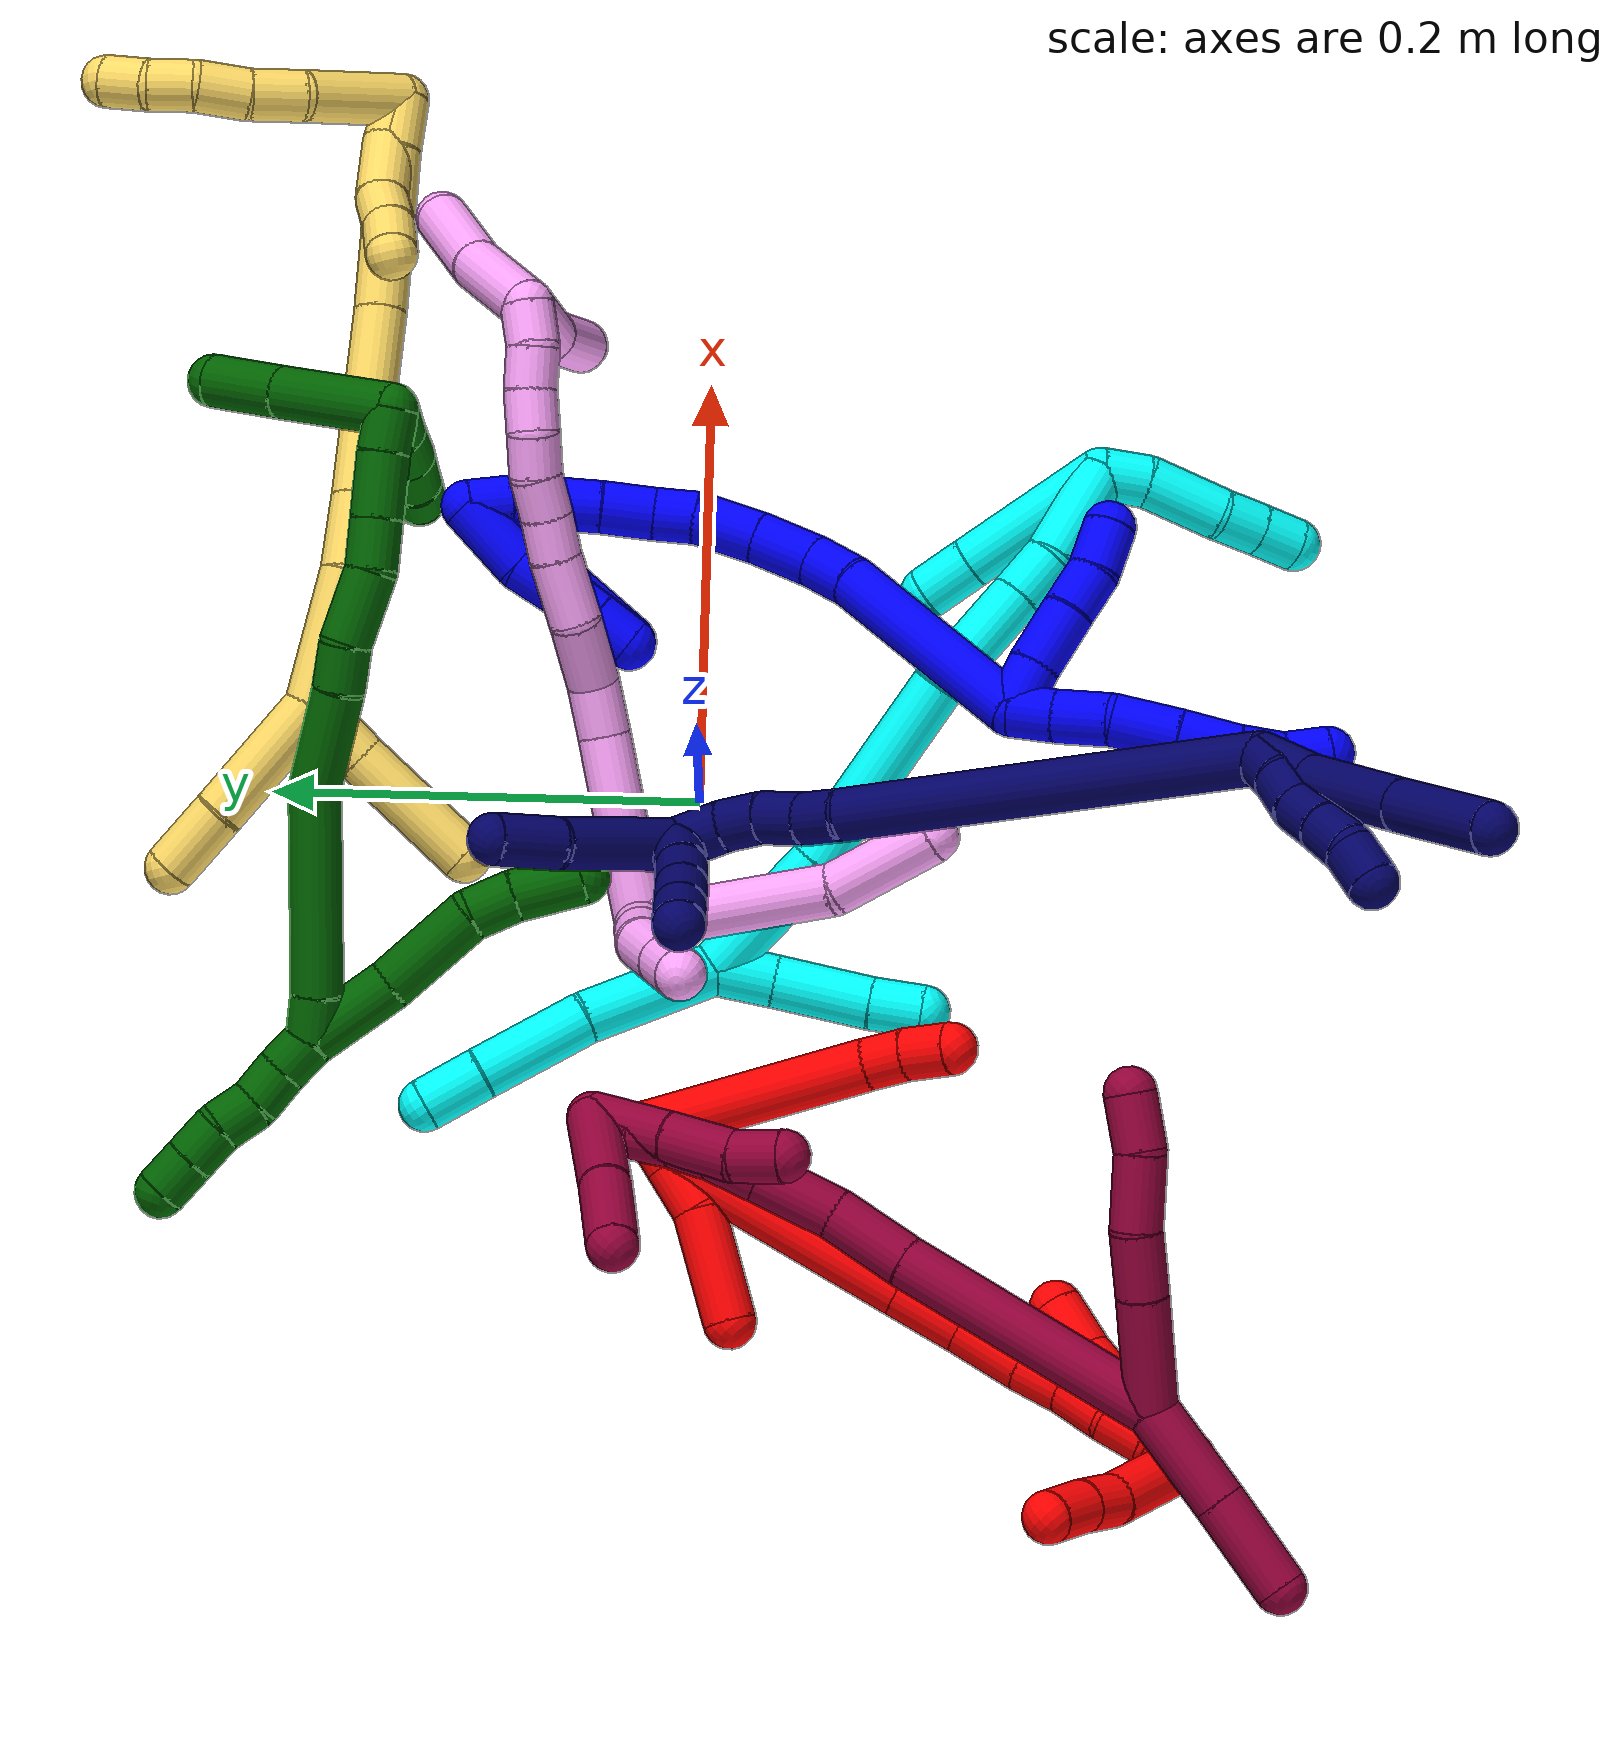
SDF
<sdf version="1.7">
 <world name="default">
  <plugin name="TubeGeneratorPlugin" filename="libtube_generator_plugin.so"/>
  <model name="photoneo_s_sensor">
   <static>1</static>
   <pose>0 0 2 1.57079 1.57079 3.14159</pose>
   <link name="link">
    <inertial><mass>0.1</mass></inertial>
    <sensor name="sensor" type="depth">
     <update_rate>30</update_rate>
     <camera>
      <horizontal_fov>1.22</horizontal_fov>
      <image><width>1920</width><height>1200</height><format>B8G8R8</format></image>
      <clip><near>0.1</near><far>4</far></clip>
      <depth_camera><output>points</output></depth_camera>
     </camera>
     <plugin name="camera_plugin" filename="libgazebo_ros_depth_camera.so">
      <baseline>0.2</baseline>
      <alwaysOn>1</alwaysOn>
      <updateRate>0.0</updateRate>
      <cameraName>camera_ir</cameraName>
      <imageTopicName>/camera/color/image_raw</imageTopicName>
      <cameraInfoTopicName>/camera/color/camera_info</cameraInfoTopicName>
      <depthImageTopicName>/camera/depth/image_raw</depthImageTopicName>
      <depthImageCameraInfoTopicName>/camera/depth/camera_info</depthImageCameraInfoTopicName>
      <pointCloudTopicName>/camera/depth/points</pointCloudTopicName>
      <frameName>fr_optical</frameName>
      <pointCloudCutoff>0.1</pointCloudCutoff>
      <pointCloudCutoffMax>2.0</pointCloudCutoffMax>
      <distortionK1>0</distortionK1>
      <distortionK2>0</distortionK2>
      <distortionK3>0</distortionK3>
      <distortionT1>0</distortionT1>
      <distortionT2>0</distortionT2>
      <CxPrime>0</CxPrime>
      <Cx>0</Cx>
      <Cy>0</Cy>
      <focalLength>0</focalLength>
      <hackBaseline>0</hackBaseline>
     </plugin>
    </sensor>
   </link>
  </model>
  <gravity>0 0 -9.8</gravity>
  <magnetic_field>6e-06 2.3e-05 -4.2e-05</magnetic_field>
  <atmosphere type="adiabatic"/>
  <physics name="default_physics" default="0" type="ode">
   <max_step_size>0.003</max_step_size>
   <real_time_factor>1</real_time_factor>
   <real_time_update_rate>1000</real_time_update_rate>
   <max_contacts>10000</max_contacts>
   <ode>
    <solver>
     <type>quick</type>
     <iters>100</iters>
     <sor>1.3</sor>
     <use_dynamic_moi_rescaling>0</use_dynamic_moi_rescaling>
    </solver>
    <constraints>
     <contact_max_correcting_vel>0</contact_max_correcting_vel>
     <contact_surface_layer>0.001</contact_surface_layer>
     <cfm>0</cfm>
     <erp>0.2</erp>
    </constraints>
   </ode>
  </physics>
  <scene><ambient>0.4 0.4 0.4 1</ambient><background>0.7 0.7 0.7 1</background><shadows>0</shadows></scene>
  <audio><device>default</device></audio>
  <spherical_coordinates>
   <surface_model>EARTH_WGS84</surface_model>
   <latitude_deg>0</latitude_deg>
   <longitude_deg>0</longitude_deg>
   <elevation>0</elevation>
   <heading_deg>0</heading_deg>
  </spherical_coordinates>
  <model name="bin">
   <static>1</static>
   <link name="bottom">
    <collision name="collision-bottom">
     <pose>0 0 -0.01 0 -0 0</pose>
     <geometry><box><size>0.8 0.6 0.02</size></box></geometry>
     <surface>
      <friction><ode><mu>100</mu><mu2>100</mu2></ode></friction>
      <contact><collide_bitmask>65535</collide_bitmask></contact>
     </surface>
    </collision>
   </link>
   <link name="west_wall">
    <collision name="collision-west_wall">
     <pose>-0.41 0 0.1 0 -0 0</pose>
     <geometry><box><size>0.02 0.6 0.2</size></box></geometry>
     <surface>
      <friction><ode><mu>100</mu><mu2>100</mu2></ode></friction>
      <contact><collide_bitmask>65535</collide_bitmask></contact>
     </surface>
    </collision>
   </link>
   <link name="east_wall">
    <collision name="collision-east_wall">
     <pose>0.41 0 0.1 0 -0 0</pose>
     <geometry><box><size>0.02 0.6 0.2</size></box></geometry>
     <surface>
      <friction><ode><mu>100</mu><mu2>100</mu2></ode></friction>
      <contact><collide_bitmask>65535</collide_bitmask></contact>
     </surface>
    </collision>
   </link>
   <link name="south_wall">
    <collision name="collision-south_wall">
     <pose>0 -0.31 0.1 0 -0 0</pose>
     <geometry><box><size>0.8 0.02 0.2</size></box></geometry>
     <surface>
      <friction><ode><mu>100</mu><mu2>100</mu2></ode></friction>
      <contact><collide_bitmask>65535</collide_bitmask></contact>
     </surface>
    </collision>
   </link>
   <link name="north_wall">
    <collision name="collision-north_wall">
     <pose>0 0.31 0.1 0 -0 0</pose>
     <geometry><box><size>0.8 0.02 0.2</size></box></geometry>
     <surface>
      <friction><ode><mu>100</mu><mu2>100</mu2></ode></friction>
      <contact><collide_bitmask>65535</collide_bitmask></contact>
     </surface>
    </collision>
   </link>
  </model>
  <model name="1">
   <static>0</static>
   <link name="1">
    <collision name="collision-cylinder-e_1_2_8">
     <pose>-0.007271 -0.000503 -0.007869 3.07781 -0.744902 -2.97864</pose>
     <geometry><cylinder><radius>0.0125</radius><length>0.021451</length></cylinder></geometry>
     <surface>
      <friction><ode><mu>1.16</mu><mu2>1.16</mu2><slip1>0</slip1><slip2>0</slip2></ode></friction>
      <contact><ode><kp>1e+06</kp><kd>1</kd><max_vel>0</max_vel><min_depth>0.001</min_depth></ode></contact>
     </surface>
    </collision>
    <visual name="visual-cylinder-e_1_2_8">
     <pose>-0.007271 -0.000503 -0.007869 3.07781 -0.744902 -2.97864</pose>
     <geometry><cylinder><radius>0.0125</radius><length>0.021451</length></cylinder></geometry>
     <material><ambient>0 0 1 1</ambient></material>
    </visual>
    <collision name="collision-cylinder-e_2_8_9">
     <pose>-0.024378 -0.001885 -0.024733 3.04407 -0.827637 -2.92027</pose>
     <geometry><cylinder><radius>0.0125</radius><length>0.026717</length></cylinder></geometry>
     <surface>
      <friction><ode><mu>1.16</mu><mu2>1.16</mu2><slip1>0</slip1><slip2>0</slip2></ode></friction>
      <contact><ode><kp>1e+06</kp><kd>1</kd><max_vel>0</max_vel><min_depth>0.001</min_depth></ode></contact>
     </surface>
    </collision>
    <visual name="visual-cylinder-e_2_8_9">
     <pose>-0.024378 -0.001885 -0.024733 3.04407 -0.827637 -2.92027</pose>
     <geometry><cylinder><radius>0.0125</radius><length>0.026717</length></cylinder></geometry>
     <material><ambient>0 0 1 1</ambient></material>
    </visual>
    <collision name="collision-cylinder-e_3_9_10">
     <pose>-0.042766 -0.003354 -0.046992 3.09727 -0.572218 -2.99118</pose>
     <geometry><cylinder><radius>0.0125</radius><length>0.031584</length></cylinder></geometry>
     <surface>
      <friction><ode><mu>1.16</mu><mu2>1.16</mu2><slip1>0</slip1><slip2>0</slip2></ode></friction>
      <contact><ode><kp>1e+06</kp><kd>1</kd><max_vel>0</max_vel><min_depth>0.001</min_depth></ode></contact>
     </surface>
    </collision>
    <visual name="visual-cylinder-e_3_9_10">
     <pose>-0.042766 -0.003354 -0.046992 3.09727 -0.572218 -2.99118</pose>
     <geometry><cylinder><radius>0.0125</radius><length>0.031584</length></cylinder></geometry>
     <material><ambient>0 0 1 1</ambient></material>
    </visual>
    <collision name="collision-cylinder-e_4_10_11">
     <pose>-0.058305 -0.004323 -0.072168 3.1096 -0.530311 -3.02389</pose>
     <geometry><cylinder><radius>0.0125</radius><length>0.027633</length></cylinder></geometry>
     <surface>
      <friction><ode><mu>1.16</mu><mu2>1.16</mu2><slip1>0</slip1><slip2>0</slip2></ode></friction>
      <contact><ode><kp>1e+06</kp><kd>1</kd><max_vel>0</max_vel><min_depth>0.001</min_depth></ode></contact>
     </surface>
    </collision>
    <visual name="visual-cylinder-e_4_10_11">
     <pose>-0.058305 -0.004323 -0.072168 3.1096 -0.530311 -3.02389</pose>
     <geometry><cylinder><radius>0.0125</radius><length>0.027633</length></cylinder></geometry>
     <material><ambient>0 0 1 1</ambient></material>
    </visual>
    <collision name="collision-cylinder-e_5_11_12">
     <pose>-0.06967 -0.006704 -0.093605 2.93468 -0.422651 -2.2401</pose>
     <geometry><cylinder><radius>0.0125</radius><length>0.02134</length></cylinder></geometry>
     <surface>
      <friction><ode><mu>1.16</mu><mu2>1.16</mu2><slip1>0</slip1><slip2>0</slip2></ode></friction>
      <contact><ode><kp>1e+06</kp><kd>1</kd><max_vel>0</max_vel><min_depth>0.001</min_depth></ode></contact>
     </surface>
    </collision>
    <visual name="visual-cylinder-e_5_11_12">
     <pose>-0.06967 -0.006704 -0.093605 2.93468 -0.422651 -2.2401</pose>
     <geometry><cylinder><radius>0.0125</radius><length>0.02134</length></cylinder></geometry>
     <material><ambient>0 0 1 1</ambient></material>
    </visual>
    <collision name="collision-cylinder-e_6_12_6">
     <pose>-0.0787 -0.013681 -0.111296 2.59421 -0.452713 -1.37405</pose>
     <geometry><cylinder><radius>0.0125</radius><length>0.021275</length></cylinder></geometry>
     <surface>
      <friction><ode><mu>1.16</mu><mu2>1.16</mu2><slip1>0</slip1><slip2>0</slip2></ode></friction>
      <contact><ode><kp>1e+06</kp><kd>1</kd><max_vel>0</max_vel><min_depth>0.001</min_depth></ode></contact>
     </surface>
    </collision>
    <visual name="visual-cylinder-e_6_12_6">
     <pose>-0.0787 -0.013681 -0.111296 2.59421 -0.452713 -1.37405</pose>
     <geometry><cylinder><radius>0.0125</radius><length>0.021275</length></cylinder></geometry>
     <material><ambient>0 0 1 1</ambient></material>
    </visual>
    <collision name="collision-cylinder-e_1_2_13">
     <pose>-0.003477 -0.011094 -6.2e-05 1.57635 -0.303724 -0.30539</pose>
     <geometry><cylinder><radius>0.0125</radius><length>0.023252</length></cylinder></geometry>
     <surface>
      <friction><ode><mu>1.16</mu><mu2>1.16</mu2><slip1>0</slip1><slip2>0</slip2></ode></friction>
      <contact><ode><kp>1e+06</kp><kd>1</kd><max_vel>0</max_vel><min_depth>0.001</min_depth></ode></contact>
     </surface>
    </collision>
    <visual name="visual-cylinder-e_1_2_13">
     <pose>-0.003477 -0.011094 -6.2e-05 1.57635 -0.303724 -0.30539</pose>
     <geometry><cylinder><radius>0.0125</radius><length>0.023252</length></cylinder></geometry>
     <material><ambient>0 0 1 1</ambient></material>
    </visual>
    <collision name="collision-cylinder-e_2_13_14">
     <pose>-0.012643 -0.036463 -0.001259 1.65015 -0.378132 -0.408565</pose>
     <geometry><cylinder><radius>0.0125</radius><length>0.030818</length></cylinder></geometry>
     <surface>
      <friction><ode><mu>1.16</mu><mu2>1.16</mu2><slip1>0</slip1><slip2>0</slip2></ode></friction>
      <contact><ode><kp>1e+06</kp><kd>1</kd><max_vel>0</max_vel><min_depth>0.001</min_depth></ode></contact>
     </surface>
    </collision>
    <visual name="visual-cylinder-e_2_13_14">
     <pose>-0.012643 -0.036463 -0.001259 1.65015 -0.378132 -0.408565</pose>
     <geometry><cylinder><radius>0.0125</radius><length>0.030818</length></cylinder></geometry>
     <material><ambient>0 0 1 1</ambient></material>
    </visual>
    <collision name="collision-cylinder-e_3_14_15">
     <pose>-0.021823 -0.061206 -0.003649 1.69014 -0.319767 -0.359581</pose>
     <geometry><cylinder><radius>0.0125</radius><length>0.022211</length></cylinder></geometry>
     <surface>
      <friction><ode><mu>1.16</mu><mu2>1.16</mu2><slip1>0</slip1><slip2>0</slip2></ode></friction>
      <contact><ode><kp>1e+06</kp><kd>1</kd><max_vel>0</max_vel><min_depth>0.001</min_depth></ode></contact>
     </surface>
    </collision>
    <visual name="visual-cylinder-e_3_14_15">
     <pose>-0.021823 -0.061206 -0.003649 1.69014 -0.319767 -0.359581</pose>
     <geometry><cylinder><radius>0.0125</radius><length>0.022211</length></cylinder></geometry>
     <material><ambient>0 0 1 1</ambient></material>
    </visual>
    <collision name="collision-cylinder-e_4_15_5">
     <pose>-0.027327 -0.083332 -0.004085 1.50062 -0.170622 -0.159101</pose>
     <geometry><cylinder><radius>0.0125</radius><length>0.023719</length></cylinder></geometry>
     <surface>
      <friction><ode><mu>1.16</mu><mu2>1.16</mu2><slip1>0</slip1><slip2>0</slip2></ode></friction>
      <contact><ode><kp>1e+06</kp><kd>1</kd><max_vel>0</max_vel><min_depth>0.001</min_depth></ode></contact>
     </surface>
    </collision>
    <visual name="visual-cylinder-e_4_15_5">
     <pose>-0.027327 -0.083332 -0.004085 1.50062 -0.170622 -0.159101</pose>
     <geometry><cylinder><radius>0.0125</radius><length>0.023719</length></cylinder></geometry>
     <material><ambient>0 0 1 1</ambient></material>
    </visual>
    <collision name="collision-cylinder-e_1_2_16">
     <pose>0.030964 -0.026629 0.034599 0.655961 0.616882 0.215983</pose>
     <geometry><cylinder><radius>0.0125</radius><length>0.107052</length></cylinder></geometry>
     <surface>
      <friction><ode><mu>1.16</mu><mu2>1.16</mu2><slip1>0</slip1><slip2>0</slip2></ode></friction>
      <contact><ode><kp>1e+06</kp><kd>1</kd><max_vel>0</max_vel><min_depth>0.001</min_depth></ode></contact>
     </surface>
    </collision>
    <visual name="visual-cylinder-e_1_2_16">
     <pose>0.030964 -0.026629 0.034599 0.655961 0.616882 0.215983</pose>
     <geometry><cylinder><radius>0.0125</radius><length>0.107052</length></cylinder></geometry>
     <material><ambient>0 0 1 1</ambient></material>
    </visual>
    <collision name="collision-cylinder-e_2_16_17">
     <pose>0.070144 -0.057785 0.076427 0.559379 0.76665 0.230627</pose>
     <geometry><cylinder><radius>0.0125</radius><length>0.023684</length></cylinder></geometry>
     <surface>
      <friction><ode><mu>1.16</mu><mu2>1.16</mu2><slip1>0</slip1><slip2>0</slip2></ode></friction>
      <contact><ode><kp>1e+06</kp><kd>1</kd><max_vel>0</max_vel><min_depth>0.001</min_depth></ode></contact>
     </surface>
    </collision>
    <visual name="visual-cylinder-e_2_16_17">
     <pose>0.070144 -0.057785 0.076427 0.559379 0.76665 0.230627</pose>
     <geometry><cylinder><radius>0.0125</radius><length>0.023684</length></cylinder></geometry>
     <material><ambient>0 0 1 1</ambient></material>
    </visual>
    <collision name="collision-cylinder-e_3_17_18">
     <pose>0.086869 -0.065032 0.09522 0.231095 0.621616 0.07453</pose>
     <geometry><cylinder><radius>0.0125</radius><length>0.029225</length></cylinder></geometry>
     <surface>
      <friction><ode><mu>1.16</mu><mu2>1.16</mu2><slip1>0</slip1><slip2>0</slip2></ode></friction>
      <contact><ode><kp>1e+06</kp><kd>1</kd><max_vel>0</max_vel><min_depth>0.001</min_depth></ode></contact>
     </surface>
    </collision>
    <visual name="visual-cylinder-e_3_17_18">
     <pose>0.086869 -0.065032 0.09522 0.231095 0.621616 0.07453</pose>
     <geometry><cylinder><radius>0.0125</radius><length>0.029225</length></cylinder></geometry>
     <material><ambient>0 0 1 1</ambient></material>
    </visual>
    <collision name="collision-cylinder-e_4_18_19">
     <pose>0.104659 -0.069501 0.119004 0.142101 0.644614 0.047526</pose>
     <geometry><cylinder><radius>0.0125</radius><length>0.03089</length></cylinder></geometry>
     <surface>
      <friction><ode><mu>1.16</mu><mu2>1.16</mu2><slip1>0</slip1><slip2>0</slip2></ode></friction>
      <contact><ode><kp>1e+06</kp><kd>1</kd><max_vel>0</max_vel><min_depth>0.001</min_depth></ode></contact>
     </surface>
    </collision>
    <visual name="visual-cylinder-e_4_18_19">
     <pose>0.104659 -0.069501 0.119004 0.142101 0.644614 0.047526</pose>
     <geometry><cylinder><radius>0.0125</radius><length>0.03089</length></cylinder></geometry>
     <material><ambient>0 0 1 1</ambient></material>
    </visual>
    <collision name="collision-cylinder-e_5_19_20">
     <pose>0.120413 -0.069936 0.139203 -0.163183 0.67514 -0.05739</pose>
     <geometry><cylinder><radius>0.0125</radius><length>0.020714</length></cylinder></geometry>
     <surface>
      <friction><ode><mu>1.16</mu><mu2>1.16</mu2><slip1>0</slip1><slip2>0</slip2></ode></friction>
      <contact><ode><kp>1e+06</kp><kd>1</kd><max_vel>0</max_vel><min_depth>0.001</min_depth></ode></contact>
     </surface>
    </collision>
    <visual name="visual-cylinder-e_5_19_20">
     <pose>0.120413 -0.069936 0.139203 -0.163183 0.67514 -0.05739</pose>
     <geometry><cylinder><radius>0.0125</radius><length>0.020714</length></cylinder></geometry>
     <material><ambient>0 0 1 1</ambient></material>
    </visual>
    <collision name="collision-cylinder-e_6_20_21">
     <pose>0.132638 -0.065867 0.158281 -0.243281 0.465957 -0.057998</pose>
     <geometry><cylinder><radius>0.0125</radius><length>0.025605</length></cylinder></geometry>
     <surface>
      <friction><ode><mu>1.16</mu><mu2>1.16</mu2><slip1>0</slip1><slip2>0</slip2></ode></friction>
      <contact><ode><kp>1e+06</kp><kd>1</kd><max_vel>0</max_vel><min_depth>0.001</min_depth></ode></contact>
     </surface>
    </collision>
    <visual name="visual-cylinder-e_6_20_21">
     <pose>0.132638 -0.065867 0.158281 -0.243281 0.465957 -0.057998</pose>
     <geometry><cylinder><radius>0.0125</radius><length>0.025605</length></cylinder></geometry>
     <material><ambient>0 0 1 1</ambient></material>
    </visual>
    <collision name="collision-cylinder-e_7_21_22">
     <pose>0.143809 -0.060623 0.178413 -0.268886 0.524481 -0.072581</pose>
     <geometry><cylinder><radius>0.0125</radius><length>0.021645</length></cylinder></geometry>
     <surface>
      <friction><ode><mu>1.16</mu><mu2>1.16</mu2><slip1>0</slip1><slip2>0</slip2></ode></friction>
      <contact><ode><kp>1e+06</kp><kd>1</kd><max_vel>0</max_vel><min_depth>0.001</min_depth></ode></contact>
     </surface>
    </collision>
    <visual name="visual-cylinder-e_7_21_22">
     <pose>0.143809 -0.060623 0.178413 -0.268886 0.524481 -0.072581</pose>
     <geometry><cylinder><radius>0.0125</radius><length>0.021645</length></cylinder></geometry>
     <material><ambient>0 0 1 1</ambient></material>
    </visual>
    <collision name="collision-cylinder-e_8_22_23">
     <pose>0.153108 -0.054458 0.196506 -0.385424 0.377608 -0.074538</pose>
     <geometry><cylinder><radius>0.0125</radius><length>0.021039</length></cylinder></geometry>
     <surface>
      <friction><ode><mu>1.16</mu><mu2>1.16</mu2><slip1>0</slip1><slip2>0</slip2></ode></friction>
      <contact><ode><kp>1e+06</kp><kd>1</kd><max_vel>0</max_vel><min_depth>0.001</min_depth></ode></contact>
     </surface>
    </collision>
    <visual name="visual-cylinder-e_8_22_23">
     <pose>0.153108 -0.054458 0.196506 -0.385424 0.377608 -0.074538</pose>
     <geometry><cylinder><radius>0.0125</radius><length>0.021039</length></cylinder></geometry>
     <material><ambient>0 0 1 1</ambient></material>
    </visual>
    <collision name="collision-cylinder-e_9_23_1">
     <pose>0.161349 -0.046207 0.213409 -0.528093 0.447972 -0.123025</pose>
     <geometry><cylinder><radius>0.0125</radius><length>0.020146</length></cylinder></geometry>
     <surface>
      <friction><ode><mu>1.16</mu><mu2>1.16</mu2><slip1>0</slip1><slip2>0</slip2></ode></friction>
      <contact><ode><kp>1e+06</kp><kd>1</kd><max_vel>0</max_vel><min_depth>0.001</min_depth></ode></contact>
     </surface>
    </collision>
    <visual name="visual-cylinder-e_9_23_1">
     <pose>0.161349 -0.046207 0.213409 -0.528093 0.447972 -0.123025</pose>
     <geometry><cylinder><radius>0.0125</radius><length>0.020146</length></cylinder></geometry>
     <material><ambient>0 0 1 1</ambient></material>
    </visual>
    <collision name="collision-cylinder-e_1_1_24">
     <pose>0.162047 -0.033421 0.205235 -2.66783 -0.200898 0.790986</pose>
     <geometry><cylinder><radius>0.0125</radius><length>0.036737</length></cylinder></geometry>
     <surface>
      <friction><ode><mu>1.16</mu><mu2>1.16</mu2><slip1>0</slip1><slip2>0</slip2></ode></friction>
      <contact><ode><kp>1e+06</kp><kd>1</kd><max_vel>0</max_vel><min_depth>0.001</min_depth></ode></contact>
     </surface>
    </collision>
    <visual name="visual-cylinder-e_1_1_24">
     <pose>0.162047 -0.033421 0.205235 -2.66783 -0.200898 0.790986</pose>
     <geometry><cylinder><radius>0.0125</radius><length>0.036737</length></cylinder></geometry>
     <material><ambient>0 0 1 1</ambient></material>
    </visual>
    <collision name="collision-cylinder-e_2_24_25">
     <pose>0.154562 -0.022652 0.179777 -2.87713 -0.37231 1.9118</pose>
     <geometry><cylinder><radius>0.0125</radius><length>0.021001</length></cylinder></geometry>
     <surface>
      <friction><ode><mu>1.16</mu><mu2>1.16</mu2><slip1>0</slip1><slip2>0</slip2></ode></friction>
      <contact><ode><kp>1e+06</kp><kd>1</kd><max_vel>0</max_vel><min_depth>0.001</min_depth></ode></contact>
     </surface>
    </collision>
    <visual name="visual-cylinder-e_2_24_25">
     <pose>0.154562 -0.022652 0.179777 -2.87713 -0.37231 1.9118</pose>
     <geometry><cylinder><radius>0.0125</radius><length>0.021001</length></cylinder></geometry>
     <material><ambient>0 0 1 1</ambient></material>
    </visual>
    <collision name="collision-cylinder-e_3_25_26">
     <pose>0.147467 -0.016836 0.160252 -2.82894 -0.299745 1.52798</pose>
     <geometry><cylinder><radius>0.0125</radius><length>0.022184</length></cylinder></geometry>
     <surface>
      <friction><ode><mu>1.16</mu><mu2>1.16</mu2><slip1>0</slip1><slip2>0</slip2></ode></friction>
      <contact><ode><kp>1e+06</kp><kd>1</kd><max_vel>0</max_vel><min_depth>0.001</min_depth></ode></contact>
     </surface>
    </collision>
    <visual name="visual-cylinder-e_3_25_26">
     <pose>0.147467 -0.016836 0.160252 -2.82894 -0.299745 1.52798</pose>
     <geometry><cylinder><radius>0.0125</radius><length>0.022184</length></cylinder></geometry>
     <material><ambient>0 0 1 1</ambient></material>
    </visual>
    <collision name="collision-cylinder-e_4_26_4">
     <pose>0.141669 -0.0108 0.140857 -2.85181 -0.253967 1.43764</pose>
     <geometry><cylinder><radius>0.0125</radius><length>0.020078</length></cylinder></geometry>
     <surface>
      <friction><ode><mu>1.16</mu><mu2>1.16</mu2><slip1>0</slip1><slip2>0</slip2></ode></friction>
      <contact><ode><kp>1e+06</kp><kd>1</kd><max_vel>0</max_vel><min_depth>0.001</min_depth></ode></contact>
     </surface>
    </collision>
    <visual name="visual-cylinder-e_4_26_4">
     <pose>0.141669 -0.0108 0.140857 -2.85181 -0.253967 1.43764</pose>
     <geometry><cylinder><radius>0.0125</radius><length>0.020078</length></cylinder></geometry>
     <material><ambient>0 0 1 1</ambient></material>
    </visual>
    <collision name="collision-cylinder-e_1_1_27">
     <pose>0.163251 -0.03728 0.199808 -2.94134 -0.111992 1.01786</pose>
     <geometry><cylinder><radius>0.0125</radius><length>0.044037</length></cylinder></geometry>
     <surface>
      <friction><ode><mu>1.16</mu><mu2>1.16</mu2><slip1>0</slip1><slip2>0</slip2></ode></friction>
      <contact><ode><kp>1e+06</kp><kd>1</kd><max_vel>0</max_vel><min_depth>0.001</min_depth></ode></contact>
     </surface>
    </collision>
    <visual name="visual-cylinder-e_1_1_27">
     <pose>0.163251 -0.03728 0.199808 -2.94134 -0.111992 1.01786</pose>
     <geometry><cylinder><radius>0.0125</radius><length>0.044037</length></cylinder></geometry>
     <material><ambient>0 0 1 1</ambient></material>
    </visual>
    <collision name="collision-cylinder-e_2_27_3">
     <pose>0.159393 -0.026956 0.151063 -2.92627 -0.049958 0.454347</pose>
     <geometry><cylinder><radius>0.0125</radius><length>0.055963</length></cylinder></geometry>
     <surface>
      <friction><ode><mu>1.16</mu><mu2>1.16</mu2><slip1>0</slip1><slip2>0</slip2></ode></friction>
      <contact><ode><kp>1e+06</kp><kd>1</kd><max_vel>0</max_vel><min_depth>0.001</min_depth></ode></contact>
     </surface>
    </collision>
    <visual name="visual-cylinder-e_2_27_3">
     <pose>0.159393 -0.026956 0.151063 -2.92627 -0.049958 0.454347</pose>
     <geometry><cylinder><radius>0.0125</radius><length>0.055963</length></cylinder></geometry>
     <material><ambient>0 0 1 1</ambient></material>
    </visual>
    <collision name="collision-sphere-3">
     <pose>0.157996 -0.020985 0.123762 0 -0 0</pose>
     <geometry><sphere><radius>0.0125</radius></sphere></geometry>
     <surface>
      <friction><ode><mu>1.16</mu><mu2>1.16</mu2><slip1>0</slip1><slip2>0</slip2></ode></friction>
      <contact><ode><kp>1e+06</kp><kd>1</kd><max_vel>0</max_vel><min_depth>0.001</min_depth></ode></contact>
     </surface>
    </collision>
    <visual name="visual-sphere-3">
     <pose>0.157996 -0.020985 0.123762 0 -0 0</pose>
     <geometry><sphere><radius>0.0125</radius></sphere></geometry>
     <material><ambient>0 0 1 1</ambient></material>
    </visual>
    <collision name="collision-sphere-27">
     <pose>0.160791 -0.032927 0.178364 0 -0 0</pose>
     <geometry><sphere><radius>0.0125</radius></sphere></geometry>
     <surface>
      <friction><ode><mu>1.16</mu><mu2>1.16</mu2><slip1>0</slip1><slip2>0</slip2></ode></friction>
      <contact><ode><kp>1e+06</kp><kd>1</kd><max_vel>0</max_vel><min_depth>0.001</min_depth></ode></contact>
     </surface>
    </collision>
    <visual name="visual-sphere-27">
     <pose>0.160791 -0.032927 0.178364 0 -0 0</pose>
     <geometry><sphere><radius>0.0125</radius></sphere></geometry>
     <material><ambient>0 0 1 1</ambient></material>
    </visual>
    <collision name="collision-sphere-4">
     <pose>0.139147 -0.008023 0.131545 0 -0 0</pose>
     <geometry><sphere><radius>0.0125</radius></sphere></geometry>
     <surface>
      <friction><ode><mu>1.16</mu><mu2>1.16</mu2><slip1>0</slip1><slip2>0</slip2></ode></friction>
      <contact><ode><kp>1e+06</kp><kd>1</kd><max_vel>0</max_vel><min_depth>0.001</min_depth></ode></contact>
     </surface>
    </collision>
    <visual name="visual-sphere-4">
     <pose>0.139147 -0.008023 0.131545 0 -0 0</pose>
     <geometry><sphere><radius>0.0125</radius></sphere></geometry>
     <material><ambient>0 0 1 1</ambient></material>
    </visual>
    <collision name="collision-sphere-26">
     <pose>0.144191 -0.013576 0.150168 0 -0 0</pose>
     <geometry><sphere><radius>0.0125</radius></sphere></geometry>
     <surface>
      <friction><ode><mu>1.16</mu><mu2>1.16</mu2><slip1>0</slip1><slip2>0</slip2></ode></friction>
      <contact><ode><kp>1e+06</kp><kd>1</kd><max_vel>0</max_vel><min_depth>0.001</min_depth></ode></contact>
     </surface>
    </collision>
    <visual name="visual-sphere-26">
     <pose>0.144191 -0.013576 0.150168 0 -0 0</pose>
     <geometry><sphere><radius>0.0125</radius></sphere></geometry>
     <material><ambient>0 0 1 1</ambient></material>
    </visual>
    <collision name="collision-sphere-25">
     <pose>0.150742 -0.020095 0.170336 0 -0 0</pose>
     <geometry><sphere><radius>0.0125</radius></sphere></geometry>
     <surface>
      <friction><ode><mu>1.16</mu><mu2>1.16</mu2><slip1>0</slip1><slip2>0</slip2></ode></friction>
      <contact><ode><kp>1e+06</kp><kd>1</kd><max_vel>0</max_vel><min_depth>0.001</min_depth></ode></contact>
     </surface>
    </collision>
    <visual name="visual-sphere-25">
     <pose>0.150742 -0.020095 0.170336 0 -0 0</pose>
     <geometry><sphere><radius>0.0125</radius></sphere></geometry>
     <material><ambient>0 0 1 1</ambient></material>
    </visual>
    <collision name="collision-sphere-24">
     <pose>0.158381 -0.025209 0.189218 0 -0 0</pose>
     <geometry><sphere><radius>0.0125</radius></sphere></geometry>
     <surface>
      <friction><ode><mu>1.16</mu><mu2>1.16</mu2><slip1>0</slip1><slip2>0</slip2></ode></friction>
      <contact><ode><kp>1e+06</kp><kd>1</kd><max_vel>0</max_vel><min_depth>0.001</min_depth></ode></contact>
     </surface>
    </collision>
    <visual name="visual-sphere-24">
     <pose>0.158381 -0.025209 0.189218 0 -0 0</pose>
     <geometry><sphere><radius>0.0125</radius></sphere></geometry>
     <material><ambient>0 0 1 1</ambient></material>
    </visual>
    <collision name="collision-sphere-1">
     <pose>0.165712 -0.041632 0.221251 0 -0 0</pose>
     <geometry><sphere><radius>0.0125</radius></sphere></geometry>
     <surface>
      <friction><ode><mu>1.16</mu><mu2>1.16</mu2><slip1>0</slip1><slip2>0</slip2></ode></friction>
      <contact><ode><kp>1e+06</kp><kd>1</kd><max_vel>0</max_vel><min_depth>0.001</min_depth></ode></contact>
     </surface>
    </collision>
    <visual name="visual-sphere-1">
     <pose>0.165712 -0.041632 0.221251 0 -0 0</pose>
     <geometry><sphere><radius>0.0125</radius></sphere></geometry>
     <material><ambient>0 0 1 1</ambient></material>
    </visual>
    <collision name="collision-sphere-23">
     <pose>0.156986 -0.050782 0.205567 0 -0 0</pose>
     <geometry><sphere><radius>0.0125</radius></sphere></geometry>
     <surface>
      <friction><ode><mu>1.16</mu><mu2>1.16</mu2><slip1>0</slip1><slip2>0</slip2></ode></friction>
      <contact><ode><kp>1e+06</kp><kd>1</kd><max_vel>0</max_vel><min_depth>0.001</min_depth></ode></contact>
     </surface>
    </collision>
    <visual name="visual-sphere-23">
     <pose>0.156986 -0.050782 0.205567 0 -0 0</pose>
     <geometry><sphere><radius>0.0125</radius></sphere></geometry>
     <material><ambient>0 0 1 1</ambient></material>
    </visual>
    <collision name="collision-sphere-22">
     <pose>0.149229 -0.058135 0.187445 0 -0 0</pose>
     <geometry><sphere><radius>0.0125</radius></sphere></geometry>
     <surface>
      <friction><ode><mu>1.16</mu><mu2>1.16</mu2><slip1>0</slip1><slip2>0</slip2></ode></friction>
      <contact><ode><kp>1e+06</kp><kd>1</kd><max_vel>0</max_vel><min_depth>0.001</min_depth></ode></contact>
     </surface>
    </collision>
    <visual name="visual-sphere-22">
     <pose>0.149229 -0.058135 0.187445 0 -0 0</pose>
     <geometry><sphere><radius>0.0125</radius></sphere></geometry>
     <material><ambient>0 0 1 1</ambient></material>
    </visual>
    <collision name="collision-sphere-21">
     <pose>0.13839 -0.063112 0.169382 0 -0 0</pose>
     <geometry><sphere><radius>0.0125</radius></sphere></geometry>
     <surface>
      <friction><ode><mu>1.16</mu><mu2>1.16</mu2><slip1>0</slip1><slip2>0</slip2></ode></friction>
      <contact><ode><kp>1e+06</kp><kd>1</kd><max_vel>0</max_vel><min_depth>0.001</min_depth></ode></contact>
     </surface>
    </collision>
    <visual name="visual-sphere-21">
     <pose>0.13839 -0.063112 0.169382 0 -0 0</pose>
     <geometry><sphere><radius>0.0125</radius></sphere></geometry>
     <material><ambient>0 0 1 1</ambient></material>
    </visual>
    <collision name="collision-sphere-12">
     <pose>-0.074047 -0.008703 -0.103128 0 -0 0</pose>
     <geometry><sphere><radius>0.0125</radius></sphere></geometry>
     <surface>
      <friction><ode><mu>1.16</mu><mu2>1.16</mu2><slip1>0</slip1><slip2>0</slip2></ode></friction>
      <contact><ode><kp>1e+06</kp><kd>1</kd><max_vel>0</max_vel><min_depth>0.001</min_depth></ode></contact>
     </surface>
    </collision>
    <visual name="visual-sphere-12">
     <pose>-0.074047 -0.008703 -0.103128 0 -0 0</pose>
     <geometry><sphere><radius>0.0125</radius></sphere></geometry>
     <material><ambient>0 0 1 1</ambient></material>
    </visual>
    <collision name="collision-sphere-11">
     <pose>-0.065294 -0.004704 -0.084081 0 -0 0</pose>
     <geometry><sphere><radius>0.0125</radius></sphere></geometry>
     <surface>
      <friction><ode><mu>1.16</mu><mu2>1.16</mu2><slip1>0</slip1><slip2>0</slip2></ode></friction>
      <contact><ode><kp>1e+06</kp><kd>1</kd><max_vel>0</max_vel><min_depth>0.001</min_depth></ode></contact>
     </surface>
    </collision>
    <visual name="visual-sphere-11">
     <pose>-0.065294 -0.004704 -0.084081 0 -0 0</pose>
     <geometry><sphere><radius>0.0125</radius></sphere></geometry>
     <material><ambient>0 0 1 1</ambient></material>
    </visual>
    <collision name="collision-sphere-10">
     <pose>-0.051317 -0.003942 -0.060256 0 -0 0</pose>
     <geometry><sphere><radius>0.0125</radius></sphere></geometry>
     <surface>
      <friction><ode><mu>1.16</mu><mu2>1.16</mu2><slip1>0</slip1><slip2>0</slip2></ode></friction>
      <contact><ode><kp>1e+06</kp><kd>1</kd><max_vel>0</max_vel><min_depth>0.001</min_depth></ode></contact>
     </surface>
    </collision>
    <visual name="visual-sphere-10">
     <pose>-0.051317 -0.003942 -0.060256 0 -0 0</pose>
     <geometry><sphere><radius>0.0125</radius></sphere></geometry>
     <material><ambient>0 0 1 1</ambient></material>
    </visual>
    <collision name="collision-sphere-9">
     <pose>-0.034214 -0.002765 -0.033729 0 -0 0</pose>
     <geometry><sphere><radius>0.0125</radius></sphere></geometry>
     <surface>
      <friction><ode><mu>1.16</mu><mu2>1.16</mu2><slip1>0</slip1><slip2>0</slip2></ode></friction>
      <contact><ode><kp>1e+06</kp><kd>1</kd><max_vel>0</max_vel><min_depth>0.001</min_depth></ode></contact>
     </surface>
    </collision>
    <visual name="visual-sphere-9">
     <pose>-0.034214 -0.002765 -0.033729 0 -0 0</pose>
     <geometry><sphere><radius>0.0125</radius></sphere></geometry>
     <material><ambient>0 0 1 1</ambient></material>
    </visual>
    <collision name="collision-sphere-2">
     <geometry><sphere><radius>0.0125</radius></sphere></geometry>
     <surface>
      <friction><ode><mu>1.16</mu><mu2>1.16</mu2><slip1>0</slip1><slip2>0</slip2></ode></friction>
      <contact><ode><kp>1e+06</kp><kd>1</kd><max_vel>0</max_vel><min_depth>0.001</min_depth></ode></contact>
     </surface>
    </collision>
    <visual name="visual-sphere-2">
     <geometry><sphere><radius>0.0125</radius></sphere></geometry>
     <material><ambient>0 0 1 1</ambient></material>
    </visual>
    <collision name="collision-sphere-19">
     <pose>0.11394 -0.071249 0.131225 0 -0 0</pose>
     <geometry><sphere><radius>0.0125</radius></sphere></geometry>
     <surface>
      <friction><ode><mu>1.16</mu><mu2>1.16</mu2><slip1>0</slip1><slip2>0</slip2></ode></friction>
      <contact><ode><kp>1e+06</kp><kd>1</kd><max_vel>0</max_vel><min_depth>0.001</min_depth></ode></contact>
     </surface>
    </collision>
    <visual name="visual-sphere-19">
     <pose>0.11394 -0.071249 0.131225 0 -0 0</pose>
     <geometry><sphere><radius>0.0125</radius></sphere></geometry>
     <material><ambient>0 0 1 1</ambient></material>
    </visual>
    <collision name="collision-sphere-8">
     <pose>-0.014541 -0.001005 -0.015737 0 -0 0</pose>
     <geometry><sphere><radius>0.0125</radius></sphere></geometry>
     <surface>
      <friction><ode><mu>1.16</mu><mu2>1.16</mu2><slip1>0</slip1><slip2>0</slip2></ode></friction>
      <contact><ode><kp>1e+06</kp><kd>1</kd><max_vel>0</max_vel><min_depth>0.001</min_depth></ode></contact>
     </surface>
    </collision>
    <visual name="visual-sphere-8">
     <pose>-0.014541 -0.001005 -0.015737 0 -0 0</pose>
     <geometry><sphere><radius>0.0125</radius></sphere></geometry>
     <material><ambient>0 0 1 1</ambient></material>
    </visual>
    <collision name="collision-sphere-6">
     <pose>-0.083353 -0.01866 -0.119465 0 -0 0</pose>
     <geometry><sphere><radius>0.0125</radius></sphere></geometry>
     <surface>
      <friction><ode><mu>1.16</mu><mu2>1.16</mu2><slip1>0</slip1><slip2>0</slip2></ode></friction>
      <contact><ode><kp>1e+06</kp><kd>1</kd><max_vel>0</max_vel><min_depth>0.001</min_depth></ode></contact>
     </surface>
    </collision>
    <visual name="visual-sphere-6">
     <pose>-0.083353 -0.01866 -0.119465 0 -0 0</pose>
     <geometry><sphere><radius>0.0125</radius></sphere></geometry>
     <material><ambient>0 0 1 1</ambient></material>
    </visual>
    <collision name="collision-sphere-13">
     <pose>-0.006954 -0.022188 -0.000123 0 -0 0</pose>
     <geometry><sphere><radius>0.0125</radius></sphere></geometry>
     <surface>
      <friction><ode><mu>1.16</mu><mu2>1.16</mu2><slip1>0</slip1><slip2>0</slip2></ode></friction>
      <contact><ode><kp>1e+06</kp><kd>1</kd><max_vel>0</max_vel><min_depth>0.001</min_depth></ode></contact>
     </surface>
    </collision>
    <visual name="visual-sphere-13">
     <pose>-0.006954 -0.022188 -0.000123 0 -0 0</pose>
     <geometry><sphere><radius>0.0125</radius></sphere></geometry>
     <material><ambient>0 0 1 1</ambient></material>
    </visual>
    <collision name="collision-sphere-14">
     <pose>-0.018332 -0.050739 -0.002394 0 -0 0</pose>
     <geometry><sphere><radius>0.0125</radius></sphere></geometry>
     <surface>
      <friction><ode><mu>1.16</mu><mu2>1.16</mu2><slip1>0</slip1><slip2>0</slip2></ode></friction>
      <contact><ode><kp>1e+06</kp><kd>1</kd><max_vel>0</max_vel><min_depth>0.001</min_depth></ode></contact>
     </surface>
    </collision>
    <visual name="visual-sphere-14">
     <pose>-0.018332 -0.050739 -0.002394 0 -0 0</pose>
     <geometry><sphere><radius>0.0125</radius></sphere></geometry>
     <material><ambient>0 0 1 1</ambient></material>
    </visual>
    <collision name="collision-sphere-15">
     <pose>-0.025314 -0.071674 -0.004904 0 -0 0</pose>
     <geometry><sphere><radius>0.0125</radius></sphere></geometry>
     <surface>
      <friction><ode><mu>1.16</mu><mu2>1.16</mu2><slip1>0</slip1><slip2>0</slip2></ode></friction>
      <contact><ode><kp>1e+06</kp><kd>1</kd><max_vel>0</max_vel><min_depth>0.001</min_depth></ode></contact>
     </surface>
    </collision>
    <visual name="visual-sphere-15">
     <pose>-0.025314 -0.071674 -0.004904 0 -0 0</pose>
     <geometry><sphere><radius>0.0125</radius></sphere></geometry>
     <material><ambient>0 0 1 1</ambient></material>
    </visual>
    <collision name="collision-sphere-5">
     <pose>-0.029341 -0.09499 -0.003265 0 -0 0</pose>
     <geometry><sphere><radius>0.0125</radius></sphere></geometry>
     <surface>
      <friction><ode><mu>1.16</mu><mu2>1.16</mu2><slip1>0</slip1><slip2>0</slip2></ode></friction>
      <contact><ode><kp>1e+06</kp><kd>1</kd><max_vel>0</max_vel><min_depth>0.001</min_depth></ode></contact>
     </surface>
    </collision>
    <visual name="visual-sphere-5">
     <pose>-0.029341 -0.09499 -0.003265 0 -0 0</pose>
     <geometry><sphere><radius>0.0125</radius></sphere></geometry>
     <material><ambient>0 0 1 1</ambient></material>
    </visual>
    <collision name="collision-sphere-16">
     <pose>0.061929 -0.053259 0.069198 0 -0 0</pose>
     <geometry><sphere><radius>0.0125</radius></sphere></geometry>
     <surface>
      <friction><ode><mu>1.16</mu><mu2>1.16</mu2><slip1>0</slip1><slip2>0</slip2></ode></friction>
      <contact><ode><kp>1e+06</kp><kd>1</kd><max_vel>0</max_vel><min_depth>0.001</min_depth></ode></contact>
     </surface>
    </collision>
    <visual name="visual-sphere-16">
     <pose>0.061929 -0.053259 0.069198 0 -0 0</pose>
     <geometry><sphere><radius>0.0125</radius></sphere></geometry>
     <material><ambient>0 0 1 1</ambient></material>
    </visual>
    <collision name="collision-sphere-17">
     <pose>0.078359 -0.062311 0.083657 0 -0 0</pose>
     <geometry><sphere><radius>0.0125</radius></sphere></geometry>
     <surface>
      <friction><ode><mu>1.16</mu><mu2>1.16</mu2><slip1>0</slip1><slip2>0</slip2></ode></friction>
      <contact><ode><kp>1e+06</kp><kd>1</kd><max_vel>0</max_vel><min_depth>0.001</min_depth></ode></contact>
     </surface>
    </collision>
    <visual name="visual-sphere-17">
     <pose>0.078359 -0.062311 0.083657 0 -0 0</pose>
     <geometry><sphere><radius>0.0125</radius></sphere></geometry>
     <material><ambient>0 0 1 1</ambient></material>
    </visual>
    <collision name="collision-sphere-18">
     <pose>0.095378 -0.067752 0.106783 0 -0 0</pose>
     <geometry><sphere><radius>0.0125</radius></sphere></geometry>
     <surface>
      <friction><ode><mu>1.16</mu><mu2>1.16</mu2><slip1>0</slip1><slip2>0</slip2></ode></friction>
      <contact><ode><kp>1e+06</kp><kd>1</kd><max_vel>0</max_vel><min_depth>0.001</min_depth></ode></contact>
     </surface>
    </collision>
    <visual name="visual-sphere-18">
     <pose>0.095378 -0.067752 0.106783 0 -0 0</pose>
     <geometry><sphere><radius>0.0125</radius></sphere></geometry>
     <material><ambient>0 0 1 1</ambient></material>
    </visual>
    <collision name="collision-sphere-20">
     <pose>0.126886 -0.068622 0.147181 0 -0 0</pose>
     <geometry><sphere><radius>0.0125</radius></sphere></geometry>
     <surface>
      <friction><ode><mu>1.16</mu><mu2>1.16</mu2><slip1>0</slip1><slip2>0</slip2></ode></friction>
      <contact><ode><kp>1e+06</kp><kd>1</kd><max_vel>0</max_vel><min_depth>0.001</min_depth></ode></contact>
     </surface>
    </collision>
    <visual name="visual-sphere-20">
     <pose>0.126886 -0.068622 0.147181 0 -0 0</pose>
     <geometry><sphere><radius>0.0125</radius></sphere></geometry>
     <material><ambient>0 0 1 1</ambient></material>
    </visual>
    <inertial>
     <pose>0.065484 -0.034231 0.076352 0 -0 0</pose>
     <mass>0.75</mass>
     <inertia><ixx>0.000158</ixx><ixy>0</ixy><ixz>0</ixz><iyy>0.000126</iyy><iyz>0</iyz><izz>-9e-06</izz></inertia>
    </inertial>
   </link>
   <pose>0.030038 -0.143133 0.096078 0.661355 0.980876 1.85896</pose>
  </model>
  <model name="2">
   <static>0</static>
   <link name="2">
    <collision name="collision-cylinder-e_1_2_8">
     <pose>-0.044066 -0.01993 0.023816 0.696808 -0.956901 -0.372399</pose>
     <geometry><cylinder><radius>0.0125</radius><length>0.107818</length></cylinder></geometry>
     <surface>
      <friction><ode><mu>1.16</mu><mu2>1.16</mu2><slip1>0</slip1><slip2>0</slip2></ode></friction>
      <contact><ode><kp>1e+06</kp><kd>1</kd><max_vel>0</max_vel><min_depth>0.001</min_depth></ode></contact>
     </surface>
    </collision>
    <visual name="visual-cylinder-e_1_2_8">
     <pose>-0.044066 -0.01993 0.023816 0.696808 -0.956901 -0.372399</pose>
     <geometry><cylinder><radius>0.0125</radius><length>0.107818</length></cylinder></geometry>
     <material><ambient>1 0 0 1</ambient></material>
    </visual>
    <collision name="collision-cylinder-e_2_8_9">
     <pose>-0.095126 -0.0452 0.052381 0.8438 -0.774656 -0.362194</pose>
     <geometry><cylinder><radius>0.0125</radius><length>0.02</length></cylinder></geometry>
     <surface>
      <friction><ode><mu>1.16</mu><mu2>1.16</mu2><slip1>0</slip1><slip2>0</slip2></ode></friction>
      <contact><ode><kp>1e+06</kp><kd>1</kd><max_vel>0</max_vel><min_depth>0.001</min_depth></ode></contact>
     </surface>
    </collision>
    <visual name="visual-cylinder-e_2_8_9">
     <pose>-0.095126 -0.0452 0.052381 0.8438 -0.774656 -0.362194</pose>
     <geometry><cylinder><radius>0.0125</radius><length>0.02</length></cylinder></geometry>
     <material><ambient>1 0 0 1</ambient></material>
    </visual>
    <collision name="collision-cylinder-e_3_9_6">
     <pose>-0.108833 -0.056737 0.06342 0.778076 -0.650006 -0.274516</pose>
     <geometry><cylinder><radius>0.0125</radius><length>0.022182</length></cylinder></geometry>
     <surface>
      <friction><ode><mu>1.16</mu><mu2>1.16</mu2><slip1>0</slip1><slip2>0</slip2></ode></friction>
      <contact><ode><kp>1e+06</kp><kd>1</kd><max_vel>0</max_vel><min_depth>0.001</min_depth></ode></contact>
     </surface>
    </collision>
    <visual name="visual-cylinder-e_3_9_6">
     <pose>-0.108833 -0.056737 0.06342 0.778076 -0.650006 -0.274516</pose>
     <geometry><cylinder><radius>0.0125</radius><length>0.022182</length></cylinder></geometry>
     <material><ambient>1 0 0 1</ambient></material>
    </visual>
    <collision name="collision-cylinder-e_1_2_10">
     <pose>0.001372 0.001295 0.010279 -0.125374 0.131711 -0.008279</pose>
     <geometry><cylinder><radius>0.0125</radius><length>0.020901</length></cylinder></geometry>
     <surface>
      <friction><ode><mu>1.16</mu><mu2>1.16</mu2><slip1>0</slip1><slip2>0</slip2></ode></friction>
      <contact><ode><kp>1e+06</kp><kd>1</kd><max_vel>0</max_vel><min_depth>0.001</min_depth></ode></contact>
     </surface>
    </collision>
    <visual name="visual-cylinder-e_1_2_10">
     <pose>0.001372 0.001295 0.010279 -0.125374 0.131711 -0.008279</pose>
     <geometry><cylinder><radius>0.0125</radius><length>0.020901</length></cylinder></geometry>
     <material><ambient>1 0 0 1</ambient></material>
    </visual>
    <collision name="collision-cylinder-e_2_10_11">
     <pose>0.004815 0.002696 0.032764 -0.0086 0.167995 -0.000724</pose>
     <geometry><cylinder><radius>0.0125</radius><length>0.024764</length></cylinder></geometry>
     <surface>
      <friction><ode><mu>1.16</mu><mu2>1.16</mu2><slip1>0</slip1><slip2>0</slip2></ode></friction>
      <contact><ode><kp>1e+06</kp><kd>1</kd><max_vel>0</max_vel><min_depth>0.001</min_depth></ode></contact>
     </surface>
    </collision>
    <visual name="visual-cylinder-e_2_10_11">
     <pose>0.004815 0.002696 0.032764 -0.0086 0.167995 -0.000724</pose>
     <geometry><cylinder><radius>0.0125</radius><length>0.024764</length></cylinder></geometry>
     <material><ambient>1 0 0 1</ambient></material>
    </visual>
    <collision name="collision-cylinder-e_3_11_5">
     <pose>0.017781 0.007124 0.06948 -0.174596 0.412663 -0.036634</pose>
     <geometry><cylinder><radius>0.0125</radius><length>0.054335</length></cylinder></geometry>
     <surface>
      <friction><ode><mu>1.16</mu><mu2>1.16</mu2><slip1>0</slip1><slip2>0</slip2></ode></friction>
      <contact><ode><kp>1e+06</kp><kd>1</kd><max_vel>0</max_vel><min_depth>0.001</min_depth></ode></contact>
     </surface>
    </collision>
    <visual name="visual-cylinder-e_3_11_5">
     <pose>0.017781 0.007124 0.06948 -0.174596 0.412663 -0.036634</pose>
     <geometry><cylinder><radius>0.0125</radius><length>0.054335</length></cylinder></geometry>
     <material><ambient>1 0 0 1</ambient></material>
    </visual>
    <collision name="collision-cylinder-e_1_2_12">
     <pose>-0.00025 -0.000142 0.011388 0.01249 -0.021928 -0.000137</pose>
     <geometry><cylinder><radius>0.0125</radius><length>0.022784</length></cylinder></geometry>
     <surface>
      <friction><ode><mu>1.16</mu><mu2>1.16</mu2><slip1>0</slip1><slip2>0</slip2></ode></friction>
      <contact><ode><kp>1e+06</kp><kd>1</kd><max_vel>0</max_vel><min_depth>0.001</min_depth></ode></contact>
     </surface>
    </collision>
    <visual name="visual-cylinder-e_1_2_12">
     <pose>-0.00025 -0.000142 0.011388 0.01249 -0.021928 -0.000137</pose>
     <geometry><cylinder><radius>0.0125</radius><length>0.022784</length></cylinder></geometry>
     <material><ambient>1 0 0 1</ambient></material>
    </visual>
    <collision name="collision-cylinder-e_2_12_13">
     <pose>-0.018934 -0.003849 0.07879 0.063547 -0.317337 -0.010172</pose>
     <geometry><cylinder><radius>0.0125</radius><length>0.118152</length></cylinder></geometry>
     <surface>
      <friction><ode><mu>1.16</mu><mu2>1.16</mu2><slip1>0</slip1><slip2>0</slip2></ode></friction>
      <contact><ode><kp>1e+06</kp><kd>1</kd><max_vel>0</max_vel><min_depth>0.001</min_depth></ode></contact>
     </surface>
    </collision>
    <visual name="visual-cylinder-e_2_12_13">
     <pose>-0.018934 -0.003849 0.07879 0.063547 -0.317337 -0.010172</pose>
     <geometry><cylinder><radius>0.0125</radius><length>0.118152</length></cylinder></geometry>
     <material><ambient>1 0 0 1</ambient></material>
    </visual>
    <collision name="collision-cylinder-e_3_13_14">
     <pose>-0.042689 -0.008459 0.150837 0.065127 -0.319794 -0.010507</pose>
     <geometry><cylinder><radius>0.0125</radius><length>0.033853</length></cylinder></geometry>
     <surface>
      <friction><ode><mu>1.16</mu><mu2>1.16</mu2><slip1>0</slip1><slip2>0</slip2></ode></friction>
      <contact><ode><kp>1e+06</kp><kd>1</kd><max_vel>0</max_vel><min_depth>0.001</min_depth></ode></contact>
     </surface>
    </collision>
    <visual name="visual-cylinder-e_3_13_14">
     <pose>-0.042689 -0.008459 0.150837 0.065127 -0.319794 -0.010507</pose>
     <geometry><cylinder><radius>0.0125</radius><length>0.033853</length></cylinder></geometry>
     <material><ambient>1 0 0 1</ambient></material>
    </visual>
    <collision name="collision-cylinder-e_4_14_15">
     <pose>-0.052159 -0.012456 0.183019 0.180764 -0.247564 -0.022551</pose>
     <geometry><cylinder><radius>0.0125</radius><length>0.033863</length></cylinder></geometry>
     <surface>
      <friction><ode><mu>1.16</mu><mu2>1.16</mu2><slip1>0</slip1><slip2>0</slip2></ode></friction>
      <contact><ode><kp>1e+06</kp><kd>1</kd><max_vel>0</max_vel><min_depth>0.001</min_depth></ode></contact>
     </surface>
    </collision>
    <visual name="visual-cylinder-e_4_14_15">
     <pose>-0.052159 -0.012456 0.183019 0.180764 -0.247564 -0.022551</pose>
     <geometry><cylinder><radius>0.0125</radius><length>0.033863</length></cylinder></geometry>
     <material><ambient>1 0 0 1</ambient></material>
    </visual>
    <collision name="collision-cylinder-e_5_15_16">
     <pose>-0.059516 -0.018493 0.210066 0.275929 -0.275995 -0.038561</pose>
     <geometry><cylinder><radius>0.0125</radius><length>0.023546</length></cylinder></geometry>
     <surface>
      <friction><ode><mu>1.16</mu><mu2>1.16</mu2><slip1>0</slip1><slip2>0</slip2></ode></friction>
      <contact><ode><kp>1e+06</kp><kd>1</kd><max_vel>0</max_vel><min_depth>0.001</min_depth></ode></contact>
     </surface>
    </collision>
    <visual name="visual-cylinder-e_5_15_16">
     <pose>-0.059516 -0.018493 0.210066 0.275929 -0.275995 -0.038561</pose>
     <geometry><cylinder><radius>0.0125</radius><length>0.023546</length></cylinder></geometry>
     <material><ambient>1 0 0 1</ambient></material>
    </visual>
    <collision name="collision-cylinder-e_6_16_17">
     <pose>-0.064328 -0.025726 0.232201 0.35358 -0.133137 -0.02382</pose>
     <geometry><cylinder><radius>0.0125</radius><length>0.024169</length></cylinder></geometry>
     <surface>
      <friction><ode><mu>1.16</mu><mu2>1.16</mu2><slip1>0</slip1><slip2>0</slip2></ode></friction>
      <contact><ode><kp>1e+06</kp><kd>1</kd><max_vel>0</max_vel><min_depth>0.001</min_depth></ode></contact>
     </surface>
    </collision>
    <visual name="visual-cylinder-e_6_16_17">
     <pose>-0.064328 -0.025726 0.232201 0.35358 -0.133137 -0.02382</pose>
     <geometry><cylinder><radius>0.0125</radius><length>0.024169</length></cylinder></geometry>
     <material><ambient>1 0 0 1</ambient></material>
    </visual>
    <collision name="collision-cylinder-e_7_17_18">
     <pose>-0.068904 -0.031587 0.253486 0.168909 -0.28363 -0.024172</pose>
     <geometry><cylinder><radius>0.0125</radius><length>0.021235</length></cylinder></geometry>
     <surface>
      <friction><ode><mu>1.16</mu><mu2>1.16</mu2><slip1>0</slip1><slip2>0</slip2></ode></friction>
      <contact><ode><kp>1e+06</kp><kd>1</kd><max_vel>0</max_vel><min_depth>0.001</min_depth></ode></contact>
     </surface>
    </collision>
    <visual name="visual-cylinder-e_7_17_18">
     <pose>-0.068904 -0.031587 0.253486 0.168909 -0.28363 -0.024172</pose>
     <geometry><cylinder><radius>0.0125</radius><length>0.021235</length></cylinder></geometry>
     <material><ambient>1 0 0 1</ambient></material>
    </visual>
    <collision name="collision-cylinder-e_8_18_1">
     <pose>-0.076697 -0.032578 0.273616 -0.071572 -0.44518 0.016206</pose>
     <geometry><cylinder><radius>0.0125</radius><length>0.022399</length></cylinder></geometry>
     <surface>
      <friction><ode><mu>1.16</mu><mu2>1.16</mu2><slip1>0</slip1><slip2>0</slip2></ode></friction>
      <contact><ode><kp>1e+06</kp><kd>1</kd><max_vel>0</max_vel><min_depth>0.001</min_depth></ode></contact>
     </surface>
    </collision>
    <visual name="visual-cylinder-e_8_18_1">
     <pose>-0.076697 -0.032578 0.273616 -0.071572 -0.44518 0.016206</pose>
     <geometry><cylinder><radius>0.0125</radius><length>0.022399</length></cylinder></geometry>
     <material><ambient>1 0 0 1</ambient></material>
    </visual>
    <collision name="collision-cylinder-e_1_1_19">
     <pose>-0.082352 -0.027843 0.268068 -2.89031 -0.051494 0.402271</pose>
     <geometry><cylinder><radius>0.0125</radius><length>0.032316</length></cylinder></geometry>
     <surface>
      <friction><ode><mu>1.16</mu><mu2>1.16</mu2><slip1>0</slip1><slip2>0</slip2></ode></friction>
      <contact><ode><kp>1e+06</kp><kd>1</kd><max_vel>0</max_vel><min_depth>0.001</min_depth></ode></contact>
     </surface>
    </collision>
    <visual name="visual-cylinder-e_1_1_19">
     <pose>-0.082352 -0.027843 0.268068 -2.89031 -0.051494 0.402271</pose>
     <geometry><cylinder><radius>0.0125</radius><length>0.032316</length></cylinder></geometry>
     <material><ambient>1 0 0 1</ambient></material>
    </visual>
    <collision name="collision-cylinder-e_2_19_20">
     <pose>-0.082124 -0.021795 0.242559 -2.93836 0.104684 -0.949241</pose>
     <geometry><cylinder><radius>0.0125</radius><length>0.020284</length></cylinder></geometry>
     <surface>
      <friction><ode><mu>1.16</mu><mu2>1.16</mu2><slip1>0</slip1><slip2>0</slip2></ode></friction>
      <contact><ode><kp>1e+06</kp><kd>1</kd><max_vel>0</max_vel><min_depth>0.001</min_depth></ode></contact>
     </surface>
    </collision>
    <visual name="visual-cylinder-e_2_19_20">
     <pose>-0.082124 -0.021795 0.242559 -2.93836 0.104684 -0.949241</pose>
     <geometry><cylinder><radius>0.0125</radius><length>0.020284</length></cylinder></geometry>
     <material><ambient>1 0 0 1</ambient></material>
    </visual>
    <collision name="collision-cylinder-e_3_20_21">
     <pose>-0.082161 -0.0173 0.222932 -2.89448 -0.108677 0.825628</pose>
     <geometry><cylinder><radius>0.0125</radius><length>0.020228</length></cylinder></geometry>
     <surface>
      <friction><ode><mu>1.16</mu><mu2>1.16</mu2><slip1>0</slip1><slip2>0</slip2></ode></friction>
      <contact><ode><kp>1e+06</kp><kd>1</kd><max_vel>0</max_vel><min_depth>0.001</min_depth></ode></contact>
     </surface>
    </collision>
    <visual name="visual-cylinder-e_3_20_21">
     <pose>-0.082161 -0.0173 0.222932 -2.89448 -0.108677 0.825628</pose>
     <geometry><cylinder><radius>0.0125</radius><length>0.020228</length></cylinder></geometry>
     <material><ambient>1 0 0 1</ambient></material>
    </visual>
    <collision name="collision-cylinder-e_4_21_4">
     <pose>-0.085991 -0.012858 0.200023 -2.99205 -0.202551 1.87115</pose>
     <geometry><cylinder><radius>0.0125</radius><length>0.027172</length></cylinder></geometry>
     <surface>
      <friction><ode><mu>1.16</mu><mu2>1.16</mu2><slip1>0</slip1><slip2>0</slip2></ode></friction>
      <contact><ode><kp>1e+06</kp><kd>1</kd><max_vel>0</max_vel><min_depth>0.001</min_depth></ode></contact>
     </surface>
    </collision>
    <visual name="visual-cylinder-e_4_21_4">
     <pose>-0.085991 -0.012858 0.200023 -2.99205 -0.202551 1.87115</pose>
     <geometry><cylinder><radius>0.0125</radius><length>0.027172</length></cylinder></geometry>
     <material><ambient>1 0 0 1</ambient></material>
    </visual>
    <collision name="collision-cylinder-e_1_1_22">
     <pose>-0.057112 -0.044236 0.281192 1.77052 1.09323 1.27926</pose>
     <geometry><cylinder><radius>0.0125</radius><length>0.054966</length></cylinder></geometry>
     <surface>
      <friction><ode><mu>1.16</mu><mu2>1.16</mu2><slip1>0</slip1><slip2>0</slip2></ode></friction>
      <contact><ode><kp>1e+06</kp><kd>1</kd><max_vel>0</max_vel><min_depth>0.001</min_depth></ode></contact>
     </surface>
    </collision>
    <visual name="visual-cylinder-e_1_1_22">
     <pose>-0.057112 -0.044236 0.281192 1.77052 1.09323 1.27926</pose>
     <geometry><cylinder><radius>0.0125</radius><length>0.054966</length></cylinder></geometry>
     <material><ambient>1 0 0 1</ambient></material>
    </visual>
    <collision name="collision-cylinder-e_2_22_23">
     <pose>-0.024392 -0.062213 0.27601 2.01666 0.929653 1.34398</pose>
     <geometry><cylinder><radius>0.0125</radius><length>0.020744</length></cylinder></geometry>
     <surface>
      <friction><ode><mu>1.16</mu><mu2>1.16</mu2><slip1>0</slip1><slip2>0</slip2></ode></friction>
      <contact><ode><kp>1e+06</kp><kd>1</kd><max_vel>0</max_vel><min_depth>0.001</min_depth></ode></contact>
     </surface>
    </collision>
    <visual name="visual-cylinder-e_2_22_23">
     <pose>-0.024392 -0.062213 0.27601 2.01666 0.929653 1.34398</pose>
     <geometry><cylinder><radius>0.0125</radius><length>0.020744</length></cylinder></geometry>
     <material><ambient>1 0 0 1</ambient></material>
    </visual>
    <collision name="collision-cylinder-e_3_23_3">
     <pose>-0.006132 -0.074462 0.271258 1.87346 0.959765 1.23184</pose>
     <geometry><cylinder><radius>0.0125</radius><length>0.02429</length></cylinder></geometry>
     <surface>
      <friction><ode><mu>1.16</mu><mu2>1.16</mu2><slip1>0</slip1><slip2>0</slip2></ode></friction>
      <contact><ode><kp>1e+06</kp><kd>1</kd><max_vel>0</max_vel><min_depth>0.001</min_depth></ode></contact>
     </surface>
    </collision>
    <visual name="visual-cylinder-e_3_23_3">
     <pose>-0.006132 -0.074462 0.271258 1.87346 0.959765 1.23184</pose>
     <geometry><cylinder><radius>0.0125</radius><length>0.02429</length></cylinder></geometry>
     <material><ambient>1 0 0 1</ambient></material>
    </visual>
    <collision name="collision-sphere-3">
     <pose>0.003815 -0.081113 0.269181 0 -0 0</pose>
     <geometry><sphere><radius>0.0125</radius></sphere></geometry>
     <surface>
      <friction><ode><mu>1.16</mu><mu2>1.16</mu2><slip1>0</slip1><slip2>0</slip2></ode></friction>
      <contact><ode><kp>1e+06</kp><kd>1</kd><max_vel>0</max_vel><min_depth>0.001</min_depth></ode></contact>
     </surface>
    </collision>
    <visual name="visual-sphere-3">
     <pose>0.003815 -0.081113 0.269181 0 -0 0</pose>
     <geometry><sphere><radius>0.0125</radius></sphere></geometry>
     <material><ambient>1 0 0 1</ambient></material>
    </visual>
    <collision name="collision-sphere-23">
     <pose>-0.01608 -0.06781 0.273335 0 -0 0</pose>
     <geometry><sphere><radius>0.0125</radius></sphere></geometry>
     <surface>
      <friction><ode><mu>1.16</mu><mu2>1.16</mu2><slip1>0</slip1><slip2>0</slip2></ode></friction>
      <contact><ode><kp>1e+06</kp><kd>1</kd><max_vel>0</max_vel><min_depth>0.001</min_depth></ode></contact>
     </surface>
    </collision>
    <visual name="visual-sphere-23">
     <pose>-0.01608 -0.06781 0.273335 0 -0 0</pose>
     <geometry><sphere><radius>0.0125</radius></sphere></geometry>
     <material><ambient>1 0 0 1</ambient></material>
    </visual>
    <collision name="collision-sphere-22">
     <pose>-0.032704 -0.056616 0.278685 0 -0 0</pose>
     <geometry><sphere><radius>0.0125</radius></sphere></geometry>
     <surface>
      <friction><ode><mu>1.16</mu><mu2>1.16</mu2><slip1>0</slip1><slip2>0</slip2></ode></friction>
      <contact><ode><kp>1e+06</kp><kd>1</kd><max_vel>0</max_vel><min_depth>0.001</min_depth></ode></contact>
     </surface>
    </collision>
    <visual name="visual-sphere-22">
     <pose>-0.032704 -0.056616 0.278685 0 -0 0</pose>
     <geometry><sphere><radius>0.0125</radius></sphere></geometry>
     <material><ambient>1 0 0 1</ambient></material>
    </visual>
    <collision name="collision-sphere-4">
     <pose>-0.088724 -0.010875 0.186863 0 -0 0</pose>
     <geometry><sphere><radius>0.0125</radius></sphere></geometry>
     <surface>
      <friction><ode><mu>1.16</mu><mu2>1.16</mu2><slip1>0</slip1><slip2>0</slip2></ode></friction>
      <contact><ode><kp>1e+06</kp><kd>1</kd><max_vel>0</max_vel><min_depth>0.001</min_depth></ode></contact>
     </surface>
    </collision>
    <visual name="visual-sphere-4">
     <pose>-0.088724 -0.010875 0.186863 0 -0 0</pose>
     <geometry><sphere><radius>0.0125</radius></sphere></geometry>
     <material><ambient>1 0 0 1</ambient></material>
    </visual>
    <collision name="collision-sphere-21">
     <pose>-0.083258 -0.01484 0.213183 0 -0 0</pose>
     <geometry><sphere><radius>0.0125</radius></sphere></geometry>
     <surface>
      <friction><ode><mu>1.16</mu><mu2>1.16</mu2><slip1>0</slip1><slip2>0</slip2></ode></friction>
      <contact><ode><kp>1e+06</kp><kd>1</kd><max_vel>0</max_vel><min_depth>0.001</min_depth></ode></contact>
     </surface>
    </collision>
    <visual name="visual-sphere-21">
     <pose>-0.083258 -0.01484 0.213183 0 -0 0</pose>
     <geometry><sphere><radius>0.0125</radius></sphere></geometry>
     <material><ambient>1 0 0 1</ambient></material>
    </visual>
    <collision name="collision-sphere-20">
     <pose>-0.081064 -0.019759 0.232681 0 -0 0</pose>
     <geometry><sphere><radius>0.0125</radius></sphere></geometry>
     <surface>
      <friction><ode><mu>1.16</mu><mu2>1.16</mu2><slip1>0</slip1><slip2>0</slip2></ode></friction>
      <contact><ode><kp>1e+06</kp><kd>1</kd><max_vel>0</max_vel><min_depth>0.001</min_depth></ode></contact>
     </surface>
    </collision>
    <visual name="visual-sphere-20">
     <pose>-0.081064 -0.019759 0.232681 0 -0 0</pose>
     <geometry><sphere><radius>0.0125</radius></sphere></geometry>
     <material><ambient>1 0 0 1</ambient></material>
    </visual>
    <collision name="collision-sphere-11">
     <pose>0.006886 0.002801 0.044972 0 -0 0</pose>
     <geometry><sphere><radius>0.0125</radius></sphere></geometry>
     <surface>
      <friction><ode><mu>1.16</mu><mu2>1.16</mu2><slip1>0</slip1><slip2>0</slip2></ode></friction>
      <contact><ode><kp>1e+06</kp><kd>1</kd><max_vel>0</max_vel><min_depth>0.001</min_depth></ode></contact>
     </surface>
    </collision>
    <visual name="visual-sphere-11">
     <pose>0.006886 0.002801 0.044972 0 -0 0</pose>
     <geometry><sphere><radius>0.0125</radius></sphere></geometry>
     <material><ambient>1 0 0 1</ambient></material>
    </visual>
    <collision name="collision-sphere-10">
     <pose>0.002745 0.002591 0.020557 0 -0 0</pose>
     <geometry><sphere><radius>0.0125</radius></sphere></geometry>
     <surface>
      <friction><ode><mu>1.16</mu><mu2>1.16</mu2><slip1>0</slip1><slip2>0</slip2></ode></friction>
      <contact><ode><kp>1e+06</kp><kd>1</kd><max_vel>0</max_vel><min_depth>0.001</min_depth></ode></contact>
     </surface>
    </collision>
    <visual name="visual-sphere-10">
     <pose>0.002745 0.002591 0.020557 0 -0 0</pose>
     <geometry><sphere><radius>0.0125</radius></sphere></geometry>
     <material><ambient>1 0 0 1</ambient></material>
    </visual>
    <collision name="collision-sphere-6">
     <pose>-0.115545 -0.062934 0.069709 0 -0 0</pose>
     <geometry><sphere><radius>0.0125</radius></sphere></geometry>
     <surface>
      <friction><ode><mu>1.16</mu><mu2>1.16</mu2><slip1>0</slip1><slip2>0</slip2></ode></friction>
      <contact><ode><kp>1e+06</kp><kd>1</kd><max_vel>0</max_vel><min_depth>0.001</min_depth></ode></contact>
     </surface>
    </collision>
    <visual name="visual-sphere-6">
     <pose>-0.115545 -0.062934 0.069709 0 -0 0</pose>
     <geometry><sphere><radius>0.0125</radius></sphere></geometry>
     <material><ambient>1 0 0 1</ambient></material>
    </visual>
    <collision name="collision-sphere-9">
     <pose>-0.102121 -0.050539 0.057131 0 -0 0</pose>
     <geometry><sphere><radius>0.0125</radius></sphere></geometry>
     <surface>
      <friction><ode><mu>1.16</mu><mu2>1.16</mu2><slip1>0</slip1><slip2>0</slip2></ode></friction>
      <contact><ode><kp>1e+06</kp><kd>1</kd><max_vel>0</max_vel><min_depth>0.001</min_depth></ode></contact>
     </surface>
    </collision>
    <visual name="visual-sphere-9">
     <pose>-0.102121 -0.050539 0.057131 0 -0 0</pose>
     <geometry><sphere><radius>0.0125</radius></sphere></geometry>
     <material><ambient>1 0 0 1</ambient></material>
    </visual>
    <collision name="collision-sphere-2">
     <geometry><sphere><radius>0.0125</radius></sphere></geometry>
     <surface>
      <friction><ode><mu>1.16</mu><mu2>1.16</mu2><slip1>0</slip1><slip2>0</slip2></ode></friction>
      <contact><ode><kp>1e+06</kp><kd>1</kd><max_vel>0</max_vel><min_depth>0.001</min_depth></ode></contact>
     </surface>
    </collision>
    <visual name="visual-sphere-2">
     <geometry><sphere><radius>0.0125</radius></sphere></geometry>
     <material><ambient>1 0 0 1</ambient></material>
    </visual>
    <collision name="collision-sphere-19">
     <pose>-0.083183 -0.02383 0.252438 0 -0 0</pose>
     <geometry><sphere><radius>0.0125</radius></sphere></geometry>
     <surface>
      <friction><ode><mu>1.16</mu><mu2>1.16</mu2><slip1>0</slip1><slip2>0</slip2></ode></friction>
      <contact><ode><kp>1e+06</kp><kd>1</kd><max_vel>0</max_vel><min_depth>0.001</min_depth></ode></contact>
     </surface>
    </collision>
    <visual name="visual-sphere-19">
     <pose>-0.083183 -0.02383 0.252438 0 -0 0</pose>
     <geometry><sphere><radius>0.0125</radius></sphere></geometry>
     <material><ambient>1 0 0 1</ambient></material>
    </visual>
    <collision name="collision-sphere-8">
     <pose>-0.088131 -0.03986 0.047631 0 -0 0</pose>
     <geometry><sphere><radius>0.0125</radius></sphere></geometry>
     <surface>
      <friction><ode><mu>1.16</mu><mu2>1.16</mu2><slip1>0</slip1><slip2>0</slip2></ode></friction>
      <contact><ode><kp>1e+06</kp><kd>1</kd><max_vel>0</max_vel><min_depth>0.001</min_depth></ode></contact>
     </surface>
    </collision>
    <visual name="visual-sphere-8">
     <pose>-0.088131 -0.03986 0.047631 0 -0 0</pose>
     <geometry><sphere><radius>0.0125</radius></sphere></geometry>
     <material><ambient>1 0 0 1</ambient></material>
    </visual>
    <collision name="collision-sphere-5">
     <pose>0.028677 0.011447 0.093989 0 -0 0</pose>
     <geometry><sphere><radius>0.0125</radius></sphere></geometry>
     <surface>
      <friction><ode><mu>1.16</mu><mu2>1.16</mu2><slip1>0</slip1><slip2>0</slip2></ode></friction>
      <contact><ode><kp>1e+06</kp><kd>1</kd><max_vel>0</max_vel><min_depth>0.001</min_depth></ode></contact>
     </surface>
    </collision>
    <visual name="visual-sphere-5">
     <pose>0.028677 0.011447 0.093989 0 -0 0</pose>
     <geometry><sphere><radius>0.0125</radius></sphere></geometry>
     <material><ambient>1 0 0 1</ambient></material>
    </visual>
    <collision name="collision-sphere-12">
     <pose>-0.0005 -0.000285 0.022776 0 -0 0</pose>
     <geometry><sphere><radius>0.0125</radius></sphere></geometry>
     <surface>
      <friction><ode><mu>1.16</mu><mu2>1.16</mu2><slip1>0</slip1><slip2>0</slip2></ode></friction>
      <contact><ode><kp>1e+06</kp><kd>1</kd><max_vel>0</max_vel><min_depth>0.001</min_depth></ode></contact>
     </surface>
    </collision>
    <visual name="visual-sphere-12">
     <pose>-0.0005 -0.000285 0.022776 0 -0 0</pose>
     <geometry><sphere><radius>0.0125</radius></sphere></geometry>
     <material><ambient>1 0 0 1</ambient></material>
    </visual>
    <collision name="collision-sphere-13">
     <pose>-0.037368 -0.007413 0.134803 0 -0 0</pose>
     <geometry><sphere><radius>0.0125</radius></sphere></geometry>
     <surface>
      <friction><ode><mu>1.16</mu><mu2>1.16</mu2><slip1>0</slip1><slip2>0</slip2></ode></friction>
      <contact><ode><kp>1e+06</kp><kd>1</kd><max_vel>0</max_vel><min_depth>0.001</min_depth></ode></contact>
     </surface>
    </collision>
    <visual name="visual-sphere-13">
     <pose>-0.037368 -0.007413 0.134803 0 -0 0</pose>
     <geometry><sphere><radius>0.0125</radius></sphere></geometry>
     <material><ambient>1 0 0 1</ambient></material>
    </visual>
    <collision name="collision-sphere-14">
     <pose>-0.04801 -0.009505 0.166871 0 -0 0</pose>
     <geometry><sphere><radius>0.0125</radius></sphere></geometry>
     <surface>
      <friction><ode><mu>1.16</mu><mu2>1.16</mu2><slip1>0</slip1><slip2>0</slip2></ode></friction>
      <contact><ode><kp>1e+06</kp><kd>1</kd><max_vel>0</max_vel><min_depth>0.001</min_depth></ode></contact>
     </surface>
    </collision>
    <visual name="visual-sphere-14">
     <pose>-0.04801 -0.009505 0.166871 0 -0 0</pose>
     <geometry><sphere><radius>0.0125</radius></sphere></geometry>
     <material><ambient>1 0 0 1</ambient></material>
    </visual>
    <collision name="collision-sphere-15">
     <pose>-0.056308 -0.015407 0.199167 0 -0 0</pose>
     <geometry><sphere><radius>0.0125</radius></sphere></geometry>
     <surface>
      <friction><ode><mu>1.16</mu><mu2>1.16</mu2><slip1>0</slip1><slip2>0</slip2></ode></friction>
      <contact><ode><kp>1e+06</kp><kd>1</kd><max_vel>0</max_vel><min_depth>0.001</min_depth></ode></contact>
     </surface>
    </collision>
    <visual name="visual-sphere-15">
     <pose>-0.056308 -0.015407 0.199167 0 -0 0</pose>
     <geometry><sphere><radius>0.0125</radius></sphere></geometry>
     <material><ambient>1 0 0 1</ambient></material>
    </visual>
    <collision name="collision-sphere-16">
     <pose>-0.062724 -0.021579 0.220965 0 -0 0</pose>
     <geometry><sphere><radius>0.0125</radius></sphere></geometry>
     <surface>
      <friction><ode><mu>1.16</mu><mu2>1.16</mu2><slip1>0</slip1><slip2>0</slip2></ode></friction>
      <contact><ode><kp>1e+06</kp><kd>1</kd><max_vel>0</max_vel><min_depth>0.001</min_depth></ode></contact>
     </surface>
    </collision>
    <visual name="visual-sphere-16">
     <pose>-0.062724 -0.021579 0.220965 0 -0 0</pose>
     <geometry><sphere><radius>0.0125</radius></sphere></geometry>
     <material><ambient>1 0 0 1</ambient></material>
    </visual>
    <collision name="collision-sphere-17">
     <pose>-0.065932 -0.029874 0.243438 0 -0 0</pose>
     <geometry><sphere><radius>0.0125</radius></sphere></geometry>
     <surface>
      <friction><ode><mu>1.16</mu><mu2>1.16</mu2><slip1>0</slip1><slip2>0</slip2></ode></friction>
      <contact><ode><kp>1e+06</kp><kd>1</kd><max_vel>0</max_vel><min_depth>0.001</min_depth></ode></contact>
     </surface>
    </collision>
    <visual name="visual-sphere-17">
     <pose>-0.065932 -0.029874 0.243438 0 -0 0</pose>
     <geometry><sphere><radius>0.0125</radius></sphere></geometry>
     <material><ambient>1 0 0 1</ambient></material>
    </visual>
    <collision name="collision-sphere-18">
     <pose>-0.071875 -0.033301 0.263534 0 -0 0</pose>
     <geometry><sphere><radius>0.0125</radius></sphere></geometry>
     <surface>
      <friction><ode><mu>1.16</mu><mu2>1.16</mu2><slip1>0</slip1><slip2>0</slip2></ode></friction>
      <contact><ode><kp>1e+06</kp><kd>1</kd><max_vel>0</max_vel><min_depth>0.001</min_depth></ode></contact>
     </surface>
    </collision>
    <visual name="visual-sphere-18">
     <pose>-0.071875 -0.033301 0.263534 0 -0 0</pose>
     <geometry><sphere><radius>0.0125</radius></sphere></geometry>
     <material><ambient>1 0 0 1</ambient></material>
    </visual>
    <collision name="collision-sphere-1">
     <pose>-0.08152 -0.031855 0.283698 0 -0 0</pose>
     <geometry><sphere><radius>0.0125</radius></sphere></geometry>
     <surface>
      <friction><ode><mu>1.16</mu><mu2>1.16</mu2><slip1>0</slip1><slip2>0</slip2></ode></friction>
      <contact><ode><kp>1e+06</kp><kd>1</kd><max_vel>0</max_vel><min_depth>0.001</min_depth></ode></contact>
     </surface>
    </collision>
    <visual name="visual-sphere-1">
     <pose>-0.08152 -0.031855 0.283698 0 -0 0</pose>
     <geometry><sphere><radius>0.0125</radius></sphere></geometry>
     <material><ambient>1 0 0 1</ambient></material>
    </visual>
    <inertial>
     <pose>-0.04222 -0.020035 0.138751 0 -0 0</pose>
     <mass>0.75</mass>
     <inertia><ixx>0.000219</ixx><ixy>0</ixy><ixz>0</ixz><iyy>0.000269</iyy><iyz>0</iyz><izz>0.0002</izz></inertia>
    </inertial>
   </link>
   <pose>-0.155633 0.019651 0.012411 -1.5229 -0.220323 2.29542</pose>
  </model>
  <model name="3">
   <static>0</static>
   <link name="3">
    <collision name="collision-cylinder-e_1_2_8">
     <pose>-0.004027 0.017354 -0.027164 -2.57308 -0.124292 0.419694</pose>
     <geometry><cylinder><radius>0.0125</radius><length>0.06497</length></cylinder></geometry>
     <surface>
      <friction><ode><mu>1.16</mu><mu2>1.16</mu2><slip1>0</slip1><slip2>0</slip2></ode></friction>
      <contact><ode><kp>1e+06</kp><kd>1</kd><max_vel>0</max_vel><min_depth>0.001</min_depth></ode></contact>
     </surface>
    </collision>
    <visual name="visual-cylinder-e_1_2_8">
     <pose>-0.004027 0.017354 -0.027164 -2.57308 -0.124292 0.419694</pose>
     <geometry><cylinder><radius>0.0125</radius><length>0.06497</length></cylinder></geometry>
     <material><ambient>0.003922 1 0.996078 1</ambient></material>
    </visual>
    <collision name="collision-cylinder-e_2_8_9">
     <pose>-0.013583 0.046436 -0.07849 -2.68973 -0.203019 0.834285</pose>
     <geometry><cylinder><radius>0.0125</radius><length>0.054842</length></cylinder></geometry>
     <surface>
      <friction><ode><mu>1.16</mu><mu2>1.16</mu2><slip1>0</slip1><slip2>0</slip2></ode></friction>
      <contact><ode><kp>1e+06</kp><kd>1</kd><max_vel>0</max_vel><min_depth>0.001</min_depth></ode></contact>
     </surface>
    </collision>
    <visual name="visual-cylinder-e_2_8_9">
     <pose>-0.013583 0.046436 -0.07849 -2.68973 -0.203019 0.834285</pose>
     <geometry><cylinder><radius>0.0125</radius><length>0.054842</length></cylinder></geometry>
     <material><ambient>0.003922 1 0.996078 1</ambient></material>
    </visual>
    <collision name="collision-cylinder-e_3_9_6">
     <pose>-0.021816 0.063805 -0.116389 -2.75184 -0.180116 0.858151</pose>
     <geometry><cylinder><radius>0.0125</radius><length>0.030188</length></cylinder></geometry>
     <surface>
      <friction><ode><mu>1.16</mu><mu2>1.16</mu2><slip1>0</slip1><slip2>0</slip2></ode></friction>
      <contact><ode><kp>1e+06</kp><kd>1</kd><max_vel>0</max_vel><min_depth>0.001</min_depth></ode></contact>
     </surface>
    </collision>
    <visual name="visual-cylinder-e_3_9_6">
     <pose>-0.021816 0.063805 -0.116389 -2.75184 -0.180116 0.858151</pose>
     <geometry><cylinder><radius>0.0125</radius><length>0.030188</length></cylinder></geometry>
     <material><ambient>0.003922 1 0.996078 1</ambient></material>
    </visual>
    <collision name="collision-cylinder-e_1_2_10">
     <pose>-0.005404 -0.009945 0.0089 0.840771 -0.384722 -0.173699</pose>
     <geometry><cylinder><radius>0.0125</radius><length>0.028797</length></cylinder></geometry>
     <surface>
      <friction><ode><mu>1.16</mu><mu2>1.16</mu2><slip1>0</slip1><slip2>0</slip2></ode></friction>
      <contact><ode><kp>1e+06</kp><kd>1</kd><max_vel>0</max_vel><min_depth>0.001</min_depth></ode></contact>
     </surface>
    </collision>
    <visual name="visual-cylinder-e_1_2_10">
     <pose>-0.005404 -0.009945 0.0089 0.840771 -0.384722 -0.173699</pose>
     <geometry><cylinder><radius>0.0125</radius><length>0.028797</length></cylinder></geometry>
     <material><ambient>0.003922 1 0.996078 1</ambient></material>
    </visual>
    <collision name="collision-cylinder-e_2_10_11">
     <pose>-0.022136 -0.032731 0.033488 0.68594 -0.50957 -0.185467</pose>
     <geometry><cylinder><radius>0.0125</radius><length>0.046445</length></cylinder></geometry>
     <surface>
      <friction><ode><mu>1.16</mu><mu2>1.16</mu2><slip1>0</slip1><slip2>0</slip2></ode></friction>
      <contact><ode><kp>1e+06</kp><kd>1</kd><max_vel>0</max_vel><min_depth>0.001</min_depth></ode></contact>
     </surface>
    </collision>
    <visual name="visual-cylinder-e_2_10_11">
     <pose>-0.022136 -0.032731 0.033488 0.68594 -0.50957 -0.185467</pose>
     <geometry><cylinder><radius>0.0125</radius><length>0.046445</length></cylinder></geometry>
     <material><ambient>0.003922 1 0.996078 1</ambient></material>
    </visual>
    <collision name="collision-cylinder-e_3_11_5">
     <pose>-0.038851 -0.052286 0.05807 0.646661 -0.450309 -0.153196</pose>
     <geometry><cylinder><radius>0.0125</radius><length>0.024758</length></cylinder></geometry>
     <surface>
      <friction><ode><mu>1.16</mu><mu2>1.16</mu2><slip1>0</slip1><slip2>0</slip2></ode></friction>
      <contact><ode><kp>1e+06</kp><kd>1</kd><max_vel>0</max_vel><min_depth>0.001</min_depth></ode></contact>
     </surface>
    </collision>
    <visual name="visual-cylinder-e_3_11_5">
     <pose>-0.038851 -0.052286 0.05807 0.646661 -0.450309 -0.153196</pose>
     <geometry><cylinder><radius>0.0125</radius><length>0.024758</length></cylinder></geometry>
     <material><ambient>0.003922 1 0.996078 1</ambient></material>
    </visual>
    <collision name="collision-cylinder-e_1_2_12">
     <pose>0.011441 -0.002734 0.032516 0.083881 0.337218 0.014287</pose>
     <geometry><cylinder><radius>0.0125</radius><length>0.069156</length></cylinder></geometry>
     <surface>
      <friction><ode><mu>1.16</mu><mu2>1.16</mu2><slip1>0</slip1><slip2>0</slip2></ode></friction>
      <contact><ode><kp>1e+06</kp><kd>1</kd><max_vel>0</max_vel><min_depth>0.001</min_depth></ode></contact>
     </surface>
    </collision>
    <visual name="visual-cylinder-e_1_2_12">
     <pose>0.011441 -0.002734 0.032516 0.083881 0.337218 0.014287</pose>
     <geometry><cylinder><radius>0.0125</radius><length>0.069156</length></cylinder></geometry>
     <material><ambient>0.003922 1 0.996078 1</ambient></material>
    </visual>
    <collision name="collision-cylinder-e_2_12_13">
     <pose>0.028587 -0.005479 0.075245 0.001133 0.509506 0.000295</pose>
     <geometry><cylinder><radius>0.0125</radius><length>0.023399</length></cylinder></geometry>
     <surface>
      <friction><ode><mu>1.16</mu><mu2>1.16</mu2><slip1>0</slip1><slip2>0</slip2></ode></friction>
      <contact><ode><kp>1e+06</kp><kd>1</kd><max_vel>0</max_vel><min_depth>0.001</min_depth></ode></contact>
     </surface>
    </collision>
    <visual name="visual-cylinder-e_2_12_13">
     <pose>0.028587 -0.005479 0.075245 0.001133 0.509506 0.000295</pose>
     <geometry><cylinder><radius>0.0125</radius><length>0.023399</length></cylinder></geometry>
     <material><ambient>0.003922 1 0.996078 1</ambient></material>
    </visual>
    <collision name="collision-cylinder-e_3_13_14">
     <pose>0.051251 -0.005243 0.119825 -0.007202 0.458361 -0.00168</pose>
     <geometry><cylinder><radius>0.0125</radius><length>0.076646</length></cylinder></geometry>
     <surface>
      <friction><ode><mu>1.16</mu><mu2>1.16</mu2><slip1>0</slip1><slip2>0</slip2></ode></friction>
      <contact><ode><kp>1e+06</kp><kd>1</kd><max_vel>0</max_vel><min_depth>0.001</min_depth></ode></contact>
     </surface>
    </collision>
    <visual name="visual-cylinder-e_3_13_14">
     <pose>0.051251 -0.005243 0.119825 -0.007202 0.458361 -0.00168</pose>
     <geometry><cylinder><radius>0.0125</radius><length>0.076646</length></cylinder></geometry>
     <material><ambient>0.003922 1 0.996078 1</ambient></material>
    </visual>
    <collision name="collision-cylinder-e_4_14_15">
     <pose>0.082935 -0.012622 0.176973 0.323002 0.549934 0.091859</pose>
     <geometry><cylinder><radius>0.0125</radius><length>0.056358</length></cylinder></geometry>
     <surface>
      <friction><ode><mu>1.16</mu><mu2>1.16</mu2><slip1>0</slip1><slip2>0</slip2></ode></friction>
      <contact><ode><kp>1e+06</kp><kd>1</kd><max_vel>0</max_vel><min_depth>0.001</min_depth></ode></contact>
     </surface>
    </collision>
    <visual name="visual-cylinder-e_4_14_15">
     <pose>0.082935 -0.012622 0.176973 0.323002 0.549934 0.091859</pose>
     <geometry><cylinder><radius>0.0125</radius><length>0.056358</length></cylinder></geometry>
     <material><ambient>0.003922 1 0.996078 1</ambient></material>
    </visual>
    <collision name="collision-cylinder-e_5_15_16">
     <pose>0.103886 -0.023294 0.209745 0.296009 0.537357 0.082056</pose>
     <geometry><cylinder><radius>0.0125</radius><length>0.024316</length></cylinder></geometry>
     <surface>
      <friction><ode><mu>1.16</mu><mu2>1.16</mu2><slip1>0</slip1><slip2>0</slip2></ode></friction>
      <contact><ode><kp>1e+06</kp><kd>1</kd><max_vel>0</max_vel><min_depth>0.001</min_depth></ode></contact>
     </surface>
    </collision>
    <visual name="visual-cylinder-e_5_15_16">
     <pose>0.103886 -0.023294 0.209745 0.296009 0.537357 0.082056</pose>
     <geometry><cylinder><radius>0.0125</radius><length>0.024316</length></cylinder></geometry>
     <material><ambient>0.003922 1 0.996078 1</ambient></material>
    </visual>
    <collision name="collision-cylinder-e_6_16_1">
     <pose>0.127906 -0.033624 0.235809 0.425458 0.789629 0.179525</pose>
     <geometry><cylinder><radius>0.0125</radius><length>0.050126</length></cylinder></geometry>
     <surface>
      <friction><ode><mu>1.16</mu><mu2>1.16</mu2><slip1>0</slip1><slip2>0</slip2></ode></friction>
      <contact><ode><kp>1e+06</kp><kd>1</kd><max_vel>0</max_vel><min_depth>0.001</min_depth></ode></contact>
     </surface>
    </collision>
    <visual name="visual-cylinder-e_6_16_1">
     <pose>0.127906 -0.033624 0.235809 0.425458 0.789629 0.179525</pose>
     <geometry><cylinder><radius>0.0125</radius><length>0.050126</length></cylinder></geometry>
     <material><ambient>0.003922 1 0.996078 1</ambient></material>
    </visual>
    <collision name="collision-cylinder-e_1_1_17">
     <pose>0.142468 -0.049066 0.258713 0.873741 -0.295139 -0.138606</pose>
     <geometry><cylinder><radius>0.0125</radius><length>0.022243</length></cylinder></geometry>
     <surface>
      <friction><ode><mu>1.16</mu><mu2>1.16</mu2><slip1>0</slip1><slip2>0</slip2></ode></friction>
      <contact><ode><kp>1e+06</kp><kd>1</kd><max_vel>0</max_vel><min_depth>0.001</min_depth></ode></contact>
     </surface>
    </collision>
    <visual name="visual-cylinder-e_1_1_17">
     <pose>0.142468 -0.049066 0.258713 0.873741 -0.295139 -0.138606</pose>
     <geometry><cylinder><radius>0.0125</radius><length>0.022243</length></cylinder></geometry>
     <material><ambient>0.003922 1 0.996078 1</ambient></material>
    </visual>
    <collision name="collision-cylinder-e_2_17_18">
     <pose>0.130115 -0.071454 0.273934 1.03804 -0.504371 -0.292296</pose>
     <geometry><cylinder><radius>0.0125</radius><length>0.037736</length></cylinder></geometry>
     <surface>
      <friction><ode><mu>1.16</mu><mu2>1.16</mu2><slip1>0</slip1><slip2>0</slip2></ode></friction>
      <contact><ode><kp>1e+06</kp><kd>1</kd><max_vel>0</max_vel><min_depth>0.001</min_depth></ode></contact>
     </surface>
    </collision>
    <visual name="visual-cylinder-e_2_17_18">
     <pose>0.130115 -0.071454 0.273934 1.03804 -0.504371 -0.292296</pose>
     <geometry><cylinder><radius>0.0125</radius><length>0.037736</length></cylinder></geometry>
     <material><ambient>0.003922 1 0.996078 1</ambient></material>
    </visual>
    <collision name="collision-cylinder-e_3_18_19">
     <pose>0.117973 -0.094427 0.286128 1.16043 -0.307114 -0.202212</pose>
     <geometry><cylinder><radius>0.0125</radius><length>0.020005</length></cylinder></geometry>
     <surface>
      <friction><ode><mu>1.16</mu><mu2>1.16</mu2><slip1>0</slip1><slip2>0</slip2></ode></friction>
      <contact><ode><kp>1e+06</kp><kd>1</kd><max_vel>0</max_vel><min_depth>0.001</min_depth></ode></contact>
     </surface>
    </collision>
    <visual name="visual-cylinder-e_3_18_19">
     <pose>0.117973 -0.094427 0.286128 1.16043 -0.307114 -0.202212</pose>
     <geometry><cylinder><radius>0.0125</radius><length>0.020005</length></cylinder></geometry>
     <material><ambient>0.003922 1 0.996078 1</ambient></material>
    </visual>
    <collision name="collision-cylinder-e_4_19_4">
     <pose>0.111753 -0.11189 0.293659 1.16685 -0.324993 -0.215589</pose>
     <geometry><cylinder><radius>0.0125</radius><length>0.020015</length></cylinder></geometry>
     <surface>
      <friction><ode><mu>1.16</mu><mu2>1.16</mu2><slip1>0</slip1><slip2>0</slip2></ode></friction>
      <contact><ode><kp>1e+06</kp><kd>1</kd><max_vel>0</max_vel><min_depth>0.001</min_depth></ode></contact>
     </surface>
    </collision>
    <visual name="visual-cylinder-e_4_19_4">
     <pose>0.111753 -0.11189 0.293659 1.16685 -0.324993 -0.215589</pose>
     <geometry><cylinder><radius>0.0125</radius><length>0.020015</length></cylinder></geometry>
     <material><ambient>0.003922 1 0.996078 1</ambient></material>
    </visual>
    <collision name="collision-cylinder-e_1_1_20">
     <pose>0.140844 -0.034745 0.215557 -2.97353 -0.131112 1.32414</pose>
     <geometry><cylinder><radius>0.0125</radius><length>0.074326</length></cylinder></geometry>
     <surface>
      <friction><ode><mu>1.16</mu><mu2>1.16</mu2><slip1>0</slip1><slip2>0</slip2></ode></friction>
      <contact><ode><kp>1e+06</kp><kd>1</kd><max_vel>0</max_vel><min_depth>0.001</min_depth></ode></contact>
     </surface>
    </collision>
    <visual name="visual-cylinder-e_1_1_20">
     <pose>0.140844 -0.034745 0.215557 -2.97353 -0.131112 1.32414</pose>
     <geometry><cylinder><radius>0.0125</radius><length>0.074326</length></cylinder></geometry>
     <material><ambient>0.003922 1 0.996078 1</ambient></material>
    </visual>
    <collision name="collision-cylinder-e_2_20_3">
     <pose>0.134257 -0.026499 0.166684 -2.97712 -0.135098 1.37461</pose>
     <geometry><cylinder><radius>0.0125</radius><length>0.025674</length></cylinder></geometry>
     <surface>
      <friction><ode><mu>1.16</mu><mu2>1.16</mu2><slip1>0</slip1><slip2>0</slip2></ode></friction>
      <contact><ode><kp>1e+06</kp><kd>1</kd><max_vel>0</max_vel><min_depth>0.001</min_depth></ode></contact>
     </surface>
    </collision>
    <visual name="visual-cylinder-e_2_20_3">
     <pose>0.134257 -0.026499 0.166684 -2.97712 -0.135098 1.37461</pose>
     <geometry><cylinder><radius>0.0125</radius><length>0.025674</length></cylinder></geometry>
     <material><ambient>0.003922 1 0.996078 1</ambient></material>
    </visual>
    <collision name="collision-sphere-3">
     <pose>0.132528 -0.024417 0.154136 0 -0 0</pose>
     <geometry><sphere><radius>0.0125</radius></sphere></geometry>
     <surface>
      <friction><ode><mu>1.16</mu><mu2>1.16</mu2><slip1>0</slip1><slip2>0</slip2></ode></friction>
      <contact><ode><kp>1e+06</kp><kd>1</kd><max_vel>0</max_vel><min_depth>0.001</min_depth></ode></contact>
     </surface>
    </collision>
    <visual name="visual-sphere-3">
     <pose>0.132528 -0.024417 0.154136 0 -0 0</pose>
     <geometry><sphere><radius>0.0125</radius></sphere></geometry>
     <material><ambient>0.003922 1 0.996078 1</ambient></material>
    </visual>
    <collision name="collision-sphere-20">
     <pose>0.135986 -0.028582 0.179233 0 -0 0</pose>
     <geometry><sphere><radius>0.0125</radius></sphere></geometry>
     <surface>
      <friction><ode><mu>1.16</mu><mu2>1.16</mu2><slip1>0</slip1><slip2>0</slip2></ode></friction>
      <contact><ode><kp>1e+06</kp><kd>1</kd><max_vel>0</max_vel><min_depth>0.001</min_depth></ode></contact>
     </surface>
    </collision>
    <visual name="visual-sphere-20">
     <pose>0.135986 -0.028582 0.179233 0 -0 0</pose>
     <geometry><sphere><radius>0.0125</radius></sphere></geometry>
     <material><ambient>0.003922 1 0.996078 1</ambient></material>
    </visual>
    <collision name="collision-sphere-4">
     <pose>0.108558 -0.120611 0.297387 0 -0 0</pose>
     <geometry><sphere><radius>0.0125</radius></sphere></geometry>
     <surface>
      <friction><ode><mu>1.16</mu><mu2>1.16</mu2><slip1>0</slip1><slip2>0</slip2></ode></friction>
      <contact><ode><kp>1e+06</kp><kd>1</kd><max_vel>0</max_vel><min_depth>0.001</min_depth></ode></contact>
     </surface>
    </collision>
    <visual name="visual-sphere-4">
     <pose>0.108558 -0.120611 0.297387 0 -0 0</pose>
     <geometry><sphere><radius>0.0125</radius></sphere></geometry>
     <material><ambient>0.003922 1 0.996078 1</ambient></material>
    </visual>
    <collision name="collision-sphere-11">
     <pose>-0.033464 -0.045571 0.049175 0 -0 0</pose>
     <geometry><sphere><radius>0.0125</radius></sphere></geometry>
     <surface>
      <friction><ode><mu>1.16</mu><mu2>1.16</mu2><slip1>0</slip1><slip2>0</slip2></ode></friction>
      <contact><ode><kp>1e+06</kp><kd>1</kd><max_vel>0</max_vel><min_depth>0.001</min_depth></ode></contact>
     </surface>
    </collision>
    <visual name="visual-sphere-11">
     <pose>-0.033464 -0.045571 0.049175 0 -0 0</pose>
     <geometry><sphere><radius>0.0125</radius></sphere></geometry>
     <material><ambient>0.003922 1 0.996078 1</ambient></material>
    </visual>
    <collision name="collision-sphere-10">
     <pose>-0.010808 -0.01989 0.017801 0 -0 0</pose>
     <geometry><sphere><radius>0.0125</radius></sphere></geometry>
     <surface>
      <friction><ode><mu>1.16</mu><mu2>1.16</mu2><slip1>0</slip1><slip2>0</slip2></ode></friction>
      <contact><ode><kp>1e+06</kp><kd>1</kd><max_vel>0</max_vel><min_depth>0.001</min_depth></ode></contact>
     </surface>
    </collision>
    <visual name="visual-sphere-10">
     <pose>-0.010808 -0.01989 0.017801 0 -0 0</pose>
     <geometry><sphere><radius>0.0125</radius></sphere></geometry>
     <material><ambient>0.003922 1 0.996078 1</ambient></material>
    </visual>
    <collision name="collision-sphere-6">
     <pose>-0.02452 0.069447 -0.130125 0 -0 0</pose>
     <geometry><sphere><radius>0.0125</radius></sphere></geometry>
     <surface>
      <friction><ode><mu>1.16</mu><mu2>1.16</mu2><slip1>0</slip1><slip2>0</slip2></ode></friction>
      <contact><ode><kp>1e+06</kp><kd>1</kd><max_vel>0</max_vel><min_depth>0.001</min_depth></ode></contact>
     </surface>
    </collision>
    <visual name="visual-sphere-6">
     <pose>-0.02452 0.069447 -0.130125 0 -0 0</pose>
     <geometry><sphere><radius>0.0125</radius></sphere></geometry>
     <material><ambient>0.003922 1 0.996078 1</ambient></material>
    </visual>
    <collision name="collision-sphere-9">
     <pose>-0.019112 0.058163 -0.102653 0 -0 0</pose>
     <geometry><sphere><radius>0.0125</radius></sphere></geometry>
     <surface>
      <friction><ode><mu>1.16</mu><mu2>1.16</mu2><slip1>0</slip1><slip2>0</slip2></ode></friction>
      <contact><ode><kp>1e+06</kp><kd>1</kd><max_vel>0</max_vel><min_depth>0.001</min_depth></ode></contact>
     </surface>
    </collision>
    <visual name="visual-sphere-9">
     <pose>-0.019112 0.058163 -0.102653 0 -0 0</pose>
     <geometry><sphere><radius>0.0125</radius></sphere></geometry>
     <material><ambient>0.003922 1 0.996078 1</ambient></material>
    </visual>
    <collision name="collision-sphere-2">
     <geometry><sphere><radius>0.0125</radius></sphere></geometry>
     <surface>
      <friction><ode><mu>1.16</mu><mu2>1.16</mu2><slip1>0</slip1><slip2>0</slip2></ode></friction>
      <contact><ode><kp>1e+06</kp><kd>1</kd><max_vel>0</max_vel><min_depth>0.001</min_depth></ode></contact>
     </surface>
    </collision>
    <visual name="visual-sphere-2">
     <geometry><sphere><radius>0.0125</radius></sphere></geometry>
     <material><ambient>0.003922 1 0.996078 1</ambient></material>
    </visual>
    <collision name="collision-sphere-19">
     <pose>0.114949 -0.10317 0.289932 0 -0 0</pose>
     <geometry><sphere><radius>0.0125</radius></sphere></geometry>
     <surface>
      <friction><ode><mu>1.16</mu><mu2>1.16</mu2><slip1>0</slip1><slip2>0</slip2></ode></friction>
      <contact><ode><kp>1e+06</kp><kd>1</kd><max_vel>0</max_vel><min_depth>0.001</min_depth></ode></contact>
     </surface>
    </collision>
    <visual name="visual-sphere-19">
     <pose>0.114949 -0.10317 0.289932 0 -0 0</pose>
     <geometry><sphere><radius>0.0125</radius></sphere></geometry>
     <material><ambient>0.003922 1 0.996078 1</ambient></material>
    </visual>
    <collision name="collision-sphere-8">
     <pose>-0.008055 0.034708 -0.054328 0 -0 0</pose>
     <geometry><sphere><radius>0.0125</radius></sphere></geometry>
     <surface>
      <friction><ode><mu>1.16</mu><mu2>1.16</mu2><slip1>0</slip1><slip2>0</slip2></ode></friction>
      <contact><ode><kp>1e+06</kp><kd>1</kd><max_vel>0</max_vel><min_depth>0.001</min_depth></ode></contact>
     </surface>
    </collision>
    <visual name="visual-sphere-8">
     <pose>-0.008055 0.034708 -0.054328 0 -0 0</pose>
     <geometry><sphere><radius>0.0125</radius></sphere></geometry>
     <material><ambient>0.003922 1 0.996078 1</ambient></material>
    </visual>
    <collision name="collision-sphere-5">
     <pose>-0.044239 -0.059001 0.066964 0 -0 0</pose>
     <geometry><sphere><radius>0.0125</radius></sphere></geometry>
     <surface>
      <friction><ode><mu>1.16</mu><mu2>1.16</mu2><slip1>0</slip1><slip2>0</slip2></ode></friction>
      <contact><ode><kp>1e+06</kp><kd>1</kd><max_vel>0</max_vel><min_depth>0.001</min_depth></ode></contact>
     </surface>
    </collision>
    <visual name="visual-sphere-5">
     <pose>-0.044239 -0.059001 0.066964 0 -0 0</pose>
     <geometry><sphere><radius>0.0125</radius></sphere></geometry>
     <material><ambient>0.003922 1 0.996078 1</ambient></material>
    </visual>
    <collision name="collision-sphere-12">
     <pose>0.022881 -0.005468 0.065031 0 -0 0</pose>
     <geometry><sphere><radius>0.0125</radius></sphere></geometry>
     <surface>
      <friction><ode><mu>1.16</mu><mu2>1.16</mu2><slip1>0</slip1><slip2>0</slip2></ode></friction>
      <contact><ode><kp>1e+06</kp><kd>1</kd><max_vel>0</max_vel><min_depth>0.001</min_depth></ode></contact>
     </surface>
    </collision>
    <visual name="visual-sphere-12">
     <pose>0.022881 -0.005468 0.065031 0 -0 0</pose>
     <geometry><sphere><radius>0.0125</radius></sphere></geometry>
     <material><ambient>0.003922 1 0.996078 1</ambient></material>
    </visual>
    <collision name="collision-sphere-13">
     <pose>0.034294 -0.005491 0.085458 0 -0 0</pose>
     <geometry><sphere><radius>0.0125</radius></sphere></geometry>
     <surface>
      <friction><ode><mu>1.16</mu><mu2>1.16</mu2><slip1>0</slip1><slip2>0</slip2></ode></friction>
      <contact><ode><kp>1e+06</kp><kd>1</kd><max_vel>0</max_vel><min_depth>0.001</min_depth></ode></contact>
     </surface>
    </collision>
    <visual name="visual-sphere-13">
     <pose>0.034294 -0.005491 0.085458 0 -0 0</pose>
     <geometry><sphere><radius>0.0125</radius></sphere></geometry>
     <material><ambient>0.003922 1 0.996078 1</ambient></material>
    </visual>
    <collision name="collision-sphere-14">
     <pose>0.068208 -0.004996 0.154191 0 -0 0</pose>
     <geometry><sphere><radius>0.0125</radius></sphere></geometry>
     <surface>
      <friction><ode><mu>1.16</mu><mu2>1.16</mu2><slip1>0</slip1><slip2>0</slip2></ode></friction>
      <contact><ode><kp>1e+06</kp><kd>1</kd><max_vel>0</max_vel><min_depth>0.001</min_depth></ode></contact>
     </surface>
    </collision>
    <visual name="visual-sphere-14">
     <pose>0.068208 -0.004996 0.154191 0 -0 0</pose>
     <geometry><sphere><radius>0.0125</radius></sphere></geometry>
     <material><ambient>0.003922 1 0.996078 1</ambient></material>
    </visual>
    <collision name="collision-sphere-15">
     <pose>0.097662 -0.020247 0.199755 0 -0 0</pose>
     <geometry><sphere><radius>0.0125</radius></sphere></geometry>
     <surface>
      <friction><ode><mu>1.16</mu><mu2>1.16</mu2><slip1>0</slip1><slip2>0</slip2></ode></friction>
      <contact><ode><kp>1e+06</kp><kd>1</kd><max_vel>0</max_vel><min_depth>0.001</min_depth></ode></contact>
     </surface>
    </collision>
    <visual name="visual-sphere-15">
     <pose>0.097662 -0.020247 0.199755 0 -0 0</pose>
     <geometry><sphere><radius>0.0125</radius></sphere></geometry>
     <material><ambient>0.003922 1 0.996078 1</ambient></material>
    </visual>
    <collision name="collision-sphere-16">
     <pose>0.110109 -0.026341 0.219735 0 -0 0</pose>
     <geometry><sphere><radius>0.0125</radius></sphere></geometry>
     <surface>
      <friction><ode><mu>1.16</mu><mu2>1.16</mu2><slip1>0</slip1><slip2>0</slip2></ode></friction>
      <contact><ode><kp>1e+06</kp><kd>1</kd><max_vel>0</max_vel><min_depth>0.001</min_depth></ode></contact>
     </surface>
    </collision>
    <visual name="visual-sphere-16">
     <pose>0.110109 -0.026341 0.219735 0 -0 0</pose>
     <geometry><sphere><radius>0.0125</radius></sphere></geometry>
     <material><ambient>0.003922 1 0.996078 1</ambient></material>
    </visual>
    <collision name="collision-sphere-1">
     <pose>0.145703 -0.040908 0.251882 0 -0 0</pose>
     <geometry><sphere><radius>0.0125</radius></sphere></geometry>
     <surface>
      <friction><ode><mu>1.16</mu><mu2>1.16</mu2><slip1>0</slip1><slip2>0</slip2></ode></friction>
      <contact><ode><kp>1e+06</kp><kd>1</kd><max_vel>0</max_vel><min_depth>0.001</min_depth></ode></contact>
     </surface>
    </collision>
    <visual name="visual-sphere-1">
     <pose>0.145703 -0.040908 0.251882 0 -0 0</pose>
     <geometry><sphere><radius>0.0125</radius></sphere></geometry>
     <material><ambient>0.003922 1 0.996078 1</ambient></material>
    </visual>
    <collision name="collision-sphere-18">
     <pose>0.120996 -0.085684 0.282324 0 -0 0</pose>
     <geometry><sphere><radius>0.0125</radius></sphere></geometry>
     <surface>
      <friction><ode><mu>1.16</mu><mu2>1.16</mu2><slip1>0</slip1><slip2>0</slip2></ode></friction>
      <contact><ode><kp>1e+06</kp><kd>1</kd><max_vel>0</max_vel><min_depth>0.001</min_depth></ode></contact>
     </surface>
    </collision>
    <visual name="visual-sphere-18">
     <pose>0.120996 -0.085684 0.282324 0 -0 0</pose>
     <geometry><sphere><radius>0.0125</radius></sphere></geometry>
     <material><ambient>0.003922 1 0.996078 1</ambient></material>
    </visual>
    <collision name="collision-sphere-17">
     <pose>0.139233 -0.057225 0.265544 0 -0 0</pose>
     <geometry><sphere><radius>0.0125</radius></sphere></geometry>
     <surface>
      <friction><ode><mu>1.16</mu><mu2>1.16</mu2><slip1>0</slip1><slip2>0</slip2></ode></friction>
      <contact><ode><kp>1e+06</kp><kd>1</kd><max_vel>0</max_vel><min_depth>0.001</min_depth></ode></contact>
     </surface>
    </collision>
    <visual name="visual-sphere-17">
     <pose>0.139233 -0.057225 0.265544 0 -0 0</pose>
     <geometry><sphere><radius>0.0125</radius></sphere></geometry>
     <material><ambient>0.003922 1 0.996078 1</ambient></material>
    </visual>
    <inertial>
     <pose>0.055707 -0.016483 0.108998 0 -0 0</pose>
     <mass>0.75</mass>
     <inertia>
      <ixx>0.000223</ixx>
      <ixy>0</ixy>
      <ixz>0</ixz>
      <iyy>0.000137</iyy>
      <iyz>0</iyz>
      <izz>-1.4e-05</izz>
     </inertia>
    </inertial>
   </link>
   <pose>-0.079248 -0.009095 0.006816 1.03334 0.430992 0.307355</pose>
  </model>
  <model name="4">
   <static>0</static>
   <link name="4">
    <collision name="collision-cylinder-e_1_2_8">
     <pose>0.024315 -0.041398 0.007926 1.38163 0.523233 0.435683</pose>
     <geometry><cylinder><radius>0.0125</radius><length>0.097321</length></cylinder></geometry>
     <surface>
      <friction><ode><mu>1.16</mu><mu2>1.16</mu2><slip1>0</slip1><slip2>0</slip2></ode></friction>
      <contact><ode><kp>1e+06</kp><kd>1</kd><max_vel>0</max_vel><min_depth>0.001</min_depth></ode></contact>
     </surface>
    </collision>
    <visual name="visual-cylinder-e_1_2_8">
     <pose>0.024315 -0.041398 0.007926 1.38163 0.523233 0.435683</pose>
     <geometry><cylinder><radius>0.0125</radius><length>0.097321</length></cylinder></geometry>
     <material><ambient>1 0.65098 0.996078 1</ambient></material>
    </visual>
    <collision name="collision-cylinder-e_2_8_6">
     <pose>0.067047 -0.101564 0.014313 1.6526 0.774326 0.833268</pose>
     <geometry><cylinder><radius>0.0125</radius><length>0.052679</length></cylinder></geometry>
     <surface>
      <friction><ode><mu>1.16</mu><mu2>1.16</mu2><slip1>0</slip1><slip2>0</slip2></ode></friction>
      <contact><ode><kp>1e+06</kp><kd>1</kd><max_vel>0</max_vel><min_depth>0.001</min_depth></ode></contact>
     </surface>
    </collision>
    <visual name="visual-cylinder-e_2_8_6">
     <pose>0.067047 -0.101564 0.014313 1.6526 0.774326 0.833268</pose>
     <geometry><cylinder><radius>0.0125</radius><length>0.052679</length></cylinder></geometry>
     <material><ambient>1 0.65098 0.996078 1</ambient></material>
    </visual>
    <collision name="collision-cylinder-e_1_2_9">
     <pose>0.002675 -0.000629 0.011174 0.056251 0.234586 0.00663</pose>
     <geometry><cylinder><radius>0.0125</radius><length>0.023015</length></cylinder></geometry>
     <surface>
      <friction><ode><mu>1.16</mu><mu2>1.16</mu2><slip1>0</slip1><slip2>0</slip2></ode></friction>
      <contact><ode><kp>1e+06</kp><kd>1</kd><max_vel>0</max_vel><min_depth>0.001</min_depth></ode></contact>
     </surface>
    </collision>
    <visual name="visual-cylinder-e_1_2_9">
     <pose>0.002675 -0.000629 0.011174 0.056251 0.234586 0.00663</pose>
     <geometry><cylinder><radius>0.0125</radius><length>0.023015</length></cylinder></geometry>
     <material><ambient>1 0.65098 0.996078 1</ambient></material>
    </visual>
    <collision name="collision-cylinder-e_2_9_10">
     <pose>0.008581 -0.002136 0.035085 0.068773 0.247938 0.008573</pose>
     <geometry><cylinder><radius>0.0125</radius><length>0.026339</length></cylinder></geometry>
     <surface>
      <friction><ode><mu>1.16</mu><mu2>1.16</mu2><slip1>0</slip1><slip2>0</slip2></ode></friction>
      <contact><ode><kp>1e+06</kp><kd>1</kd><max_vel>0</max_vel><min_depth>0.001</min_depth></ode></contact>
     </surface>
    </collision>
    <visual name="visual-cylinder-e_2_9_10">
     <pose>0.008581 -0.002136 0.035085 0.068773 0.247938 0.008573</pose>
     <geometry><cylinder><radius>0.0125</radius><length>0.026339</length></cylinder></geometry>
     <material><ambient>1 0.65098 0.996078 1</ambient></material>
    </visual>
    <collision name="collision-cylinder-e_3_10_11">
     <pose>0.014866 -0.008942 0.061006 0.422624 0.208122 0.044799</pose>
     <geometry><cylinder><radius>0.0125</radius><length>0.02955</length></cylinder></geometry>
     <surface>
      <friction><ode><mu>1.16</mu><mu2>1.16</mu2><slip1>0</slip1><slip2>0</slip2></ode></friction>
      <contact><ode><kp>1e+06</kp><kd>1</kd><max_vel>0</max_vel><min_depth>0.001</min_depth></ode></contact>
     </surface>
    </collision>
    <visual name="visual-cylinder-e_3_10_11">
     <pose>0.014866 -0.008942 0.061006 0.422624 0.208122 0.044799</pose>
     <geometry><cylinder><radius>0.0125</radius><length>0.02955</length></cylinder></geometry>
     <material><ambient>1 0.65098 0.996078 1</ambient></material>
    </visual>
    <collision name="collision-cylinder-e_4_11_5">
     <pose>0.020093 -0.019235 0.083544 0.436487 0.207635 0.046206</pose>
     <geometry><cylinder><radius>0.0125</radius><length>0.021096</length></cylinder></geometry>
     <surface>
      <friction><ode><mu>1.16</mu><mu2>1.16</mu2><slip1>0</slip1><slip2>0</slip2></ode></friction>
      <contact><ode><kp>1e+06</kp><kd>1</kd><max_vel>0</max_vel><min_depth>0.001</min_depth></ode></contact>
     </surface>
    </collision>
    <visual name="visual-cylinder-e_4_11_5">
     <pose>0.020093 -0.019235 0.083544 0.436487 0.207635 0.046206</pose>
     <geometry><cylinder><radius>0.0125</radius><length>0.021096</length></cylinder></geometry>
     <material><ambient>1 0.65098 0.996078 1</ambient></material>
    </visual>
    <collision name="collision-cylinder-e_1_2_12">
     <pose>0.037059 0.019352 -0.015726 -2.25319 0.978505 -1.68276</pose>
     <geometry><cylinder><radius>0.0125</radius><length>0.089336</length></cylinder></geometry>
     <surface>
      <friction><ode><mu>1.16</mu><mu2>1.16</mu2><slip1>0</slip1><slip2>0</slip2></ode></friction>
      <contact><ode><kp>1e+06</kp><kd>1</kd><max_vel>0</max_vel><min_depth>0.001</min_depth></ode></contact>
     </surface>
    </collision>
    <visual name="visual-cylinder-e_1_2_12">
     <pose>0.037059 0.019352 -0.015726 -2.25319 0.978505 -1.68276</pose>
     <geometry><cylinder><radius>0.0125</radius><length>0.089336</length></cylinder></geometry>
     <material><ambient>1 0.65098 0.996078 1</ambient></material>
    </visual>
    <collision name="collision-cylinder-e_2_12_13">
     <pose>0.085259 0.044305 -0.033988 -1.99585 1.06656 -1.48231</pose>
     <geometry><cylinder><radius>0.0125</radius><length>0.025447</length></cylinder></geometry>
     <surface>
      <friction><ode><mu>1.16</mu><mu2>1.16</mu2><slip1>0</slip1><slip2>0</slip2></ode></friction>
      <contact><ode><kp>1e+06</kp><kd>1</kd><max_vel>0</max_vel><min_depth>0.001</min_depth></ode></contact>
     </surface>
    </collision>
    <visual name="visual-cylinder-e_2_12_13">
     <pose>0.085259 0.044305 -0.033988 -1.99585 1.06656 -1.48231</pose>
     <geometry><cylinder><radius>0.0125</radius><length>0.025447</length></cylinder></geometry>
     <material><ambient>1 0.65098 0.996078 1</ambient></material>
    </visual>
    <collision name="collision-cylinder-e_3_13_14">
     <pose>0.111065 0.057271 -0.034269 -1.27391 1.08718 -0.840857</pose>
     <geometry><cylinder><radius>0.0125</radius><length>0.033132</length></cylinder></geometry>
     <surface>
      <friction><ode><mu>1.16</mu><mu2>1.16</mu2><slip1>0</slip1><slip2>0</slip2></ode></friction>
      <contact><ode><kp>1e+06</kp><kd>1</kd><max_vel>0</max_vel><min_depth>0.001</min_depth></ode></contact>
     </surface>
    </collision>
    <visual name="visual-cylinder-e_3_13_14">
     <pose>0.111065 0.057271 -0.034269 -1.27391 1.08718 -0.840857</pose>
     <geometry><cylinder><radius>0.0125</radius><length>0.033132</length></cylinder></geometry>
     <material><ambient>1 0.65098 0.996078 1</ambient></material>
    </visual>
    <collision name="collision-cylinder-e_4_14_15">
     <pose>0.139112 0.072746 -0.033776 -1.78463 1.0157 -1.20846</pose>
     <geometry><cylinder><radius>0.0125</radius><length>0.031489</length></cylinder></geometry>
     <surface>
      <friction><ode><mu>1.16</mu><mu2>1.16</mu2><slip1>0</slip1><slip2>0</slip2></ode></friction>
      <contact><ode><kp>1e+06</kp><kd>1</kd><max_vel>0</max_vel><min_depth>0.001</min_depth></ode></contact>
     </surface>
    </collision>
    <visual name="visual-cylinder-e_4_14_15">
     <pose>0.139112 0.072746 -0.033776 -1.78463 1.0157 -1.20846</pose>
     <geometry><cylinder><radius>0.0125</radius><length>0.031489</length></cylinder></geometry>
     <material><ambient>1 0.65098 0.996078 1</ambient></material>
    </visual>
    <collision name="collision-cylinder-e_5_15_16">
     <pose>0.161645 0.085305 -0.036814 -1.85024 1.10247 -1.36888</pose>
     <geometry><cylinder><radius>0.0125</radius><length>0.020516</length></cylinder></geometry>
     <surface>
      <friction><ode><mu>1.16</mu><mu2>1.16</mu2><slip1>0</slip1><slip2>0</slip2></ode></friction>
      <contact><ode><kp>1e+06</kp><kd>1</kd><max_vel>0</max_vel><min_depth>0.001</min_depth></ode></contact>
     </surface>
    </collision>
    <visual name="visual-cylinder-e_5_15_16">
     <pose>0.161645 0.085305 -0.036814 -1.85024 1.10247 -1.36888</pose>
     <geometry><cylinder><radius>0.0125</radius><length>0.020516</length></cylinder></geometry>
     <material><ambient>1 0.65098 0.996078 1</ambient></material>
    </visual>
    <collision name="collision-cylinder-e_6_16_17">
     <pose>0.179657 0.094415 -0.03851 -1.66029 1.08495 -1.16578</pose>
     <geometry><cylinder><radius>0.0125</radius><length>0.020036</length></cylinder></geometry>
     <surface>
      <friction><ode><mu>1.16</mu><mu2>1.16</mu2><slip1>0</slip1><slip2>0</slip2></ode></friction>
      <contact><ode><kp>1e+06</kp><kd>1</kd><max_vel>0</max_vel><min_depth>0.001</min_depth></ode></contact>
     </surface>
    </collision>
    <visual name="visual-cylinder-e_6_16_17">
     <pose>0.179657 0.094415 -0.03851 -1.66029 1.08495 -1.16578</pose>
     <geometry><cylinder><radius>0.0125</radius><length>0.020036</length></cylinder></geometry>
     <material><ambient>1 0.65098 0.996078 1</ambient></material>
    </visual>
    <collision name="collision-cylinder-e_7_17_18">
     <pose>0.197955 0.102041 -0.040449 -2.04457 1.23128 -1.71661</pose>
     <geometry><cylinder><radius>0.0125</radius><length>0.02002</length></cylinder></geometry>
     <surface>
      <friction><ode><mu>1.16</mu><mu2>1.16</mu2><slip1>0</slip1><slip2>0</slip2></ode></friction>
      <contact><ode><kp>1e+06</kp><kd>1</kd><max_vel>0</max_vel><min_depth>0.001</min_depth></ode></contact>
     </surface>
    </collision>
    <visual name="visual-cylinder-e_7_17_18">
     <pose>0.197955 0.102041 -0.040449 -2.04457 1.23128 -1.71661</pose>
     <geometry><cylinder><radius>0.0125</radius><length>0.02002</length></cylinder></geometry>
     <material><ambient>1 0.65098 0.996078 1</ambient></material>
    </visual>
    <collision name="collision-cylinder-e_8_18_19">
     <pose>0.215816 0.1082 -0.046318 -2.5083 1.00114 -2.06225</pose>
     <geometry><cylinder><radius>0.0125</radius><length>0.020003</length></cylinder></geometry>
     <surface>
      <friction><ode><mu>1.16</mu><mu2>1.16</mu2><slip1>0</slip1><slip2>0</slip2></ode></friction>
      <contact><ode><kp>1e+06</kp><kd>1</kd><max_vel>0</max_vel><min_depth>0.001</min_depth></ode></contact>
     </surface>
    </collision>
    <visual name="visual-cylinder-e_8_18_19">
     <pose>0.215816 0.1082 -0.046318 -2.5083 1.00114 -2.06225</pose>
     <geometry><cylinder><radius>0.0125</radius><length>0.020003</length></cylinder></geometry>
     <material><ambient>1 0.65098 0.996078 1</ambient></material>
    </visual>
    <collision name="collision-cylinder-e_9_19_20">
     <pose>0.233238 0.113304 -0.054589 -2.68812 1.11934 -2.43593</pose>
     <geometry><cylinder><radius>0.0125</radius><length>0.020005</length></cylinder></geometry>
     <surface>
      <friction><ode><mu>1.16</mu><mu2>1.16</mu2><slip1>0</slip1><slip2>0</slip2></ode></friction>
      <contact><ode><kp>1e+06</kp><kd>1</kd><max_vel>0</max_vel><min_depth>0.001</min_depth></ode></contact>
     </surface>
    </collision>
    <visual name="visual-cylinder-e_9_19_20">
     <pose>0.233238 0.113304 -0.054589 -2.68812 1.11934 -2.43593</pose>
     <geometry><cylinder><radius>0.0125</radius><length>0.020005</length></cylinder></geometry>
     <material><ambient>1 0.65098 0.996078 1</ambient></material>
    </visual>
    <collision name="collision-cylinder-e_10_20_1">
     <pose>0.249747 0.119074 -0.063888 -2.51909 0.848376 -1.90364</pose>
     <geometry><cylinder><radius>0.0125</radius><length>0.020016</length></cylinder></geometry>
     <surface>
      <friction><ode><mu>1.16</mu><mu2>1.16</mu2><slip1>0</slip1><slip2>0</slip2></ode></friction>
      <contact><ode><kp>1e+06</kp><kd>1</kd><max_vel>0</max_vel><min_depth>0.001</min_depth></ode></contact>
     </surface>
    </collision>
    <visual name="visual-cylinder-e_10_20_1">
     <pose>0.249747 0.119074 -0.063888 -2.51909 0.848376 -1.90364</pose>
     <geometry><cylinder><radius>0.0125</radius><length>0.020016</length></cylinder></geometry>
     <material><ambient>1 0.65098 0.996078 1</ambient></material>
    </visual>
    <collision name="collision-cylinder-e_1_1_21">
     <pose>0.255532 0.137054 -0.090502 -2.55481 -0.067445 0.222409</pose>
     <geometry><cylinder><radius>0.0125</radius><length>0.051126</length></cylinder></geometry>
     <surface>
      <friction><ode><mu>1.16</mu><mu2>1.16</mu2><slip1>0</slip1><slip2>0</slip2></ode></friction>
      <contact><ode><kp>1e+06</kp><kd>1</kd><max_vel>0</max_vel><min_depth>0.001</min_depth></ode></contact>
     </surface>
    </collision>
    <visual name="visual-cylinder-e_1_1_21">
     <pose>0.255532 0.137054 -0.090502 -2.55481 -0.067445 0.222409</pose>
     <geometry><cylinder><radius>0.0125</radius><length>0.051126</length></cylinder></geometry>
     <material><ambient>1 0.65098 0.996078 1</ambient></material>
    </visual>
    <collision name="collision-cylinder-e_2_21_4">
     <pose>0.254694 0.162645 -0.133301 -2.6527 0.036206 -0.144914</pose>
     <geometry><cylinder><radius>0.0125</radius><length>0.048874</length></cylinder></geometry>
     <surface>
      <friction><ode><mu>1.16</mu><mu2>1.16</mu2><slip1>0</slip1><slip2>0</slip2></ode></friction>
      <contact><ode><kp>1e+06</kp><kd>1</kd><max_vel>0</max_vel><min_depth>0.001</min_depth></ode></contact>
     </surface>
    </collision>
    <visual name="visual-cylinder-e_2_21_4">
     <pose>0.254694 0.162645 -0.133301 -2.6527 0.036206 -0.144914</pose>
     <geometry><cylinder><radius>0.0125</radius><length>0.048874</length></cylinder></geometry>
     <material><ambient>1 0.65098 0.996078 1</ambient></material>
    </visual>
    <collision name="collision-cylinder-e_1_1_22">
     <pose>0.24321 0.116772 -0.090289 2.85658 -0.570037 -2.23085</pose>
     <geometry><cylinder><radius>0.0125</radius><length>0.052048</length></cylinder></geometry>
     <surface>
      <friction><ode><mu>1.16</mu><mu2>1.16</mu2><slip1>0</slip1><slip2>0</slip2></ode></friction>
      <contact><ode><kp>1e+06</kp><kd>1</kd><max_vel>0</max_vel><min_depth>0.001</min_depth></ode></contact>
     </surface>
    </collision>
    <visual name="visual-cylinder-e_1_1_22">
     <pose>0.24321 0.116772 -0.090289 2.85658 -0.570037 -2.23085</pose>
     <geometry><cylinder><radius>0.0125</radius><length>0.052048</length></cylinder></geometry>
     <material><ambient>1 0.65098 0.996078 1</ambient></material>
    </visual>
    <collision name="collision-cylinder-e_2_22_3">
     <pose>0.220325 0.103361 -0.132389 2.81021 -0.377649 -1.70388</pose>
     <geometry><cylinder><radius>0.0125</radius><length>0.047952</length></cylinder></geometry>
     <surface>
      <friction><ode><mu>1.16</mu><mu2>1.16</mu2><slip1>0</slip1><slip2>0</slip2></ode></friction>
      <contact><ode><kp>1e+06</kp><kd>1</kd><max_vel>0</max_vel><min_depth>0.001</min_depth></ode></contact>
     </surface>
    </collision>
    <visual name="visual-cylinder-e_2_22_3">
     <pose>0.220325 0.103361 -0.132389 2.81021 -0.377649 -1.70388</pose>
     <geometry><cylinder><radius>0.0125</radius><length>0.047952</length></cylinder></geometry>
     <material><ambient>1 0.65098 0.996078 1</ambient></material>
    </visual>
    <collision name="collision-sphere-3">
     <pose>0.211485 0.09611 -0.153462 0 -0 0</pose>
     <geometry><sphere><radius>0.0125</radius></sphere></geometry>
     <surface>
      <friction><ode><mu>1.16</mu><mu2>1.16</mu2><slip1>0</slip1><slip2>0</slip2></ode></friction>
      <contact><ode><kp>1e+06</kp><kd>1</kd><max_vel>0</max_vel><min_depth>0.001</min_depth></ode></contact>
     </surface>
    </collision>
    <visual name="visual-sphere-3">
     <pose>0.211485 0.09611 -0.153462 0 -0 0</pose>
     <geometry><sphere><radius>0.0125</radius></sphere></geometry>
     <material><ambient>1 0.65098 0.996078 1</ambient></material>
    </visual>
    <collision name="collision-sphere-22">
     <pose>0.229166 0.110612 -0.111315 0 -0 0</pose>
     <geometry><sphere><radius>0.0125</radius></sphere></geometry>
     <surface>
      <friction><ode><mu>1.16</mu><mu2>1.16</mu2><slip1>0</slip1><slip2>0</slip2></ode></friction>
      <contact><ode><kp>1e+06</kp><kd>1</kd><max_vel>0</max_vel><min_depth>0.001</min_depth></ode></contact>
     </surface>
    </collision>
    <visual name="visual-sphere-22">
     <pose>0.229166 0.110612 -0.111315 0 -0 0</pose>
     <geometry><sphere><radius>0.0125</radius></sphere></geometry>
     <material><ambient>1 0.65098 0.996078 1</ambient></material>
    </visual>
    <collision name="collision-sphere-4">
     <pose>0.255578 0.174114 -0.154861 0 -0 0</pose>
     <geometry><sphere><radius>0.0125</radius></sphere></geometry>
     <surface>
      <friction><ode><mu>1.16</mu><mu2>1.16</mu2><slip1>0</slip1><slip2>0</slip2></ode></friction>
      <contact><ode><kp>1e+06</kp><kd>1</kd><max_vel>0</max_vel><min_depth>0.001</min_depth></ode></contact>
     </surface>
    </collision>
    <visual name="visual-sphere-4">
     <pose>0.255578 0.174114 -0.154861 0 -0 0</pose>
     <geometry><sphere><radius>0.0125</radius></sphere></geometry>
     <material><ambient>1 0.65098 0.996078 1</ambient></material>
    </visual>
    <collision name="collision-sphere-21">
     <pose>0.253809 0.151176 -0.111741 0 -0 0</pose>
     <geometry><sphere><radius>0.0125</radius></sphere></geometry>
     <surface>
      <friction><ode><mu>1.16</mu><mu2>1.16</mu2><slip1>0</slip1><slip2>0</slip2></ode></friction>
      <contact><ode><kp>1e+06</kp><kd>1</kd><max_vel>0</max_vel><min_depth>0.001</min_depth></ode></contact>
     </surface>
    </collision>
    <visual name="visual-sphere-21">
     <pose>0.253809 0.151176 -0.111741 0 -0 0</pose>
     <geometry><sphere><radius>0.0125</radius></sphere></geometry>
     <material><ambient>1 0.65098 0.996078 1</ambient></material>
    </visual>
    <collision name="collision-sphere-1">
     <pose>0.257255 0.122932 -0.069264 0 -0 0</pose>
     <geometry><sphere><radius>0.0125</radius></sphere></geometry>
     <surface>
      <friction><ode><mu>1.16</mu><mu2>1.16</mu2><slip1>0</slip1><slip2>0</slip2></ode></friction>
      <contact><ode><kp>1e+06</kp><kd>1</kd><max_vel>0</max_vel><min_depth>0.001</min_depth></ode></contact>
     </surface>
    </collision>
    <visual name="visual-sphere-1">
     <pose>0.257255 0.122932 -0.069264 0 -0 0</pose>
     <geometry><sphere><radius>0.0125</radius></sphere></geometry>
     <material><ambient>1 0.65098 0.996078 1</ambient></material>
    </visual>
    <collision name="collision-sphere-11">
     <pose>0.017919 -0.014872 0.074191 0 -0 0</pose>
     <geometry><sphere><radius>0.0125</radius></sphere></geometry>
     <surface>
      <friction><ode><mu>1.16</mu><mu2>1.16</mu2><slip1>0</slip1><slip2>0</slip2></ode></friction>
      <contact><ode><kp>1e+06</kp><kd>1</kd><max_vel>0</max_vel><min_depth>0.001</min_depth></ode></contact>
     </surface>
    </collision>
    <visual name="visual-sphere-11">
     <pose>0.017919 -0.014872 0.074191 0 -0 0</pose>
     <geometry><sphere><radius>0.0125</radius></sphere></geometry>
     <material><ambient>1 0.65098 0.996078 1</ambient></material>
    </visual>
    <collision name="collision-sphere-10">
     <pose>0.011813 -0.003013 0.047822 0 -0 0</pose>
     <geometry><sphere><radius>0.0125</radius></sphere></geometry>
     <surface>
      <friction><ode><mu>1.16</mu><mu2>1.16</mu2><slip1>0</slip1><slip2>0</slip2></ode></friction>
      <contact><ode><kp>1e+06</kp><kd>1</kd><max_vel>0</max_vel><min_depth>0.001</min_depth></ode></contact>
     </surface>
    </collision>
    <visual name="visual-sphere-10">
     <pose>0.011813 -0.003013 0.047822 0 -0 0</pose>
     <geometry><sphere><radius>0.0125</radius></sphere></geometry>
     <material><ambient>1 0.65098 0.996078 1</ambient></material>
    </visual>
    <collision name="collision-sphere-6">
     <pose>0.085465 -0.12033 0.012774 0 -0 0</pose>
     <geometry><sphere><radius>0.0125</radius></sphere></geometry>
     <surface>
      <friction><ode><mu>1.16</mu><mu2>1.16</mu2><slip1>0</slip1><slip2>0</slip2></ode></friction>
      <contact><ode><kp>1e+06</kp><kd>1</kd><max_vel>0</max_vel><min_depth>0.001</min_depth></ode></contact>
     </surface>
    </collision>
    <visual name="visual-sphere-6">
     <pose>0.085465 -0.12033 0.012774 0 -0 0</pose>
     <geometry><sphere><radius>0.0125</radius></sphere></geometry>
     <material><ambient>1 0.65098 0.996078 1</ambient></material>
    </visual>
    <collision name="collision-sphere-9">
     <pose>0.00535 -0.001258 0.022349 0 -0 0</pose>
     <geometry><sphere><radius>0.0125</radius></sphere></geometry>
     <surface>
      <friction><ode><mu>1.16</mu><mu2>1.16</mu2><slip1>0</slip1><slip2>0</slip2></ode></friction>
      <contact><ode><kp>1e+06</kp><kd>1</kd><max_vel>0</max_vel><min_depth>0.001</min_depth></ode></contact>
     </surface>
    </collision>
    <visual name="visual-sphere-9">
     <pose>0.00535 -0.001258 0.022349 0 -0 0</pose>
     <geometry><sphere><radius>0.0125</radius></sphere></geometry>
     <material><ambient>1 0.65098 0.996078 1</ambient></material>
    </visual>
    <collision name="collision-sphere-2">
     <geometry><sphere><radius>0.0125</radius></sphere></geometry>
     <surface>
      <friction><ode><mu>1.16</mu><mu2>1.16</mu2><slip1>0</slip1><slip2>0</slip2></ode></friction>
      <contact><ode><kp>1e+06</kp><kd>1</kd><max_vel>0</max_vel><min_depth>0.001</min_depth></ode></contact>
     </surface>
    </collision>
    <visual name="visual-sphere-2">
     <geometry><sphere><radius>0.0125</radius></sphere></geometry>
     <material><ambient>1 0.65098 0.996078 1</ambient></material>
    </visual>
    <collision name="collision-sphere-19">
     <pose>0.224238 0.111392 -0.050666 0 -0 0</pose>
     <geometry><sphere><radius>0.0125</radius></sphere></geometry>
     <surface>
      <friction><ode><mu>1.16</mu><mu2>1.16</mu2><slip1>0</slip1><slip2>0</slip2></ode></friction>
      <contact><ode><kp>1e+06</kp><kd>1</kd><max_vel>0</max_vel><min_depth>0.001</min_depth></ode></contact>
     </surface>
    </collision>
    <visual name="visual-sphere-19">
     <pose>0.224238 0.111392 -0.050666 0 -0 0</pose>
     <geometry><sphere><radius>0.0125</radius></sphere></geometry>
     <material><ambient>1 0.65098 0.996078 1</ambient></material>
    </visual>
    <collision name="collision-sphere-8">
     <pose>0.04863 -0.082797 0.015852 0 -0 0</pose>
     <geometry><sphere><radius>0.0125</radius></sphere></geometry>
     <surface>
      <friction><ode><mu>1.16</mu><mu2>1.16</mu2><slip1>0</slip1><slip2>0</slip2></ode></friction>
      <contact><ode><kp>1e+06</kp><kd>1</kd><max_vel>0</max_vel><min_depth>0.001</min_depth></ode></contact>
     </surface>
    </collision>
    <visual name="visual-sphere-8">
     <pose>0.04863 -0.082797 0.015852 0 -0 0</pose>
     <geometry><sphere><radius>0.0125</radius></sphere></geometry>
     <material><ambient>1 0.65098 0.996078 1</ambient></material>
    </visual>
    <collision name="collision-sphere-5">
     <pose>0.022268 -0.023599 0.092898 0 -0 0</pose>
     <geometry><sphere><radius>0.0125</radius></sphere></geometry>
     <surface>
      <friction><ode><mu>1.16</mu><mu2>1.16</mu2><slip1>0</slip1><slip2>0</slip2></ode></friction>
      <contact><ode><kp>1e+06</kp><kd>1</kd><max_vel>0</max_vel><min_depth>0.001</min_depth></ode></contact>
     </surface>
    </collision>
    <visual name="visual-sphere-5">
     <pose>0.022268 -0.023599 0.092898 0 -0 0</pose>
     <geometry><sphere><radius>0.0125</radius></sphere></geometry>
     <material><ambient>1 0.65098 0.996078 1</ambient></material>
    </visual>
    <collision name="collision-sphere-12">
     <pose>0.074119 0.038704 -0.031453 0 -0 0</pose>
     <geometry><sphere><radius>0.0125</radius></sphere></geometry>
     <surface>
      <friction><ode><mu>1.16</mu><mu2>1.16</mu2><slip1>0</slip1><slip2>0</slip2></ode></friction>
      <contact><ode><kp>1e+06</kp><kd>1</kd><max_vel>0</max_vel><min_depth>0.001</min_depth></ode></contact>
     </surface>
    </collision>
    <visual name="visual-sphere-12">
     <pose>0.074119 0.038704 -0.031453 0 -0 0</pose>
     <geometry><sphere><radius>0.0125</radius></sphere></geometry>
     <material><ambient>1 0.65098 0.996078 1</ambient></material>
    </visual>
    <collision name="collision-sphere-13">
     <pose>0.096399 0.049905 -0.036523 0 -0 0</pose>
     <geometry><sphere><radius>0.0125</radius></sphere></geometry>
     <surface>
      <friction><ode><mu>1.16</mu><mu2>1.16</mu2><slip1>0</slip1><slip2>0</slip2></ode></friction>
      <contact><ode><kp>1e+06</kp><kd>1</kd><max_vel>0</max_vel><min_depth>0.001</min_depth></ode></contact>
     </surface>
    </collision>
    <visual name="visual-sphere-13">
     <pose>0.096399 0.049905 -0.036523 0 -0 0</pose>
     <geometry><sphere><radius>0.0125</radius></sphere></geometry>
     <material><ambient>1 0.65098 0.996078 1</ambient></material>
    </visual>
    <collision name="collision-sphere-14">
     <pose>0.125731 0.064637 -0.032016 0 -0 0</pose>
     <geometry><sphere><radius>0.0125</radius></sphere></geometry>
     <surface>
      <friction><ode><mu>1.16</mu><mu2>1.16</mu2><slip1>0</slip1><slip2>0</slip2></ode></friction>
      <contact><ode><kp>1e+06</kp><kd>1</kd><max_vel>0</max_vel><min_depth>0.001</min_depth></ode></contact>
     </surface>
    </collision>
    <visual name="visual-sphere-14">
     <pose>0.125731 0.064637 -0.032016 0 -0 0</pose>
     <geometry><sphere><radius>0.0125</radius></sphere></geometry>
     <material><ambient>1 0.65098 0.996078 1</ambient></material>
    </visual>
    <collision name="collision-sphere-15">
     <pose>0.152492 0.080854 -0.035537 0 -0 0</pose>
     <geometry><sphere><radius>0.0125</radius></sphere></geometry>
     <surface>
      <friction><ode><mu>1.16</mu><mu2>1.16</mu2><slip1>0</slip1><slip2>0</slip2></ode></friction>
      <contact><ode><kp>1e+06</kp><kd>1</kd><max_vel>0</max_vel><min_depth>0.001</min_depth></ode></contact>
     </surface>
    </collision>
    <visual name="visual-sphere-15">
     <pose>0.152492 0.080854 -0.035537 0 -0 0</pose>
     <geometry><sphere><radius>0.0125</radius></sphere></geometry>
     <material><ambient>1 0.65098 0.996078 1</ambient></material>
    </visual>
    <collision name="collision-sphere-16">
     <pose>0.170799 0.089756 -0.038091 0 -0 0</pose>
     <geometry><sphere><radius>0.0125</radius></sphere></geometry>
     <surface>
      <friction><ode><mu>1.16</mu><mu2>1.16</mu2><slip1>0</slip1><slip2>0</slip2></ode></friction>
      <contact><ode><kp>1e+06</kp><kd>1</kd><max_vel>0</max_vel><min_depth>0.001</min_depth></ode></contact>
     </surface>
    </collision>
    <visual name="visual-sphere-16">
     <pose>0.170799 0.089756 -0.038091 0 -0 0</pose>
     <geometry><sphere><radius>0.0125</radius></sphere></geometry>
     <material><ambient>1 0.65098 0.996078 1</ambient></material>
    </visual>
    <collision name="collision-sphere-17">
     <pose>0.188516 0.099074 -0.038928 0 -0 0</pose>
     <geometry><sphere><radius>0.0125</radius></sphere></geometry>
     <surface>
      <friction><ode><mu>1.16</mu><mu2>1.16</mu2><slip1>0</slip1><slip2>0</slip2></ode></friction>
      <contact><ode><kp>1e+06</kp><kd>1</kd><max_vel>0</max_vel><min_depth>0.001</min_depth></ode></contact>
     </surface>
    </collision>
    <visual name="visual-sphere-17">
     <pose>0.188516 0.099074 -0.038928 0 -0 0</pose>
     <geometry><sphere><radius>0.0125</radius></sphere></geometry>
     <material><ambient>1 0.65098 0.996078 1</ambient></material>
    </visual>
    <collision name="collision-sphere-18">
     <pose>0.207393 0.105007 -0.04197 0 -0 0</pose>
     <geometry><sphere><radius>0.0125</radius></sphere></geometry>
     <surface>
      <friction><ode><mu>1.16</mu><mu2>1.16</mu2><slip1>0</slip1><slip2>0</slip2></ode></friction>
      <contact><ode><kp>1e+06</kp><kd>1</kd><max_vel>0</max_vel><min_depth>0.001</min_depth></ode></contact>
     </surface>
    </collision>
    <visual name="visual-sphere-18">
     <pose>0.207393 0.105007 -0.04197 0 -0 0</pose>
     <geometry><sphere><radius>0.0125</radius></sphere></geometry>
     <material><ambient>1 0.65098 0.996078 1</ambient></material>
    </visual>
    <collision name="collision-sphere-20">
     <pose>0.242238 0.115215 -0.058512 0 -0 0</pose>
     <geometry><sphere><radius>0.0125</radius></sphere></geometry>
     <surface>
      <friction><ode><mu>1.16</mu><mu2>1.16</mu2><slip1>0</slip1><slip2>0</slip2></ode></friction>
      <contact><ode><kp>1e+06</kp><kd>1</kd><max_vel>0</max_vel><min_depth>0.001</min_depth></ode></contact>
     </surface>
    </collision>
    <visual name="visual-sphere-20">
     <pose>0.242238 0.115215 -0.058512 0 -0 0</pose>
     <geometry><sphere><radius>0.0125</radius></sphere></geometry>
     <material><ambient>1 0.65098 0.996078 1</ambient></material>
    </visual>
    <inertial>
     <pose>0.125582 0.047218 -0.034694 0 -0 0</pose>
     <mass>0.75</mass>
     <inertia><ixx>9.3e-05</ixx><ixy>0</ixy><ixz>0</ixz><iyy>7.4e-05</iyy><iyz>0</iyz><izz>-8e-05</izz></inertia>
    </inertial>
   </link>
   <pose>-0.060857 0.025661 0.018875 0.058401 -0.580664 -0.255769</pose>
  </model>
  <model name="5">
   <static>0</static>
   <link name="5">
    <collision name="collision-cylinder-e_1_2_8">
     <pose>-0.009611 0.02528 0.00412 -1.40923 -0.35896 0.306097</pose>
     <geometry><cylinder><radius>0.0125</radius><length>0.054714</length></cylinder></geometry>
     <surface>
      <friction><ode><mu>1.16</mu><mu2>1.16</mu2><slip1>0</slip1><slip2>0</slip2></ode></friction>
      <contact><ode><kp>1e+06</kp><kd>1</kd><max_vel>0</max_vel><min_depth>0.001</min_depth></ode></contact>
     </surface>
    </collision>
    <visual name="visual-cylinder-e_1_2_8">
     <pose>-0.009611 0.02528 0.00412 -1.40923 -0.35896 0.306097</pose>
     <geometry><cylinder><radius>0.0125</radius><length>0.054714</length></cylinder></geometry>
     <material><ambient>1 0.858824 0.4 1</ambient></material>
    </visual>
    <collision name="collision-cylinder-e_2_8_9">
     <pose>-0.019759 0.063544 0.010931 -1.36649 -0.040521 0.032988</pose>
     <geometry><cylinder><radius>0.0125</radius><length>0.026541</length></cylinder></geometry>
     <surface>
      <friction><ode><mu>1.16</mu><mu2>1.16</mu2><slip1>0</slip1><slip2>0</slip2></ode></friction>
      <contact><ode><kp>1e+06</kp><kd>1</kd><max_vel>0</max_vel><min_depth>0.001</min_depth></ode></contact>
     </surface>
    </collision>
    <visual name="visual-cylinder-e_2_8_9">
     <pose>-0.019759 0.063544 0.010931 -1.36649 -0.040521 0.032988</pose>
     <geometry><cylinder><radius>0.0125</radius><length>0.026541</length></cylinder></geometry>
     <material><ambient>1 0.858824 0.4 1</ambient></material>
    </visual>
    <collision name="collision-cylinder-e_3_9_10">
     <pose>-0.020076 0.088414 0.01796 -1.22078 0.017405 -0.012175</pose>
     <geometry><cylinder><radius>0.0125</radius><length>0.02531</length></cylinder></geometry>
     <surface>
      <friction><ode><mu>1.16</mu><mu2>1.16</mu2><slip1>0</slip1><slip2>0</slip2></ode></friction>
      <contact><ode><kp>1e+06</kp><kd>1</kd><max_vel>0</max_vel><min_depth>0.001</min_depth></ode></contact>
     </surface>
    </collision>
    <visual name="visual-cylinder-e_3_9_10">
     <pose>-0.020076 0.088414 0.01796 -1.22078 0.017405 -0.012175</pose>
     <geometry><cylinder><radius>0.0125</radius><length>0.02531</length></cylinder></geometry>
     <material><ambient>1 0.858824 0.4 1</ambient></material>
    </visual>
    <collision name="collision-cylinder-e_4_10_11">
     <pose>-0.016681 0.110424 0.024913 -1.31818 0.294756 -0.228994</pose>
     <geometry><cylinder><radius>0.0125</radius><length>0.021855</length></cylinder></geometry>
     <surface>
      <friction><ode><mu>1.16</mu><mu2>1.16</mu2><slip1>0</slip1><slip2>0</slip2></ode></friction>
      <contact><ode><kp>1e+06</kp><kd>1</kd><max_vel>0</max_vel><min_depth>0.001</min_depth></ode></contact>
     </surface>
    </collision>
    <visual name="visual-cylinder-e_4_10_11">
     <pose>-0.016681 0.110424 0.024913 -1.31818 0.294756 -0.228994</pose>
     <geometry><cylinder><radius>0.0125</radius><length>0.021855</length></cylinder></geometry>
     <material><ambient>1 0.858824 0.4 1</ambient></material>
    </visual>
    <collision name="collision-cylinder-e_5_11_6">
     <pose>-0.007601 0.128936 0.030871 -1.19133 0.579271 -0.39862</pose>
     <geometry><cylinder><radius>0.0125</radius><length>0.021579</length></cylinder></geometry>
     <surface>
      <friction><ode><mu>1.16</mu><mu2>1.16</mu2><slip1>0</slip1><slip2>0</slip2></ode></friction>
      <contact><ode><kp>1e+06</kp><kd>1</kd><max_vel>0</max_vel><min_depth>0.001</min_depth></ode></contact>
     </surface>
    </collision>
    <visual name="visual-cylinder-e_5_11_6">
     <pose>-0.007601 0.128936 0.030871 -1.19133 0.579271 -0.39862</pose>
     <geometry><cylinder><radius>0.0125</radius><length>0.021579</length></cylinder></geometry>
     <material><ambient>1 0.858824 0.4 1</ambient></material>
    </visual>
    <collision name="collision-cylinder-e_1_2_12">
     <pose>-0.002332 0.006061 -0.009933 -2.59375 -0.197763 0.678801</pose>
     <geometry><cylinder><radius>0.0125</radius><length>0.023735</length></cylinder></geometry>
     <surface>
      <friction><ode><mu>1.16</mu><mu2>1.16</mu2><slip1>0</slip1><slip2>0</slip2></ode></friction>
      <contact><ode><kp>1e+06</kp><kd>1</kd><max_vel>0</max_vel><min_depth>0.001</min_depth></ode></contact>
     </surface>
    </collision>
    <visual name="visual-cylinder-e_1_2_12">
     <pose>-0.002332 0.006061 -0.009933 -2.59375 -0.197763 0.678801</pose>
     <geometry><cylinder><radius>0.0125</radius><length>0.023735</length></cylinder></geometry>
     <material><ambient>1 0.858824 0.4 1</ambient></material>
    </visual>
    <collision name="collision-cylinder-e_2_12_13">
     <pose>-0.012939 0.018451 -0.033158 -2.69718 -0.512125 1.71763</pose>
     <geometry><cylinder><radius>0.0125</radius><length>0.033776</length></cylinder></geometry>
     <surface>
      <friction><ode><mu>1.16</mu><mu2>1.16</mu2><slip1>0</slip1><slip2>0</slip2></ode></friction>
      <contact><ode><kp>1e+06</kp><kd>1</kd><max_vel>0</max_vel><min_depth>0.001</min_depth></ode></contact>
     </surface>
    </collision>
    <visual name="visual-cylinder-e_2_12_13">
     <pose>-0.012939 0.018451 -0.033158 -2.69718 -0.512125 1.71763</pose>
     <geometry><cylinder><radius>0.0125</radius><length>0.033776</length></cylinder></geometry>
     <material><ambient>1 0.858824 0.4 1</ambient></material>
    </visual>
    <collision name="collision-cylinder-e_3_13_14">
     <pose>-0.028772 0.02609 -0.05387 -2.96685 -0.786826 2.72562</pose>
     <geometry><cylinder><radius>0.0125</radius><length>0.021344</length></cylinder></geometry>
     <surface>
      <friction><ode><mu>1.16</mu><mu2>1.16</mu2><slip1>0</slip1><slip2>0</slip2></ode></friction>
      <contact><ode><kp>1e+06</kp><kd>1</kd><max_vel>0</max_vel><min_depth>0.001</min_depth></ode></contact>
     </surface>
    </collision>
    <visual name="visual-cylinder-e_3_13_14">
     <pose>-0.028772 0.02609 -0.05387 -2.96685 -0.786826 2.72562</pose>
     <geometry><cylinder><radius>0.0125</radius><length>0.021344</length></cylinder></geometry>
     <material><ambient>1 0.858824 0.4 1</ambient></material>
    </visual>
    <collision name="collision-cylinder-e_4_14_5">
     <pose>-0.043695 0.029753 -0.0685 -2.82605 -0.770831 2.39418</pose>
     <geometry><cylinder><radius>0.0125</radius><length>0.021145</length></cylinder></geometry>
     <surface>
      <friction><ode><mu>1.16</mu><mu2>1.16</mu2><slip1>0</slip1><slip2>0</slip2></ode></friction>
      <contact><ode><kp>1e+06</kp><kd>1</kd><max_vel>0</max_vel><min_depth>0.001</min_depth></ode></contact>
     </surface>
    </collision>
    <visual name="visual-cylinder-e_4_14_5">
     <pose>-0.043695 0.029753 -0.0685 -2.82605 -0.770831 2.39418</pose>
     <geometry><cylinder><radius>0.0125</radius><length>0.021145</length></cylinder></geometry>
     <material><ambient>1 0.858824 0.4 1</ambient></material>
    </visual>
    <collision name="collision-cylinder-e_1_2_15">
     <pose>-0.003327 0.005281 -0.012017 -2.72755 -0.248274 1.07214</pose>
     <geometry><cylinder><radius>0.0125</radius><length>0.027082</length></cylinder></geometry>
     <surface>
      <friction><ode><mu>1.16</mu><mu2>1.16</mu2><slip1>0</slip1><slip2>0</slip2></ode></friction>
      <contact><ode><kp>1e+06</kp><kd>1</kd><max_vel>0</max_vel><min_depth>0.001</min_depth></ode></contact>
     </surface>
    </collision>
    <visual name="visual-cylinder-e_1_2_15">
     <pose>-0.003327 0.005281 -0.012017 -2.72755 -0.248274 1.07214</pose>
     <geometry><cylinder><radius>0.0125</radius><length>0.027082</length></cylinder></geometry>
     <material><ambient>1 0.858824 0.4 1</ambient></material>
    </visual>
    <collision name="collision-cylinder-e_2_15_16">
     <pose>-0.012078 0.023255 -0.061125 -2.81185 -0.137457 0.784565</pose>
     <geometry><cylinder><radius>0.0125</radius><length>0.079153</length></cylinder></geometry>
     <surface>
      <friction><ode><mu>1.16</mu><mu2>1.16</mu2><slip1>0</slip1><slip2>0</slip2></ode></friction>
      <contact><ode><kp>1e+06</kp><kd>1</kd><max_vel>0</max_vel><min_depth>0.001</min_depth></ode></contact>
     </surface>
    </collision>
    <visual name="visual-cylinder-e_2_15_16">
     <pose>-0.012078 0.023255 -0.061125 -2.81185 -0.137457 0.784565</pose>
     <geometry><cylinder><radius>0.0125</radius><length>0.079153</length></cylinder></geometry>
     <material><ambient>1 0.858824 0.4 1</ambient></material>
    </visual>
    <collision name="collision-cylinder-e_3_16_17">
     <pose>-0.021216 0.044862 -0.121637 -2.77798 -0.147185 0.762814</pose>
     <geometry><cylinder><radius>0.0125</radius><length>0.050665</length></cylinder></geometry>
     <surface>
      <friction><ode><mu>1.16</mu><mu2>1.16</mu2><slip1>0</slip1><slip2>0</slip2></ode></friction>
      <contact><ode><kp>1e+06</kp><kd>1</kd><max_vel>0</max_vel><min_depth>0.001</min_depth></ode></contact>
     </surface>
    </collision>
    <visual name="visual-cylinder-e_3_16_17">
     <pose>-0.021216 0.044862 -0.121637 -2.77798 -0.147185 0.762814</pose>
     <geometry><cylinder><radius>0.0125</radius><length>0.050665</length></cylinder></geometry>
     <material><ambient>1 0.858824 0.4 1</ambient></material>
    </visual>
    <collision name="collision-cylinder-e_4_17_18">
     <pose>-0.027911 0.061003 -0.164095 -2.77869 -0.145275 0.755153</pose>
     <geometry><cylinder><radius>0.0125</radius><length>0.041163</length></cylinder></geometry>
     <surface>
      <friction><ode><mu>1.16</mu><mu2>1.16</mu2><slip1>0</slip1><slip2>0</slip2></ode></friction>
      <contact><ode><kp>1e+06</kp><kd>1</kd><max_vel>0</max_vel><min_depth>0.001</min_depth></ode></contact>
     </surface>
    </collision>
    <visual name="visual-cylinder-e_4_17_18">
     <pose>-0.027911 0.061003 -0.164095 -2.77869 -0.145275 0.755153</pose>
     <geometry><cylinder><radius>0.0125</radius><length>0.041163</length></cylinder></geometry>
     <material><ambient>1 0.858824 0.4 1</ambient></material>
    </visual>
    <collision name="collision-cylinder-e_5_18_19">
     <pose>-0.033491 0.075059 -0.199821 -2.75329 -0.143257 0.699786</pose>
     <geometry><cylinder><radius>0.0125</radius><length>0.036434</length></cylinder></geometry>
     <surface>
      <friction><ode><mu>1.16</mu><mu2>1.16</mu2><slip1>0</slip1><slip2>0</slip2></ode></friction>
      <contact><ode><kp>1e+06</kp><kd>1</kd><max_vel>0</max_vel><min_depth>0.001</min_depth></ode></contact>
     </surface>
    </collision>
    <visual name="visual-cylinder-e_5_18_19">
     <pose>-0.033491 0.075059 -0.199821 -2.75329 -0.143257 0.699786</pose>
     <geometry><cylinder><radius>0.0125</radius><length>0.036434</length></cylinder></geometry>
     <material><ambient>1 0.858824 0.4 1</ambient></material>
    </visual>
    <collision name="collision-cylinder-e_6_19_1">
     <pose>-0.034814 0.096727 -0.245677 -2.67092 0.039007 -0.162342</pose>
     <geometry><cylinder><radius>0.0125</radius><length>0.065503</length></cylinder></geometry>
     <surface>
      <friction><ode><mu>1.16</mu><mu2>1.16</mu2><slip1>0</slip1><slip2>0</slip2></ode></friction>
      <contact><ode><kp>1e+06</kp><kd>1</kd><max_vel>0</max_vel><min_depth>0.001</min_depth></ode></contact>
     </surface>
    </collision>
    <visual name="visual-cylinder-e_6_19_1">
     <pose>-0.034814 0.096727 -0.245677 -2.67092 0.039007 -0.162342</pose>
     <geometry><cylinder><radius>0.0125</radius><length>0.065503</length></cylinder></geometry>
     <material><ambient>1 0.858824 0.4 1</ambient></material>
    </visual>
    <collision name="collision-cylinder-e_1_1_20">
     <pose>-0.026735 0.136748 -0.294437 -2.23203 0.210073 -0.424711</pose>
     <geometry><cylinder><radius>0.0125</radius><length>0.065243</length></cylinder></geometry>
     <surface>
      <friction><ode><mu>1.16</mu><mu2>1.16</mu2><slip1>0</slip1><slip2>0</slip2></ode></friction>
      <contact><ode><kp>1e+06</kp><kd>1</kd><max_vel>0</max_vel><min_depth>0.001</min_depth></ode></contact>
     </surface>
    </collision>
    <visual name="visual-cylinder-e_1_1_20">
     <pose>-0.026735 0.136748 -0.294437 -2.23203 0.210073 -0.424711</pose>
     <geometry><cylinder><radius>0.0125</radius><length>0.065243</length></cylinder></geometry>
     <material><ambient>1 0.858824 0.4 1</ambient></material>
    </visual>
    <collision name="collision-cylinder-e_2_20_4">
     <pose>-0.014054 0.174815 -0.324099 -2.23407 0.34505 -0.686332</pose>
     <geometry><cylinder><radius>0.0125</radius><length>0.034757</length></cylinder></geometry>
     <surface>
      <friction><ode><mu>1.16</mu><mu2>1.16</mu2><slip1>0</slip1><slip2>0</slip2></ode></friction>
      <contact><ode><kp>1e+06</kp><kd>1</kd><max_vel>0</max_vel><min_depth>0.001</min_depth></ode></contact>
     </surface>
    </collision>
    <visual name="visual-cylinder-e_2_20_4">
     <pose>-0.014054 0.174815 -0.324099 -2.23407 0.34505 -0.686332</pose>
     <geometry><cylinder><radius>0.0125</radius><length>0.034757</length></cylinder></geometry>
     <material><ambient>1 0.858824 0.4 1</ambient></material>
    </visual>
    <collision name="collision-cylinder-e_1_1_21">
     <pose>-0.034623 0.102656 -0.289066 2.58182 -0.064603 -0.2239</pose>
     <geometry><cylinder><radius>0.0125</radius><length>0.033635</length></cylinder></geometry>
     <surface>
      <friction><ode><mu>1.16</mu><mu2>1.16</mu2><slip1>0</slip1><slip2>0</slip2></ode></friction>
      <contact><ode><kp>1e+06</kp><kd>1</kd><max_vel>0</max_vel><min_depth>0.001</min_depth></ode></contact>
     </surface>
    </collision>
    <visual name="visual-cylinder-e_1_1_21">
     <pose>-0.034623 0.102656 -0.289066 2.58182 -0.064603 -0.2239</pose>
     <geometry><cylinder><radius>0.0125</radius><length>0.033635</length></cylinder></geometry>
     <material><ambient>1 0.858824 0.4 1</ambient></material>
    </visual>
    <collision name="collision-cylinder-e_2_21_3">
     <pose>-0.039198 0.075326 -0.330666 2.5494 -0.105359 -0.342304</pose>
     <geometry><cylinder><radius>0.0125</radius><length>0.066365</length></cylinder></geometry>
     <surface>
      <friction><ode><mu>1.16</mu><mu2>1.16</mu2><slip1>0</slip1><slip2>0</slip2></ode></friction>
      <contact><ode><kp>1e+06</kp><kd>1</kd><max_vel>0</max_vel><min_depth>0.001</min_depth></ode></contact>
     </surface>
    </collision>
    <visual name="visual-cylinder-e_2_21_3">
     <pose>-0.039198 0.075326 -0.330666 2.5494 -0.105359 -0.342304</pose>
     <geometry><cylinder><radius>0.0125</radius><length>0.066365</length></cylinder></geometry>
     <material><ambient>1 0.858824 0.4 1</ambient></material>
    </visual>
    <collision name="collision-sphere-3">
     <pose>-0.042688 0.056907 -0.358046 0 -0 0</pose>
     <geometry><sphere><radius>0.0125</radius></sphere></geometry>
     <surface>
      <friction><ode><mu>1.16</mu><mu2>1.16</mu2><slip1>0</slip1><slip2>0</slip2></ode></friction>
      <contact><ode><kp>1e+06</kp><kd>1</kd><max_vel>0</max_vel><min_depth>0.001</min_depth></ode></contact>
     </surface>
    </collision>
    <visual name="visual-sphere-3">
     <pose>-0.042688 0.056907 -0.358046 0 -0 0</pose>
     <geometry><sphere><radius>0.0125</radius></sphere></geometry>
     <material><ambient>1 0.858824 0.4 1</ambient></material>
    </visual>
    <collision name="collision-sphere-21">
     <pose>-0.035709 0.093745 -0.303287 0 -0 0</pose>
     <geometry><sphere><radius>0.0125</radius></sphere></geometry>
     <surface>
      <friction><ode><mu>1.16</mu><mu2>1.16</mu2><slip1>0</slip1><slip2>0</slip2></ode></friction>
      <contact><ode><kp>1e+06</kp><kd>1</kd><max_vel>0</max_vel><min_depth>0.001</min_depth></ode></contact>
     </surface>
    </collision>
    <visual name="visual-sphere-21">
     <pose>-0.035709 0.093745 -0.303287 0 -0 0</pose>
     <geometry><sphere><radius>0.0125</radius></sphere></geometry>
     <material><ambient>1 0.858824 0.4 1</ambient></material>
    </visual>
    <collision name="collision-sphere-4">
     <pose>-0.008176 0.187701 -0.334168 0 -0 0</pose>
     <geometry><sphere><radius>0.0125</radius></sphere></geometry>
     <surface>
      <friction><ode><mu>1.16</mu><mu2>1.16</mu2><slip1>0</slip1><slip2>0</slip2></ode></friction>
      <contact><ode><kp>1e+06</kp><kd>1</kd><max_vel>0</max_vel><min_depth>0.001</min_depth></ode></contact>
     </surface>
    </collision>
    <visual name="visual-sphere-4">
     <pose>-0.008176 0.187701 -0.334168 0 -0 0</pose>
     <geometry><sphere><radius>0.0125</radius></sphere></geometry>
     <material><ambient>1 0.858824 0.4 1</ambient></material>
    </visual>
    <collision name="collision-sphere-20">
     <pose>-0.019932 0.161928 -0.314029 0 -0 0</pose>
     <geometry><sphere><radius>0.0125</radius></sphere></geometry>
     <surface>
      <friction><ode><mu>1.16</mu><mu2>1.16</mu2><slip1>0</slip1><slip2>0</slip2></ode></friction>
      <contact><ode><kp>1e+06</kp><kd>1</kd><max_vel>0</max_vel><min_depth>0.001</min_depth></ode></contact>
     </surface>
    </collision>
    <visual name="visual-sphere-20">
     <pose>-0.019932 0.161928 -0.314029 0 -0 0</pose>
     <geometry><sphere><radius>0.0125</radius></sphere></geometry>
     <material><ambient>1 0.858824 0.4 1</ambient></material>
    </visual>
    <collision name="collision-sphere-6">
     <pose>-0.001694 0.137323 0.034215 0 -0 0</pose>
     <geometry><sphere><radius>0.0125</radius></sphere></geometry>
     <surface>
      <friction><ode><mu>1.16</mu><mu2>1.16</mu2><slip1>0</slip1><slip2>0</slip2></ode></friction>
      <contact><ode><kp>1e+06</kp><kd>1</kd><max_vel>0</max_vel><min_depth>0.001</min_depth></ode></contact>
     </surface>
    </collision>
    <visual name="visual-sphere-6">
     <pose>-0.001694 0.137323 0.034215 0 -0 0</pose>
     <geometry><sphere><radius>0.0125</radius></sphere></geometry>
     <material><ambient>1 0.858824 0.4 1</ambient></material>
    </visual>
    <collision name="collision-sphere-11">
     <pose>-0.013507 0.120548 0.027526 0 -0 0</pose>
     <geometry><sphere><radius>0.0125</radius></sphere></geometry>
     <surface>
      <friction><ode><mu>1.16</mu><mu2>1.16</mu2><slip1>0</slip1><slip2>0</slip2></ode></friction>
      <contact><ode><kp>1e+06</kp><kd>1</kd><max_vel>0</max_vel><min_depth>0.001</min_depth></ode></contact>
     </surface>
    </collision>
    <visual name="visual-sphere-11">
     <pose>-0.013507 0.120548 0.027526 0 -0 0</pose>
     <geometry><sphere><radius>0.0125</radius></sphere></geometry>
     <material><ambient>1 0.858824 0.4 1</ambient></material>
    </visual>
    <collision name="collision-sphere-10">
     <pose>-0.019856 0.1003 0.022299 0 -0 0</pose>
     <geometry><sphere><radius>0.0125</radius></sphere></geometry>
     <surface>
      <friction><ode><mu>1.16</mu><mu2>1.16</mu2><slip1>0</slip1><slip2>0</slip2></ode></friction>
      <contact><ode><kp>1e+06</kp><kd>1</kd><max_vel>0</max_vel><min_depth>0.001</min_depth></ode></contact>
     </surface>
    </collision>
    <visual name="visual-sphere-10">
     <pose>-0.019856 0.1003 0.022299 0 -0 0</pose>
     <geometry><sphere><radius>0.0125</radius></sphere></geometry>
     <material><ambient>1 0.858824 0.4 1</ambient></material>
    </visual>
    <collision name="collision-sphere-9">
     <pose>-0.020296 0.076528 0.013621 0 -0 0</pose>
     <geometry><sphere><radius>0.0125</radius></sphere></geometry>
     <surface>
      <friction><ode><mu>1.16</mu><mu2>1.16</mu2><slip1>0</slip1><slip2>0</slip2></ode></friction>
      <contact><ode><kp>1e+06</kp><kd>1</kd><max_vel>0</max_vel><min_depth>0.001</min_depth></ode></contact>
     </surface>
    </collision>
    <visual name="visual-sphere-9">
     <pose>-0.020296 0.076528 0.013621 0 -0 0</pose>
     <geometry><sphere><radius>0.0125</radius></sphere></geometry>
     <material><ambient>1 0.858824 0.4 1</ambient></material>
    </visual>
    <collision name="collision-sphere-2">
     <geometry><sphere><radius>0.0125</radius></sphere></geometry>
     <surface>
      <friction><ode><mu>1.16</mu><mu2>1.16</mu2><slip1>0</slip1><slip2>0</slip2></ode></friction>
      <contact><ode><kp>1e+06</kp><kd>1</kd><max_vel>0</max_vel><min_depth>0.001</min_depth></ode></contact>
     </surface>
    </collision>
    <visual name="visual-sphere-2">
     <geometry><sphere><radius>0.0125</radius></sphere></geometry>
     <material><ambient>1 0.858824 0.4 1</ambient></material>
    </visual>
    <collision name="collision-sphere-19">
     <pose>-0.036092 0.081886 -0.216509 0 -0 0</pose>
     <geometry><sphere><radius>0.0125</radius></sphere></geometry>
     <surface>
      <friction><ode><mu>1.16</mu><mu2>1.16</mu2><slip1>0</slip1><slip2>0</slip2></ode></friction>
      <contact><ode><kp>1e+06</kp><kd>1</kd><max_vel>0</max_vel><min_depth>0.001</min_depth></ode></contact>
     </surface>
    </collision>
    <visual name="visual-sphere-19">
     <pose>-0.036092 0.081886 -0.216509 0 -0 0</pose>
     <geometry><sphere><radius>0.0125</radius></sphere></geometry>
     <material><ambient>1 0.858824 0.4 1</ambient></material>
    </visual>
    <collision name="collision-sphere-8">
     <pose>-0.019221 0.05056 0.008241 0 -0 0</pose>
     <geometry><sphere><radius>0.0125</radius></sphere></geometry>
     <surface>
      <friction><ode><mu>1.16</mu><mu2>1.16</mu2><slip1>0</slip1><slip2>0</slip2></ode></friction>
      <contact><ode><kp>1e+06</kp><kd>1</kd><max_vel>0</max_vel><min_depth>0.001</min_depth></ode></contact>
     </surface>
    </collision>
    <visual name="visual-sphere-8">
     <pose>-0.019221 0.05056 0.008241 0 -0 0</pose>
     <geometry><sphere><radius>0.0125</radius></sphere></geometry>
     <material><ambient>1 0.858824 0.4 1</ambient></material>
    </visual>
    <collision name="collision-sphere-12">
     <pose>-0.004663 0.012121 -0.019867 0 -0 0</pose>
     <geometry><sphere><radius>0.0125</radius></sphere></geometry>
     <surface>
      <friction><ode><mu>1.16</mu><mu2>1.16</mu2><slip1>0</slip1><slip2>0</slip2></ode></friction>
      <contact><ode><kp>1e+06</kp><kd>1</kd><max_vel>0</max_vel><min_depth>0.001</min_depth></ode></contact>
     </surface>
    </collision>
    <visual name="visual-sphere-12">
     <pose>-0.004663 0.012121 -0.019867 0 -0 0</pose>
     <geometry><sphere><radius>0.0125</radius></sphere></geometry>
     <material><ambient>1 0.858824 0.4 1</ambient></material>
    </visual>
    <collision name="collision-sphere-13">
     <pose>-0.021215 0.02478 -0.046449 0 -0 0</pose>
     <geometry><sphere><radius>0.0125</radius></sphere></geometry>
     <surface>
      <friction><ode><mu>1.16</mu><mu2>1.16</mu2><slip1>0</slip1><slip2>0</slip2></ode></friction>
      <contact><ode><kp>1e+06</kp><kd>1</kd><max_vel>0</max_vel><min_depth>0.001</min_depth></ode></contact>
     </surface>
    </collision>
    <visual name="visual-sphere-13">
     <pose>-0.021215 0.02478 -0.046449 0 -0 0</pose>
     <geometry><sphere><radius>0.0125</radius></sphere></geometry>
     <material><ambient>1 0.858824 0.4 1</ambient></material>
    </visual>
    <collision name="collision-sphere-14">
     <pose>-0.036329 0.0274 -0.061291 0 -0 0</pose>
     <geometry><sphere><radius>0.0125</radius></sphere></geometry>
     <surface>
      <friction><ode><mu>1.16</mu><mu2>1.16</mu2><slip1>0</slip1><slip2>0</slip2></ode></friction>
      <contact><ode><kp>1e+06</kp><kd>1</kd><max_vel>0</max_vel><min_depth>0.001</min_depth></ode></contact>
     </surface>
    </collision>
    <visual name="visual-sphere-14">
     <pose>-0.036329 0.0274 -0.061291 0 -0 0</pose>
     <geometry><sphere><radius>0.0125</radius></sphere></geometry>
     <material><ambient>1 0.858824 0.4 1</ambient></material>
    </visual>
    <collision name="collision-sphere-5">
     <pose>-0.051061 0.032107 -0.07571 0 -0 0</pose>
     <geometry><sphere><radius>0.0125</radius></sphere></geometry>
     <surface>
      <friction><ode><mu>1.16</mu><mu2>1.16</mu2><slip1>0</slip1><slip2>0</slip2></ode></friction>
      <contact><ode><kp>1e+06</kp><kd>1</kd><max_vel>0</max_vel><min_depth>0.001</min_depth></ode></contact>
     </surface>
    </collision>
    <visual name="visual-sphere-5">
     <pose>-0.051061 0.032107 -0.07571 0 -0 0</pose>
     <geometry><sphere><radius>0.0125</radius></sphere></geometry>
     <material><ambient>1 0.858824 0.4 1</ambient></material>
    </visual>
    <collision name="collision-sphere-15">
     <pose>-0.006655 0.010561 -0.024034 0 -0 0</pose>
     <geometry><sphere><radius>0.0125</radius></sphere></geometry>
     <surface>
      <friction><ode><mu>1.16</mu><mu2>1.16</mu2><slip1>0</slip1><slip2>0</slip2></ode></friction>
      <contact><ode><kp>1e+06</kp><kd>1</kd><max_vel>0</max_vel><min_depth>0.001</min_depth></ode></contact>
     </surface>
    </collision>
    <visual name="visual-sphere-15">
     <pose>-0.006655 0.010561 -0.024034 0 -0 0</pose>
     <geometry><sphere><radius>0.0125</radius></sphere></geometry>
     <material><ambient>1 0.858824 0.4 1</ambient></material>
    </visual>
    <collision name="collision-sphere-16">
     <pose>-0.017501 0.03595 -0.098216 0 -0 0</pose>
     <geometry><sphere><radius>0.0125</radius></sphere></geometry>
     <surface>
      <friction><ode><mu>1.16</mu><mu2>1.16</mu2><slip1>0</slip1><slip2>0</slip2></ode></friction>
      <contact><ode><kp>1e+06</kp><kd>1</kd><max_vel>0</max_vel><min_depth>0.001</min_depth></ode></contact>
     </surface>
    </collision>
    <visual name="visual-sphere-16">
     <pose>-0.017501 0.03595 -0.098216 0 -0 0</pose>
     <geometry><sphere><radius>0.0125</radius></sphere></geometry>
     <material><ambient>1 0.858824 0.4 1</ambient></material>
    </visual>
    <collision name="collision-sphere-17">
     <pose>-0.024931 0.053774 -0.145057 0 -0 0</pose>
     <geometry><sphere><radius>0.0125</radius></sphere></geometry>
     <surface>
      <friction><ode><mu>1.16</mu><mu2>1.16</mu2><slip1>0</slip1><slip2>0</slip2></ode></friction>
      <contact><ode><kp>1e+06</kp><kd>1</kd><max_vel>0</max_vel><min_depth>0.001</min_depth></ode></contact>
     </surface>
    </collision>
    <visual name="visual-sphere-17">
     <pose>-0.024931 0.053774 -0.145057 0 -0 0</pose>
     <geometry><sphere><radius>0.0125</radius></sphere></geometry>
     <material><ambient>1 0.858824 0.4 1</ambient></material>
    </visual>
    <collision name="collision-sphere-18">
     <pose>-0.03089 0.068232 -0.183133 0 -0 0</pose>
     <geometry><sphere><radius>0.0125</radius></sphere></geometry>
     <surface>
      <friction><ode><mu>1.16</mu><mu2>1.16</mu2><slip1>0</slip1><slip2>0</slip2></ode></friction>
      <contact><ode><kp>1e+06</kp><kd>1</kd><max_vel>0</max_vel><min_depth>0.001</min_depth></ode></contact>
     </surface>
    </collision>
    <visual name="visual-sphere-18">
     <pose>-0.03089 0.068232 -0.183133 0 -0 0</pose>
     <geometry><sphere><radius>0.0125</radius></sphere></geometry>
     <material><ambient>1 0.858824 0.4 1</ambient></material>
    </visual>
    <collision name="collision-sphere-1">
     <pose>-0.033537 0.111568 -0.274845 0 -0 0</pose>
     <geometry><sphere><radius>0.0125</radius></sphere></geometry>
     <surface>
      <friction><ode><mu>1.16</mu><mu2>1.16</mu2><slip1>0</slip1><slip2>0</slip2></ode></friction>
      <contact><ode><kp>1e+06</kp><kd>1</kd><max_vel>0</max_vel><min_depth>0.001</min_depth></ode></contact>
     </surface>
    </collision>
    <visual name="visual-sphere-1">
     <pose>-0.033537 0.111568 -0.274845 0 -0 0</pose>
     <geometry><sphere><radius>0.0125</radius></sphere></geometry>
     <material><ambient>1 0.858824 0.4 1</ambient></material>
    </visual>
    <inertial>
     <pose>-0.022515 0.068992 -0.140492 0 -0 0</pose>
     <mass>0.75</mass>
     <inertia><ixx>0.000181</ixx><ixy>0</ixy><ixz>0</ixz><iyy>-4e-05</iyy><iyz>0</iyz><izz>-8.9e-05</izz></inertia>
    </inertial>
   </link>
   <pose>0.331861 0.15006 0.012146 0.972007 1.32708 1.22848</pose>
  </model>
  <model name="6">
   <static>0</static>
   <link name="6">
    <collision name="collision-cylinder-e_1_2_8">
     <pose>-0.005989 0.013119 -0.0169 -2.48148 -0.272953 0.762496</pose>
     <geometry><cylinder><radius>0.0125</radius><length>0.044433</length></cylinder></geometry>
     <surface>
      <friction><ode><mu>1.16</mu><mu2>1.16</mu2><slip1>0</slip1><slip2>0</slip2></ode></friction>
      <contact><ode><kp>1e+06</kp><kd>1</kd><max_vel>0</max_vel><min_depth>0.001</min_depth></ode></contact>
     </surface>
    </collision>
    <visual name="visual-cylinder-e_1_2_8">
     <pose>-0.005989 0.013119 -0.0169 -2.48148 -0.272953 0.762496</pose>
     <geometry><cylinder><radius>0.0125</radius><length>0.044433</length></cylinder></geometry>
     <material><ambient>0 0.392157 0.003922 1</ambient></material>
    </visual>
    <collision name="collision-cylinder-e_2_8_9">
     <pose>-0.020124 0.036579 -0.054857 -2.68509 -0.33419 1.25603</pose>
     <geometry><cylinder><radius>0.0125</radius><length>0.049668</length></cylinder></geometry>
     <surface>
      <friction><ode><mu>1.16</mu><mu2>1.16</mu2><slip1>0</slip1><slip2>0</slip2></ode></friction>
      <contact><ode><kp>1e+06</kp><kd>1</kd><max_vel>0</max_vel><min_depth>0.001</min_depth></ode></contact>
     </surface>
    </collision>
    <visual name="visual-cylinder-e_2_8_9">
     <pose>-0.020124 0.036579 -0.054857 -2.68509 -0.33419 1.25603</pose>
     <geometry><cylinder><radius>0.0125</radius><length>0.049668</length></cylinder></geometry>
     <material><ambient>0 0.392157 0.003922 1</ambient></material>
    </visual>
    <collision name="collision-cylinder-e_3_9_10">
     <pose>-0.032873 0.054335 -0.082994 -2.33311 -0.422092 0.928548</pose>
     <geometry><cylinder><radius>0.0125</radius><length>0.022475</length></cylinder></geometry>
     <surface>
      <friction><ode><mu>1.16</mu><mu2>1.16</mu2><slip1>0</slip1><slip2>0</slip2></ode></friction>
      <contact><ode><kp>1e+06</kp><kd>1</kd><max_vel>0</max_vel><min_depth>0.001</min_depth></ode></contact>
     </surface>
    </collision>
    <visual name="visual-cylinder-e_3_9_10">
     <pose>-0.032873 0.054335 -0.082994 -2.33311 -0.422092 0.928548</pose>
     <geometry><cylinder><radius>0.0125</radius><length>0.022475</length></cylinder></geometry>
     <material><ambient>0 0.392157 0.003922 1</ambient></material>
    </visual>
    <collision name="collision-cylinder-e_4_10_6">
     <pose>-0.047078 0.07227 -0.098814 -2.26404 -0.612039 1.18508</pose>
     <geometry><cylinder><radius>0.0125</radius><length>0.033424</length></cylinder></geometry>
     <surface>
      <friction><ode><mu>1.16</mu><mu2>1.16</mu2><slip1>0</slip1><slip2>0</slip2></ode></friction>
      <contact><ode><kp>1e+06</kp><kd>1</kd><max_vel>0</max_vel><min_depth>0.001</min_depth></ode></contact>
     </surface>
    </collision>
    <visual name="visual-cylinder-e_4_10_6">
     <pose>-0.047078 0.07227 -0.098814 -2.26404 -0.612039 1.18508</pose>
     <geometry><cylinder><radius>0.0125</radius><length>0.033424</length></cylinder></geometry>
     <material><ambient>0 0.392157 0.003922 1</ambient></material>
    </visual>
    <collision name="collision-cylinder-e_1_2_11">
     <pose>0.002731 -0.003729 0.008868 0.398062 0.276648 0.056144</pose>
     <geometry><cylinder><radius>0.0125</radius><length>0.02</length></cylinder></geometry>
     <surface>
      <friction><ode><mu>1.16</mu><mu2>1.16</mu2><slip1>0</slip1><slip2>0</slip2></ode></friction>
      <contact><ode><kp>1e+06</kp><kd>1</kd><max_vel>0</max_vel><min_depth>0.001</min_depth></ode></contact>
     </surface>
    </collision>
    <visual name="visual-cylinder-e_1_2_11">
     <pose>0.002731 -0.003729 0.008868 0.398062 0.276648 0.056144</pose>
     <geometry><cylinder><radius>0.0125</radius><length>0.02</length></cylinder></geometry>
     <material><ambient>0 0.392157 0.003922 1</ambient></material>
    </visual>
    <collision name="collision-cylinder-e_2_11_12">
     <pose>0.006362 -0.011842 0.026678 0.455772 0.090058 0.020899</pose>
     <geometry><cylinder><radius>0.0125</radius><length>0.02</length></cylinder></geometry>
     <surface>
      <friction><ode><mu>1.16</mu><mu2>1.16</mu2><slip1>0</slip1><slip2>0</slip2></ode></friction>
      <contact><ode><kp>1e+06</kp><kd>1</kd><max_vel>0</max_vel><min_depth>0.001</min_depth></ode></contact>
     </surface>
    </collision>
    <visual name="visual-cylinder-e_2_11_12">
     <pose>0.006362 -0.011842 0.026678 0.455772 0.090058 0.020899</pose>
     <geometry><cylinder><radius>0.0125</radius><length>0.02</length></cylinder></geometry>
     <material><ambient>0 0.392157 0.003922 1</ambient></material>
    </visual>
    <collision name="collision-cylinder-e_3_12_13">
     <pose>0.009817 -0.022401 0.043059 0.692916 0.258412 0.093746</pose>
     <geometry><cylinder><radius>0.0125</radius><length>0.02</length></cylinder></geometry>
     <surface>
      <friction><ode><mu>1.16</mu><mu2>1.16</mu2><slip1>0</slip1><slip2>0</slip2></ode></friction>
      <contact><ode><kp>1e+06</kp><kd>1</kd><max_vel>0</max_vel><min_depth>0.001</min_depth></ode></contact>
     </surface>
    </collision>
    <visual name="visual-cylinder-e_3_12_13">
     <pose>0.009817 -0.022401 0.043059 0.692916 0.258412 0.093746</pose>
     <geometry><cylinder><radius>0.0125</radius><length>0.02</length></cylinder></geometry>
     <material><ambient>0 0.392157 0.003922 1</ambient></material>
    </visual>
    <collision name="collision-cylinder-e_4_13_14">
     <pose>0.014262 -0.032716 0.059403 0.435103 0.190096 0.042141</pose>
     <geometry><cylinder><radius>0.0125</radius><length>0.02</length></cylinder></geometry>
     <surface>
      <friction><ode><mu>1.16</mu><mu2>1.16</mu2><slip1>0</slip1><slip2>0</slip2></ode></friction>
      <contact><ode><kp>1e+06</kp><kd>1</kd><max_vel>0</max_vel><min_depth>0.001</min_depth></ode></contact>
     </surface>
    </collision>
    <visual name="visual-cylinder-e_4_13_14">
     <pose>0.014262 -0.032716 0.059403 0.435103 0.190096 0.042141</pose>
     <geometry><cylinder><radius>0.0125</radius><length>0.02</length></cylinder></geometry>
     <material><ambient>0 0.392157 0.003922 1</ambient></material>
    </visual>
    <collision name="collision-cylinder-e_5_14_5">
     <pose>0.018216 -0.040833 0.077247 0.418664 0.208001 0.044341</pose>
     <geometry><cylinder><radius>0.0125</radius><length>0.02</length></cylinder></geometry>
     <surface>
      <friction><ode><mu>1.16</mu><mu2>1.16</mu2><slip1>0</slip1><slip2>0</slip2></ode></friction>
      <contact><ode><kp>1e+06</kp><kd>1</kd><max_vel>0</max_vel><min_depth>0.001</min_depth></ode></contact>
     </surface>
    </collision>
    <visual name="visual-cylinder-e_5_14_5">
     <pose>0.018216 -0.040833 0.077247 0.418664 0.208001 0.044341</pose>
     <geometry><cylinder><radius>0.0125</radius><length>0.02</length></cylinder></geometry>
     <material><ambient>0 0.392157 0.003922 1</ambient></material>
    </visual>
    <collision name="collision-cylinder-e_1_2_15">
     <pose>0.001296 -0.001369 -0.01067 3.01402 0.119929 1.50887</pose>
     <geometry><cylinder><radius>0.0125</radius><length>0.021671</length></cylinder></geometry>
     <surface>
      <friction><ode><mu>1.16</mu><mu2>1.16</mu2><slip1>0</slip1><slip2>0</slip2></ode></friction>
      <contact><ode><kp>1e+06</kp><kd>1</kd><max_vel>0</max_vel><min_depth>0.001</min_depth></ode></contact>
     </surface>
    </collision>
    <visual name="visual-cylinder-e_1_2_15">
     <pose>0.001296 -0.001369 -0.01067 3.01402 0.119929 1.50887</pose>
     <geometry><cylinder><radius>0.0125</radius><length>0.021671</length></cylinder></geometry>
     <material><ambient>0 0.392157 0.003922 1</ambient></material>
    </visual>
    <collision name="collision-cylinder-e_2_15_16">
     <pose>0.0127 -0.012538 -0.067539 2.93255 0.21084 1.57942</pose>
     <geometry><cylinder><radius>0.0125</radius><length>0.096591</length></cylinder></geometry>
     <surface>
      <friction><ode><mu>1.16</mu><mu2>1.16</mu2><slip1>0</slip1><slip2>0</slip2></ode></friction>
      <contact><ode><kp>1e+06</kp><kd>1</kd><max_vel>0</max_vel><min_depth>0.001</min_depth></ode></contact>
     </surface>
    </collision>
    <visual name="visual-cylinder-e_2_15_16">
     <pose>0.0127 -0.012538 -0.067539 2.93255 0.21084 1.57942</pose>
     <geometry><cylinder><radius>0.0125</radius><length>0.096591</length></cylinder></geometry>
     <material><ambient>0 0.392157 0.003922 1</ambient></material>
    </visual>
    <collision name="collision-cylinder-e_3_16_17">
     <pose>0.02182 -0.024855 -0.138114 3.03874 -0.040261 -0.745695</pose>
     <geometry><cylinder><radius>0.0125</radius><length>0.049054</length></cylinder></geometry>
     <surface>
      <friction><ode><mu>1.16</mu><mu2>1.16</mu2><slip1>0</slip1><slip2>0</slip2></ode></friction>
      <contact><ode><kp>1e+06</kp><kd>1</kd><max_vel>0</max_vel><min_depth>0.001</min_depth></ode></contact>
     </surface>
    </collision>
    <visual name="visual-cylinder-e_3_16_17">
     <pose>0.02182 -0.024855 -0.138114 3.03874 -0.040261 -0.745695</pose>
     <geometry><cylinder><radius>0.0125</radius><length>0.049054</length></cylinder></geometry>
     <material><ambient>0 0.392157 0.003922 1</ambient></material>
    </visual>
    <collision name="collision-cylinder-e_4_17_18">
     <pose>0.021856 -0.028457 -0.173314 3.04158 0.093736 1.5059</pose>
     <geometry><cylinder><radius>0.0125</radius><length>0.021849</length></cylinder></geometry>
     <surface>
      <friction><ode><mu>1.16</mu><mu2>1.16</mu2><slip1>0</slip1><slip2>0</slip2></ode></friction>
      <contact><ode><kp>1e+06</kp><kd>1</kd><max_vel>0</max_vel><min_depth>0.001</min_depth></ode></contact>
     </surface>
    </collision>
    <visual name="visual-cylinder-e_4_17_18">
     <pose>0.021856 -0.028457 -0.173314 3.04158 0.093736 1.5059</pose>
     <geometry><cylinder><radius>0.0125</radius><length>0.021849</length></cylinder></geometry>
     <material><ambient>0 0.392157 0.003922 1</ambient></material>
    </visual>
    <collision name="collision-cylinder-e_5_18_19">
     <pose>0.024228 -0.027178 -0.201621 -3.00718 0.076391 -1.0327</pose>
     <geometry><cylinder><radius>0.0125</radius><length>0.035391</length></cylinder></geometry>
     <surface>
      <friction><ode><mu>1.16</mu><mu2>1.16</mu2><slip1>0</slip1><slip2>0</slip2></ode></friction>
      <contact><ode><kp>1e+06</kp><kd>1</kd><max_vel>0</max_vel><min_depth>0.001</min_depth></ode></contact>
     </surface>
    </collision>
    <visual name="visual-cylinder-e_5_18_19">
     <pose>0.024228 -0.027178 -0.201621 -3.00718 0.076391 -1.0327</pose>
     <geometry><cylinder><radius>0.0125</radius><length>0.035391</length></cylinder></geometry>
     <material><ambient>0 0.392157 0.003922 1</ambient></material>
    </visual>
    <collision name="collision-cylinder-e_6_19_20">
     <pose>0.029288 -0.024475 -0.230444 -3.11174 0.316034 -2.95479</pose>
     <geometry><cylinder><radius>0.0125</radius><length>0.023869</length></cylinder></geometry>
     <surface>
      <friction><ode><mu>1.16</mu><mu2>1.16</mu2><slip1>0</slip1><slip2>0</slip2></ode></friction>
      <contact><ode><kp>1e+06</kp><kd>1</kd><max_vel>0</max_vel><min_depth>0.001</min_depth></ode></contact>
     </surface>
    </collision>
    <visual name="visual-cylinder-e_6_19_20">
     <pose>0.029288 -0.024475 -0.230444 -3.11174 0.316034 -2.95479</pose>
     <geometry><cylinder><radius>0.0125</radius><length>0.023869</length></cylinder></geometry>
     <material><ambient>0 0.392157 0.003922 1</ambient></material>
    </visual>
    <collision name="collision-cylinder-e_7_20_21">
     <pose>0.037801 -0.023699 -0.256468 -3.11178 0.31598 -2.95501</pose>
     <geometry><cylinder><radius>0.0125</radius><length>0.030916</length></cylinder></geometry>
     <surface>
      <friction><ode><mu>1.16</mu><mu2>1.16</mu2><slip1>0</slip1><slip2>0</slip2></ode></friction>
      <contact><ode><kp>1e+06</kp><kd>1</kd><max_vel>0</max_vel><min_depth>0.001</min_depth></ode></contact>
     </surface>
    </collision>
    <visual name="visual-cylinder-e_7_20_21">
     <pose>0.037801 -0.023699 -0.256468 -3.11178 0.31598 -2.95501</pose>
     <geometry><cylinder><radius>0.0125</radius><length>0.030916</length></cylinder></geometry>
     <material><ambient>0 0.392157 0.003922 1</ambient></material>
    </visual>
    <collision name="collision-cylinder-e_8_21_1">
     <pose>0.045083 -0.022333 -0.281139 -3.0489 0.242341 -2.41377</pose>
     <geometry><cylinder><radius>0.0125</radius><length>0.020659</length></cylinder></geometry>
     <surface>
      <friction><ode><mu>1.16</mu><mu2>1.16</mu2><slip1>0</slip1><slip2>0</slip2></ode></friction>
      <contact><ode><kp>1e+06</kp><kd>1</kd><max_vel>0</max_vel><min_depth>0.001</min_depth></ode></contact>
     </surface>
    </collision>
    <visual name="visual-cylinder-e_8_21_1">
     <pose>0.045083 -0.022333 -0.281139 -3.0489 0.242341 -2.41377</pose>
     <geometry><cylinder><radius>0.0125</radius><length>0.020659</length></cylinder></geometry>
     <material><ambient>0 0.392157 0.003922 1</ambient></material>
    </visual>
    <collision name="collision-cylinder-e_1_1_22">
     <pose>0.051933 -0.013627 -0.285189 -0.918999 0.42016 -0.210242</pose>
     <geometry><cylinder><radius>0.0125</radius><length>0.021431</length></cylinder></geometry>
     <surface>
      <friction><ode><mu>1.16</mu><mu2>1.16</mu2><slip1>0</slip1><slip2>0</slip2></ode></friction>
      <contact><ode><kp>1e+06</kp><kd>1</kd><max_vel>0</max_vel><min_depth>0.001</min_depth></ode></contact>
     </surface>
    </collision>
    <visual name="visual-cylinder-e_1_1_22">
     <pose>0.051933 -0.013627 -0.285189 -0.918999 0.42016 -0.210242</pose>
     <geometry><cylinder><radius>0.0125</radius><length>0.021431</length></cylinder></geometry>
     <material><ambient>0 0.392157 0.003922 1</ambient></material>
    </visual>
    <collision name="collision-cylinder-e_2_22_23">
     <pose>0.062462 0.004571 -0.272543 -0.998553 0.461134 -0.254654</pose>
     <geometry><cylinder><radius>0.0125</radius><length>0.027679</length></cylinder></geometry>
     <surface>
      <friction><ode><mu>1.16</mu><mu2>1.16</mu2><slip1>0</slip1><slip2>0</slip2></ode></friction>
      <contact><ode><kp>1e+06</kp><kd>1</kd><max_vel>0</max_vel><min_depth>0.001</min_depth></ode></contact>
     </surface>
    </collision>
    <visual name="visual-cylinder-e_2_22_23">
     <pose>0.062462 0.004571 -0.272543 -0.998553 0.461134 -0.254654</pose>
     <geometry><cylinder><radius>0.0125</radius><length>0.027679</length></cylinder></geometry>
     <material><ambient>0 0.392157 0.003922 1</ambient></material>
    </visual>
    <collision name="collision-cylinder-e_3_23_24">
     <pose>0.07429 0.024256 -0.258763 -0.919169 0.452817 -0.227043</pose>
     <geometry><cylinder><radius>0.0125</radius><length>0.02592</length></cylinder></geometry>
     <surface>
      <friction><ode><mu>1.16</mu><mu2>1.16</mu2><slip1>0</slip1><slip2>0</slip2></ode></friction>
      <contact><ode><kp>1e+06</kp><kd>1</kd><max_vel>0</max_vel><min_depth>0.001</min_depth></ode></contact>
     </surface>
    </collision>
    <visual name="visual-cylinder-e_3_23_24">
     <pose>0.07429 0.024256 -0.258763 -0.919169 0.452817 -0.227043</pose>
     <geometry><cylinder><radius>0.0125</radius><length>0.02592</length></cylinder></geometry>
     <material><ambient>0 0.392157 0.003922 1</ambient></material>
    </visual>
    <collision name="collision-cylinder-e_4_24_4">
     <pose>0.08675 0.042506 -0.246304 -1.03028 0.575001 -0.331722</pose>
     <geometry><cylinder><radius>0.0125</radius><length>0.02497</length></cylinder></geometry>
     <surface>
      <friction><ode><mu>1.16</mu><mu2>1.16</mu2><slip1>0</slip1><slip2>0</slip2></ode></friction>
      <contact><ode><kp>1e+06</kp><kd>1</kd><max_vel>0</max_vel><min_depth>0.001</min_depth></ode></contact>
     </surface>
    </collision>
    <visual name="visual-cylinder-e_4_24_4">
     <pose>0.08675 0.042506 -0.246304 -1.03028 0.575001 -0.331722</pose>
     <geometry><cylinder><radius>0.0125</radius><length>0.02497</length></cylinder></geometry>
     <material><ambient>0 0.392157 0.003922 1</ambient></material>
    </visual>
    <collision name="collision-cylinder-e_1_1_25">
     <pose>0.076787 -0.029714 -0.28501 0.936513 1.23145 0.687251</pose>
     <geometry><cylinder><radius>0.0125</radius><length>0.061984</length></cylinder></geometry>
     <surface>
      <friction><ode><mu>1.16</mu><mu2>1.16</mu2><slip1>0</slip1><slip2>0</slip2></ode></friction>
      <contact><ode><kp>1e+06</kp><kd>1</kd><max_vel>0</max_vel><min_depth>0.001</min_depth></ode></contact>
     </surface>
    </collision>
    <visual name="visual-cylinder-e_1_1_25">
     <pose>0.076787 -0.029714 -0.28501 0.936513 1.23145 0.687251</pose>
     <geometry><cylinder><radius>0.0125</radius><length>0.061984</length></cylinder></geometry>
     <material><ambient>0 0.392157 0.003922 1</ambient></material>
    </visual>
    <collision name="collision-cylinder-e_2_25_3">
     <pose>0.123769 -0.043845 -0.275416 1.03186 1.20598 0.744613</pose>
     <geometry><cylinder><radius>0.0125</radius><length>0.038016</length></cylinder></geometry>
     <surface>
      <friction><ode><mu>1.16</mu><mu2>1.16</mu2><slip1>0</slip1><slip2>0</slip2></ode></friction>
      <contact><ode><kp>1e+06</kp><kd>1</kd><max_vel>0</max_vel><min_depth>0.001</min_depth></ode></contact>
     </surface>
    </collision>
    <visual name="visual-cylinder-e_2_25_3">
     <pose>0.123769 -0.043845 -0.275416 1.03186 1.20598 0.744613</pose>
     <geometry><cylinder><radius>0.0125</radius><length>0.038016</length></cylinder></geometry>
     <material><ambient>0 0.392157 0.003922 1</ambient></material>
    </visual>
    <collision name="collision-sphere-3">
     <pose>0.141526 -0.049665 -0.271936 0 -0 0</pose>
     <geometry><sphere><radius>0.0125</radius></sphere></geometry>
     <surface>
      <friction><ode><mu>1.16</mu><mu2>1.16</mu2><slip1>0</slip1><slip2>0</slip2></ode></friction>
      <contact><ode><kp>1e+06</kp><kd>1</kd><max_vel>0</max_vel><min_depth>0.001</min_depth></ode></contact>
     </surface>
    </collision>
    <visual name="visual-sphere-3">
     <pose>0.141526 -0.049665 -0.271936 0 -0 0</pose>
     <geometry><sphere><radius>0.0125</radius></sphere></geometry>
     <material><ambient>0 0.392157 0.003922 1</ambient></material>
    </visual>
    <collision name="collision-sphere-25">
     <pose>0.106012 -0.038024 -0.278897 0 -0 0</pose>
     <geometry><sphere><radius>0.0125</radius></sphere></geometry>
     <surface>
      <friction><ode><mu>1.16</mu><mu2>1.16</mu2><slip1>0</slip1><slip2>0</slip2></ode></friction>
      <contact><ode><kp>1e+06</kp><kd>1</kd><max_vel>0</max_vel><min_depth>0.001</min_depth></ode></contact>
     </surface>
    </collision>
    <visual name="visual-sphere-25">
     <pose>0.106012 -0.038024 -0.278897 0 -0 0</pose>
     <geometry><sphere><radius>0.0125</radius></sphere></geometry>
     <material><ambient>0 0.392157 0.003922 1</ambient></material>
    </visual>
    <collision name="collision-sphere-4">
     <pose>0.09354 0.051489 -0.240912 0 -0 0</pose>
     <geometry><sphere><radius>0.0125</radius></sphere></geometry>
     <surface>
      <friction><ode><mu>1.16</mu><mu2>1.16</mu2><slip1>0</slip1><slip2>0</slip2></ode></friction>
      <contact><ode><kp>1e+06</kp><kd>1</kd><max_vel>0</max_vel><min_depth>0.001</min_depth></ode></contact>
     </surface>
    </collision>
    <visual name="visual-sphere-4">
     <pose>0.09354 0.051489 -0.240912 0 -0 0</pose>
     <geometry><sphere><radius>0.0125</radius></sphere></geometry>
     <material><ambient>0 0.392157 0.003922 1</ambient></material>
    </visual>
    <collision name="collision-sphere-24">
     <pose>0.07996 0.033522 -0.251695 0 -0 0</pose>
     <geometry><sphere><radius>0.0125</radius></sphere></geometry>
     <surface>
      <friction><ode><mu>1.16</mu><mu2>1.16</mu2><slip1>0</slip1><slip2>0</slip2></ode></friction>
      <contact><ode><kp>1e+06</kp><kd>1</kd><max_vel>0</max_vel><min_depth>0.001</min_depth></ode></contact>
     </surface>
    </collision>
    <visual name="visual-sphere-24">
     <pose>0.07996 0.033522 -0.251695 0 -0 0</pose>
     <geometry><sphere><radius>0.0125</radius></sphere></geometry>
     <material><ambient>0 0.392157 0.003922 1</ambient></material>
    </visual>
    <collision name="collision-sphere-23">
     <pose>0.06862 0.01499 -0.265831 0 -0 0</pose>
     <geometry><sphere><radius>0.0125</radius></sphere></geometry>
     <surface>
      <friction><ode><mu>1.16</mu><mu2>1.16</mu2><slip1>0</slip1><slip2>0</slip2></ode></friction>
      <contact><ode><kp>1e+06</kp><kd>1</kd><max_vel>0</max_vel><min_depth>0.001</min_depth></ode></contact>
     </surface>
    </collision>
    <visual name="visual-sphere-23">
     <pose>0.06862 0.01499 -0.265831 0 -0 0</pose>
     <geometry><sphere><radius>0.0125</radius></sphere></geometry>
     <material><ambient>0 0.392157 0.003922 1</ambient></material>
    </visual>
    <collision name="collision-sphere-22">
     <pose>0.056304 -0.005849 -0.279254 0 -0 0</pose>
     <geometry><sphere><radius>0.0125</radius></sphere></geometry>
     <surface>
      <friction><ode><mu>1.16</mu><mu2>1.16</mu2><slip1>0</slip1><slip2>0</slip2></ode></friction>
      <contact><ode><kp>1e+06</kp><kd>1</kd><max_vel>0</max_vel><min_depth>0.001</min_depth></ode></contact>
     </surface>
    </collision>
    <visual name="visual-sphere-22">
     <pose>0.056304 -0.005849 -0.279254 0 -0 0</pose>
     <geometry><sphere><radius>0.0125</radius></sphere></geometry>
     <material><ambient>0 0.392157 0.003922 1</ambient></material>
    </visual>
    <collision name="collision-sphere-1">
     <pose>0.047562 -0.021405 -0.291124 0 -0 0</pose>
     <geometry><sphere><radius>0.0125</radius></sphere></geometry>
     <surface>
      <friction><ode><mu>1.16</mu><mu2>1.16</mu2><slip1>0</slip1><slip2>0</slip2></ode></friction>
      <contact><ode><kp>1e+06</kp><kd>1</kd><max_vel>0</max_vel><min_depth>0.001</min_depth></ode></contact>
     </surface>
    </collision>
    <visual name="visual-sphere-1">
     <pose>0.047562 -0.021405 -0.291124 0 -0 0</pose>
     <geometry><sphere><radius>0.0125</radius></sphere></geometry>
     <material><ambient>0 0.392157 0.003922 1</ambient></material>
    </visual>
    <collision name="collision-sphere-21">
     <pose>0.042605 -0.023261 -0.271154 0 -0 0</pose>
     <geometry><sphere><radius>0.0125</radius></sphere></geometry>
     <surface>
      <friction><ode><mu>1.16</mu><mu2>1.16</mu2><slip1>0</slip1><slip2>0</slip2></ode></friction>
      <contact><ode><kp>1e+06</kp><kd>1</kd><max_vel>0</max_vel><min_depth>0.001</min_depth></ode></contact>
     </surface>
    </collision>
    <visual name="visual-sphere-21">
     <pose>0.042605 -0.023261 -0.271154 0 -0 0</pose>
     <geometry><sphere><radius>0.0125</radius></sphere></geometry>
     <material><ambient>0 0.392157 0.003922 1</ambient></material>
    </visual>
    <collision name="collision-sphere-11">
     <pose>0.005463 -0.007458 0.017735 0 -0 0</pose>
     <geometry><sphere><radius>0.0125</radius></sphere></geometry>
     <surface>
      <friction><ode><mu>1.16</mu><mu2>1.16</mu2><slip1>0</slip1><slip2>0</slip2></ode></friction>
      <contact><ode><kp>1e+06</kp><kd>1</kd><max_vel>0</max_vel><min_depth>0.001</min_depth></ode></contact>
     </surface>
    </collision>
    <visual name="visual-sphere-11">
     <pose>0.005463 -0.007458 0.017735 0 -0 0</pose>
     <geometry><sphere><radius>0.0125</radius></sphere></geometry>
     <material><ambient>0 0.392157 0.003922 1</ambient></material>
    </visual>
    <collision name="collision-sphere-6">
     <pose>-0.05668 0.082791 -0.107556 0 -0 0</pose>
     <geometry><sphere><radius>0.0125</radius></sphere></geometry>
     <surface>
      <friction><ode><mu>1.16</mu><mu2>1.16</mu2><slip1>0</slip1><slip2>0</slip2></ode></friction>
      <contact><ode><kp>1e+06</kp><kd>1</kd><max_vel>0</max_vel><min_depth>0.001</min_depth></ode></contact>
     </surface>
    </collision>
    <visual name="visual-sphere-6">
     <pose>-0.05668 0.082791 -0.107556 0 -0 0</pose>
     <geometry><sphere><radius>0.0125</radius></sphere></geometry>
     <material><ambient>0 0.392157 0.003922 1</ambient></material>
    </visual>
    <collision name="collision-sphere-10">
     <pose>-0.037477 0.061749 -0.090073 0 -0 0</pose>
     <geometry><sphere><radius>0.0125</radius></sphere></geometry>
     <surface>
      <friction><ode><mu>1.16</mu><mu2>1.16</mu2><slip1>0</slip1><slip2>0</slip2></ode></friction>
      <contact><ode><kp>1e+06</kp><kd>1</kd><max_vel>0</max_vel><min_depth>0.001</min_depth></ode></contact>
     </surface>
    </collision>
    <visual name="visual-sphere-10">
     <pose>-0.037477 0.061749 -0.090073 0 -0 0</pose>
     <geometry><sphere><radius>0.0125</radius></sphere></geometry>
     <material><ambient>0 0.392157 0.003922 1</ambient></material>
    </visual>
    <collision name="collision-sphere-9">
     <pose>-0.028269 0.046921 -0.075914 0 -0 0</pose>
     <geometry><sphere><radius>0.0125</radius></sphere></geometry>
     <surface>
      <friction><ode><mu>1.16</mu><mu2>1.16</mu2><slip1>0</slip1><slip2>0</slip2></ode></friction>
      <contact><ode><kp>1e+06</kp><kd>1</kd><max_vel>0</max_vel><min_depth>0.001</min_depth></ode></contact>
     </surface>
    </collision>
    <visual name="visual-sphere-9">
     <pose>-0.028269 0.046921 -0.075914 0 -0 0</pose>
     <geometry><sphere><radius>0.0125</radius></sphere></geometry>
     <material><ambient>0 0.392157 0.003922 1</ambient></material>
    </visual>
    <collision name="collision-sphere-2">
     <geometry><sphere><radius>0.0125</radius></sphere></geometry>
     <surface>
      <friction><ode><mu>1.16</mu><mu2>1.16</mu2><slip1>0</slip1><slip2>0</slip2></ode></friction>
      <contact><ode><kp>1e+06</kp><kd>1</kd><max_vel>0</max_vel><min_depth>0.001</min_depth></ode></contact>
     </surface>
    </collision>
    <visual name="visual-sphere-2">
     <geometry><sphere><radius>0.0125</radius></sphere></geometry>
     <material><ambient>0 0.392157 0.003922 1</ambient></material>
    </visual>
    <collision name="collision-sphere-19">
     <pose>0.025579 -0.024814 -0.219105 0 -0 0</pose>
     <geometry><sphere><radius>0.0125</radius></sphere></geometry>
     <surface>
      <friction><ode><mu>1.16</mu><mu2>1.16</mu2><slip1>0</slip1><slip2>0</slip2></ode></friction>
      <contact><ode><kp>1e+06</kp><kd>1</kd><max_vel>0</max_vel><min_depth>0.001</min_depth></ode></contact>
     </surface>
    </collision>
    <visual name="visual-sphere-19">
     <pose>0.025579 -0.024814 -0.219105 0 -0 0</pose>
     <geometry><sphere><radius>0.0125</radius></sphere></geometry>
     <material><ambient>0 0.392157 0.003922 1</ambient></material>
    </visual>
    <collision name="collision-sphere-8">
     <pose>-0.011978 0.026238 -0.033799 0 -0 0</pose>
     <geometry><sphere><radius>0.0125</radius></sphere></geometry>
     <surface>
      <friction><ode><mu>1.16</mu><mu2>1.16</mu2><slip1>0</slip1><slip2>0</slip2></ode></friction>
      <contact><ode><kp>1e+06</kp><kd>1</kd><max_vel>0</max_vel><min_depth>0.001</min_depth></ode></contact>
     </surface>
    </collision>
    <visual name="visual-sphere-8">
     <pose>-0.011978 0.026238 -0.033799 0 -0 0</pose>
     <geometry><sphere><radius>0.0125</radius></sphere></geometry>
     <material><ambient>0 0.392157 0.003922 1</ambient></material>
    </visual>
    <collision name="collision-sphere-12">
     <pose>0.007261 -0.016225 0.035621 0 -0 0</pose>
     <geometry><sphere><radius>0.0125</radius></sphere></geometry>
     <surface>
      <friction><ode><mu>1.16</mu><mu2>1.16</mu2><slip1>0</slip1><slip2>0</slip2></ode></friction>
      <contact><ode><kp>1e+06</kp><kd>1</kd><max_vel>0</max_vel><min_depth>0.001</min_depth></ode></contact>
     </surface>
    </collision>
    <visual name="visual-sphere-12">
     <pose>0.007261 -0.016225 0.035621 0 -0 0</pose>
     <geometry><sphere><radius>0.0125</radius></sphere></geometry>
     <material><ambient>0 0.392157 0.003922 1</ambient></material>
    </visual>
    <collision name="collision-sphere-13">
     <pose>0.012372 -0.028577 0.050498 0 -0 0</pose>
     <geometry><sphere><radius>0.0125</radius></sphere></geometry>
     <surface>
      <friction><ode><mu>1.16</mu><mu2>1.16</mu2><slip1>0</slip1><slip2>0</slip2></ode></friction>
      <contact><ode><kp>1e+06</kp><kd>1</kd><max_vel>0</max_vel><min_depth>0.001</min_depth></ode></contact>
     </surface>
    </collision>
    <visual name="visual-sphere-13">
     <pose>0.012372 -0.028577 0.050498 0 -0 0</pose>
     <geometry><sphere><radius>0.0125</radius></sphere></geometry>
     <material><ambient>0 0.392157 0.003922 1</ambient></material>
    </visual>
    <collision name="collision-sphere-14">
     <pose>0.016151 -0.036855 0.068308 0 -0 0</pose>
     <geometry><sphere><radius>0.0125</radius></sphere></geometry>
     <surface>
      <friction><ode><mu>1.16</mu><mu2>1.16</mu2><slip1>0</slip1><slip2>0</slip2></ode></friction>
      <contact><ode><kp>1e+06</kp><kd>1</kd><max_vel>0</max_vel><min_depth>0.001</min_depth></ode></contact>
     </surface>
    </collision>
    <visual name="visual-sphere-14">
     <pose>0.016151 -0.036855 0.068308 0 -0 0</pose>
     <geometry><sphere><radius>0.0125</radius></sphere></geometry>
     <material><ambient>0 0.392157 0.003922 1</ambient></material>
    </visual>
    <collision name="collision-sphere-5">
     <pose>0.020281 -0.044811 0.086186 0 -0 0</pose>
     <geometry><sphere><radius>0.0125</radius></sphere></geometry>
     <surface>
      <friction><ode><mu>1.16</mu><mu2>1.16</mu2><slip1>0</slip1><slip2>0</slip2></ode></friction>
      <contact><ode><kp>1e+06</kp><kd>1</kd><max_vel>0</max_vel><min_depth>0.001</min_depth></ode></contact>
     </surface>
    </collision>
    <visual name="visual-sphere-5">
     <pose>0.020281 -0.044811 0.086186 0 -0 0</pose>
     <geometry><sphere><radius>0.0125</radius></sphere></geometry>
     <material><ambient>0 0.392157 0.003922 1</ambient></material>
    </visual>
    <collision name="collision-sphere-15">
     <pose>0.002593 -0.002737 -0.021341 0 -0 0</pose>
     <geometry><sphere><radius>0.0125</radius></sphere></geometry>
     <surface>
      <friction><ode><mu>1.16</mu><mu2>1.16</mu2><slip1>0</slip1><slip2>0</slip2></ode></friction>
      <contact><ode><kp>1e+06</kp><kd>1</kd><max_vel>0</max_vel><min_depth>0.001</min_depth></ode></contact>
     </surface>
    </collision>
    <visual name="visual-sphere-15">
     <pose>0.002593 -0.002737 -0.021341 0 -0 0</pose>
     <geometry><sphere><radius>0.0125</radius></sphere></geometry>
     <material><ambient>0 0.392157 0.003922 1</ambient></material>
    </visual>
    <collision name="collision-sphere-16">
     <pose>0.022807 -0.022338 -0.113736 0 -0 0</pose>
     <geometry><sphere><radius>0.0125</radius></sphere></geometry>
     <surface>
      <friction><ode><mu>1.16</mu><mu2>1.16</mu2><slip1>0</slip1><slip2>0</slip2></ode></friction>
      <contact><ode><kp>1e+06</kp><kd>1</kd><max_vel>0</max_vel><min_depth>0.001</min_depth></ode></contact>
     </surface>
    </collision>
    <visual name="visual-sphere-16">
     <pose>0.022807 -0.022338 -0.113736 0 -0 0</pose>
     <geometry><sphere><radius>0.0125</radius></sphere></geometry>
     <material><ambient>0 0.392157 0.003922 1</ambient></material>
    </visual>
    <collision name="collision-sphere-17">
     <pose>0.020833 -0.027371 -0.162492 0 -0 0</pose>
     <geometry><sphere><radius>0.0125</radius></sphere></geometry>
     <surface>
      <friction><ode><mu>1.16</mu><mu2>1.16</mu2><slip1>0</slip1><slip2>0</slip2></ode></friction>
      <contact><ode><kp>1e+06</kp><kd>1</kd><max_vel>0</max_vel><min_depth>0.001</min_depth></ode></contact>
     </surface>
    </collision>
    <visual name="visual-sphere-17">
     <pose>0.020833 -0.027371 -0.162492 0 -0 0</pose>
     <geometry><sphere><radius>0.0125</radius></sphere></geometry>
     <material><ambient>0 0.392157 0.003922 1</ambient></material>
    </visual>
    <collision name="collision-sphere-18">
     <pose>0.022878 -0.029543 -0.184136 0 -0 0</pose>
     <geometry><sphere><radius>0.0125</radius></sphere></geometry>
     <surface>
      <friction><ode><mu>1.16</mu><mu2>1.16</mu2><slip1>0</slip1><slip2>0</slip2></ode></friction>
      <contact><ode><kp>1e+06</kp><kd>1</kd><max_vel>0</max_vel><min_depth>0.001</min_depth></ode></contact>
     </surface>
    </collision>
    <visual name="visual-sphere-18">
     <pose>0.022878 -0.029543 -0.184136 0 -0 0</pose>
     <geometry><sphere><radius>0.0125</radius></sphere></geometry>
     <material><ambient>0 0.392157 0.003922 1</ambient></material>
    </visual>
    <collision name="collision-sphere-20">
     <pose>0.032998 -0.024137 -0.241782 0 -0 0</pose>
     <geometry><sphere><radius>0.0125</radius></sphere></geometry>
     <surface>
      <friction><ode><mu>1.16</mu><mu2>1.16</mu2><slip1>0</slip1><slip2>0</slip2></ode></friction>
      <contact><ode><kp>1e+06</kp><kd>1</kd><max_vel>0</max_vel><min_depth>0.001</min_depth></ode></contact>
     </surface>
    </collision>
    <visual name="visual-sphere-20">
     <pose>0.032998 -0.024137 -0.241782 0 -0 0</pose>
     <geometry><sphere><radius>0.0125</radius></sphere></geometry>
     <material><ambient>0 0.392157 0.003922 1</ambient></material>
    </visual>
    <inertial>
     <pose>0.027077 -0.005333 -0.136903 0 -0 0</pose>
     <mass>0.75</mass>
     <inertia>
      <ixx>0.000143</ixx>
      <ixy>0</ixy>
      <ixz>0</ixz>
      <iyy>0.00013</iyy>
      <iyz>0</iyz>
      <izz>-5.4e-05</izz>
     </inertia>
    </inertial>
   </link>
   <pose>-0.120661 0.176731 0.023697 -2.03575 0.69426 0.975969</pose>
  </model>
  <model name="7">
   <static>0</static>
   <link name="7">
    <collision name="collision-cylinder-e_1_2_8">
     <pose>-0.000888 -0.004769 0.015474 0.298969 -0.054794 -0.008254</pose>
     <geometry><cylinder><radius>0.0125</radius><length>0.032434</length></cylinder></geometry>
     <surface>
      <friction><ode><mu>1.16</mu><mu2>1.16</mu2><slip1>0</slip1><slip2>0</slip2></ode></friction>
      <contact><ode><kp>1e+06</kp><kd>1</kd><max_vel>0</max_vel><min_depth>0.001</min_depth></ode></contact>
     </surface>
    </collision>
    <visual name="visual-cylinder-e_1_2_8">
     <pose>-0.000888 -0.004769 0.015474 0.298969 -0.054794 -0.008254</pose>
     <geometry><cylinder><radius>0.0125</radius><length>0.032434</length></cylinder></geometry>
     <material><ambient>0.003922 0 0.403922 1</ambient></material>
    </visual>
    <collision name="collision-cylinder-e_2_8_9">
     <pose>0.001354 -0.019013 0.058865 0.327188 0.105775 0.017476</pose>
     <geometry><cylinder><radius>0.0125</radius><length>0.059291</length></cylinder></geometry>
     <surface>
      <friction><ode><mu>1.16</mu><mu2>1.16</mu2><slip1>0</slip1><slip2>0</slip2></ode></friction>
      <contact><ode><kp>1e+06</kp><kd>1</kd><max_vel>0</max_vel><min_depth>0.001</min_depth></ode></contact>
     </surface>
    </collision>
    <visual name="visual-cylinder-e_2_8_9">
     <pose>0.001354 -0.019013 0.058865 0.327188 0.105775 0.017476</pose>
     <geometry><cylinder><radius>0.0125</radius><length>0.059291</length></cylinder></geometry>
     <material><ambient>0.003922 0 0.403922 1</ambient></material>
    </visual>
    <collision name="collision-cylinder-e_3_9_6">
     <pose>0.008006 -0.037901 0.11413 0.33151 0.121176 0.020296</pose>
     <geometry><cylinder><radius>0.0125</radius><length>0.058275</length></cylinder></geometry>
     <surface>
      <friction><ode><mu>1.16</mu><mu2>1.16</mu2><slip1>0</slip1><slip2>0</slip2></ode></friction>
      <contact><ode><kp>1e+06</kp><kd>1</kd><max_vel>0</max_vel><min_depth>0.001</min_depth></ode></contact>
     </surface>
    </collision>
    <visual name="visual-cylinder-e_3_9_6">
     <pose>0.008006 -0.037901 0.11413 0.33151 0.121176 0.020296</pose>
     <geometry><cylinder><radius>0.0125</radius><length>0.058275</length></cylinder></geometry>
     <material><ambient>0.003922 0 0.403922 1</ambient></material>
    </visual>
    <collision name="collision-cylinder-e_1_2_10">
     <pose>0.000149 0.000256 0.009996 -0.025616 0.014861 -0.00019</pose>
     <geometry><cylinder><radius>0.0125</radius><length>0.02</length></cylinder></geometry>
     <surface>
      <friction><ode><mu>1.16</mu><mu2>1.16</mu2><slip1>0</slip1><slip2>0</slip2></ode></friction>
      <contact><ode><kp>1e+06</kp><kd>1</kd><max_vel>0</max_vel><min_depth>0.001</min_depth></ode></contact>
     </surface>
    </collision>
    <visual name="visual-cylinder-e_1_2_10">
     <pose>0.000149 0.000256 0.009996 -0.025616 0.014861 -0.00019</pose>
     <geometry><cylinder><radius>0.0125</radius><length>0.02</length></cylinder></geometry>
     <material><ambient>0.003922 0 0.403922 1</ambient></material>
    </visual>
    <collision name="collision-cylinder-e_2_10_11">
     <pose>-0.001275 0.001821 0.02978 -0.132911 -0.157923 0.010532</pose>
     <geometry><cylinder><radius>0.0125</radius><length>0.02</length></cylinder></geometry>
     <surface>
      <friction><ode><mu>1.16</mu><mu2>1.16</mu2><slip1>0</slip1><slip2>0</slip2></ode></friction>
      <contact><ode><kp>1e+06</kp><kd>1</kd><max_vel>0</max_vel><min_depth>0.001</min_depth></ode></contact>
     </surface>
    </collision>
    <visual name="visual-cylinder-e_2_10_11">
     <pose>-0.001275 0.001821 0.02978 -0.132911 -0.157923 0.010532</pose>
     <geometry><cylinder><radius>0.0125</radius><length>0.02</length></cylinder></geometry>
     <material><ambient>0.003922 0 0.403922 1</ambient></material>
    </visual>
    <collision name="collision-cylinder-e_3_11_12">
     <pose>-0.00343 0.002176 0.049506 0.095716 -0.058198 -0.002788</pose>
     <geometry><cylinder><radius>0.0125</radius><length>0.02</length></cylinder></geometry>
     <surface>
      <friction><ode><mu>1.16</mu><mu2>1.16</mu2><slip1>0</slip1><slip2>0</slip2></ode></friction>
      <contact><ode><kp>1e+06</kp><kd>1</kd><max_vel>0</max_vel><min_depth>0.001</min_depth></ode></contact>
     </surface>
    </collision>
    <visual name="visual-cylinder-e_3_11_12">
     <pose>-0.00343 0.002176 0.049506 0.095716 -0.058198 -0.002788</pose>
     <geometry><cylinder><radius>0.0125</radius><length>0.02</length></cylinder></geometry>
     <material><ambient>0.003922 0 0.403922 1</ambient></material>
    </visual>
    <collision name="collision-cylinder-e_4_12_13">
     <pose>-0.005311 0.000332 0.069318 0.089812 -0.130366 -0.005866</pose>
     <geometry><cylinder><radius>0.0125</radius><length>0.02</length></cylinder></geometry>
     <surface>
      <friction><ode><mu>1.16</mu><mu2>1.16</mu2><slip1>0</slip1><slip2>0</slip2></ode></friction>
      <contact><ode><kp>1e+06</kp><kd>1</kd><max_vel>0</max_vel><min_depth>0.001</min_depth></ode></contact>
     </surface>
    </collision>
    <visual name="visual-cylinder-e_4_12_13">
     <pose>-0.005311 0.000332 0.069318 0.089812 -0.130366 -0.005866</pose>
     <geometry><cylinder><radius>0.0125</radius><length>0.02</length></cylinder></geometry>
     <material><ambient>0.003922 0 0.403922 1</ambient></material>
    </visual>
    <collision name="collision-cylinder-e_5_13_5">
     <pose>-0.010959 -3.9e-05 0.088184 -0.057613 -0.449734 0.013182</pose>
     <geometry><cylinder><radius>0.0125</radius><length>0.02</length></cylinder></geometry>
     <surface>
      <friction><ode><mu>1.16</mu><mu2>1.16</mu2><slip1>0</slip1><slip2>0</slip2></ode></friction>
      <contact><ode><kp>1e+06</kp><kd>1</kd><max_vel>0</max_vel><min_depth>0.001</min_depth></ode></contact>
     </surface>
    </collision>
    <visual name="visual-cylinder-e_5_13_5">
     <pose>-0.010959 -3.9e-05 0.088184 -0.057613 -0.449734 0.013182</pose>
     <geometry><cylinder><radius>0.0125</radius><length>0.02</length></cylinder></geometry>
     <material><ambient>0.003922 0 0.403922 1</ambient></material>
    </visual>
    <collision name="collision-cylinder-e_1_2_14">
     <pose>-0.005151 0.078478 -0.070619 -2.30353 -0.048755 0.109373</pose>
     <geometry><cylinder><radius>0.0125</radius><length>0.2114</length></cylinder></geometry>
     <surface>
      <friction><ode><mu>1.16</mu><mu2>1.16</mu2><slip1>0</slip1><slip2>0</slip2></ode></friction>
      <contact><ode><kp>1e+06</kp><kd>1</kd><max_vel>0</max_vel><min_depth>0.001</min_depth></ode></contact>
     </surface>
    </collision>
    <visual name="visual-cylinder-e_1_2_14">
     <pose>-0.005151 0.078478 -0.070619 -2.30353 -0.048755 0.109373</pose>
     <geometry><cylinder><radius>0.0125</radius><length>0.2114</length></cylinder></geometry>
     <material><ambient>0.003922 0 0.403922 1</ambient></material>
    </visual>
    <collision name="collision-cylinder-e_2_14_15">
     <pose>-0.01195 0.163597 -0.149507 -2.46497 -0.154145 0.432132</pose>
     <geometry><cylinder><radius>0.0125</radius><length>0.021464</length></cylinder></geometry>
     <surface>
      <friction><ode><mu>1.16</mu><mu2>1.16</mu2><slip1>0</slip1><slip2>0</slip2></ode></friction>
      <contact><ode><kp>1e+06</kp><kd>1</kd><max_vel>0</max_vel><min_depth>0.001</min_depth></ode></contact>
     </surface>
    </collision>
    <visual name="visual-cylinder-e_2_14_15">
     <pose>-0.01195 0.163597 -0.149507 -2.46497 -0.154145 0.432132</pose>
     <geometry><cylinder><radius>0.0125</radius><length>0.021464</length></cylinder></geometry>
     <material><ambient>0.003922 0 0.403922 1</ambient></material>
    </visual>
    <collision name="collision-cylinder-e_3_15_16">
     <pose>-0.013482 0.177186 -0.166321 -2.45892 0.01057 -0.029752</pose>
     <geometry><cylinder><radius>0.0125</radius><length>0.022029</length></cylinder></geometry>
     <surface>
      <friction><ode><mu>1.16</mu><mu2>1.16</mu2><slip1>0</slip1><slip2>0</slip2></ode></friction>
      <contact><ode><kp>1e+06</kp><kd>1</kd><max_vel>0</max_vel><min_depth>0.001</min_depth></ode></contact>
     </surface>
    </collision>
    <visual name="visual-cylinder-e_3_15_16">
     <pose>-0.013482 0.177186 -0.166321 -2.45892 0.01057 -0.029752</pose>
     <geometry><cylinder><radius>0.0125</radius><length>0.022029</length></cylinder></geometry>
     <material><ambient>0.003922 0 0.403922 1</ambient></material>
    </visual>
    <collision name="collision-cylinder-e_4_16_17">
     <pose>-0.014435 0.191839 -0.181218 -2.26016 -0.106761 0.225608</pose>
     <geometry><cylinder><radius>0.0125</radius><length>0.020084</length></cylinder></geometry>
     <surface>
      <friction><ode><mu>1.16</mu><mu2>1.16</mu2><slip1>0</slip1><slip2>0</slip2></ode></friction>
      <contact><ode><kp>1e+06</kp><kd>1</kd><max_vel>0</max_vel><min_depth>0.001</min_depth></ode></contact>
     </surface>
    </collision>
    <visual name="visual-cylinder-e_4_16_17">
     <pose>-0.014435 0.191839 -0.181218 -2.26016 -0.106761 0.225608</pose>
     <geometry><cylinder><radius>0.0125</radius><length>0.020084</length></cylinder></geometry>
     <material><ambient>0.003922 0 0.403922 1</ambient></material>
    </visual>
    <collision name="collision-cylinder-e_5_17_1">
     <pose>-0.016637 0.210745 -0.193025 -2.0241 -0.090582 0.144731</pose>
     <geometry><cylinder><radius>0.0125</radius><length>0.025023</length></cylinder></geometry>
     <surface>
      <friction><ode><mu>1.16</mu><mu2>1.16</mu2><slip1>0</slip1><slip2>0</slip2></ode></friction>
      <contact><ode><kp>1e+06</kp><kd>1</kd><max_vel>0</max_vel><min_depth>0.001</min_depth></ode></contact>
     </surface>
    </collision>
    <visual name="visual-cylinder-e_5_17_1">
     <pose>-0.016637 0.210745 -0.193025 -2.0241 -0.090582 0.144731</pose>
     <geometry><cylinder><radius>0.0125</radius><length>0.025023</length></cylinder></geometry>
     <material><ambient>0.003922 0 0.403922 1</ambient></material>
    </visual>
    <collision name="collision-cylinder-e_1_1_18">
     <pose>-0.012371 0.225956 -0.183168 -0.256012 0.328638 -0.042677</pose>
     <geometry><cylinder><radius>0.0125</radius><length>0.03345</length></cylinder></geometry>
     <surface>
      <friction><ode><mu>1.16</mu><mu2>1.16</mu2><slip1>0</slip1><slip2>0</slip2></ode></friction>
      <contact><ode><kp>1e+06</kp><kd>1</kd><max_vel>0</max_vel><min_depth>0.001</min_depth></ode></contact>
     </surface>
    </collision>
    <visual name="visual-cylinder-e_1_1_18">
     <pose>-0.012371 0.225956 -0.183168 -0.256012 0.328638 -0.042677</pose>
     <geometry><cylinder><radius>0.0125</radius><length>0.03345</length></cylinder></geometry>
     <material><ambient>0.003922 0 0.403922 1</ambient></material>
    </visual>
    <collision name="collision-cylinder-e_2_18_19">
     <pose>-0.004058 0.233771 -0.158145 -0.373679 0.272557 -0.051835</pose>
     <geometry><cylinder><radius>0.0125</radius><length>0.021656</length></cylinder></geometry>
     <surface>
      <friction><ode><mu>1.16</mu><mu2>1.16</mu2><slip1>0</slip1><slip2>0</slip2></ode></friction>
      <contact><ode><kp>1e+06</kp><kd>1</kd><max_vel>0</max_vel><min_depth>0.001</min_depth></ode></contact>
     </surface>
    </collision>
    <visual name="visual-cylinder-e_2_18_19">
     <pose>-0.004058 0.233771 -0.158145 -0.373679 0.272557 -0.051835</pose>
     <geometry><cylinder><radius>0.0125</radius><length>0.021656</length></cylinder></geometry>
     <material><ambient>0.003922 0 0.403922 1</ambient></material>
    </visual>
    <collision name="collision-cylinder-e_3_19_20">
     <pose>0.002351 0.241751 -0.138295 -0.390359 0.308471 -0.061452</pose>
     <geometry><cylinder><radius>0.0125</radius><length>0.023019</length></cylinder></geometry>
     <surface>
      <friction><ode><mu>1.16</mu><mu2>1.16</mu2><slip1>0</slip1><slip2>0</slip2></ode></friction>
      <contact><ode><kp>1e+06</kp><kd>1</kd><max_vel>0</max_vel><min_depth>0.001</min_depth></ode></contact>
     </surface>
    </collision>
    <visual name="visual-cylinder-e_3_19_20">
     <pose>0.002351 0.241751 -0.138295 -0.390359 0.308471 -0.061452</pose>
     <geometry><cylinder><radius>0.0125</radius><length>0.023019</length></cylinder></geometry>
     <material><ambient>0.003922 0 0.403922 1</ambient></material>
    </visual>
    <collision name="collision-cylinder-e_4_20_4">
     <pose>0.009261 0.249791 -0.118511 -0.381443 0.317569 -0.061813</pose>
     <geometry><cylinder><radius>0.0125</radius><length>0.021875</length></cylinder></geometry>
     <surface>
      <friction><ode><mu>1.16</mu><mu2>1.16</mu2><slip1>0</slip1><slip2>0</slip2></ode></friction>
      <contact><ode><kp>1e+06</kp><kd>1</kd><max_vel>0</max_vel><min_depth>0.001</min_depth></ode></contact>
     </surface>
    </collision>
    <visual name="visual-cylinder-e_4_20_4">
     <pose>0.009261 0.249791 -0.118511 -0.381443 0.317569 -0.061813</pose>
     <geometry><cylinder><radius>0.0125</radius><length>0.021875</length></cylinder></geometry>
     <material><ambient>0.003922 0 0.403922 1</ambient></material>
    </visual>
    <collision name="collision-cylinder-e_1_1_21">
     <pose>0.003832 0.247209 -0.194756 -1.42437 0.702129 -0.612475</pose>
     <geometry><cylinder><radius>0.0125</radius><length>0.066892</length></cylinder></geometry>
     <surface>
      <friction><ode><mu>1.16</mu><mu2>1.16</mu2><slip1>0</slip1><slip2>0</slip2></ode></friction>
      <contact><ode><kp>1e+06</kp><kd>1</kd><max_vel>0</max_vel><min_depth>0.001</min_depth></ode></contact>
     </surface>
    </collision>
    <visual name="visual-cylinder-e_1_1_21">
     <pose>0.003832 0.247209 -0.194756 -1.42437 0.702129 -0.612475</pose>
     <geometry><cylinder><radius>0.0125</radius><length>0.066892</length></cylinder></geometry>
     <material><ambient>0.003922 0 0.403922 1</ambient></material>
    </visual>
    <collision name="collision-cylinder-e_2_21_3">
     <pose>0.035649 0.285437 -0.192268 -1.66593 0.665086 -0.726106</pose>
     <geometry><cylinder><radius>0.0125</radius><length>0.033108</length></cylinder></geometry>
     <surface>
      <friction><ode><mu>1.16</mu><mu2>1.16</mu2><slip1>0</slip1><slip2>0</slip2></ode></friction>
      <contact><ode><kp>1e+06</kp><kd>1</kd><max_vel>0</max_vel><min_depth>0.001</min_depth></ode></contact>
     </surface>
    </collision>
    <visual name="visual-cylinder-e_2_21_3">
     <pose>0.035649 0.285437 -0.192268 -1.66593 0.665086 -0.726106</pose>
     <geometry><cylinder><radius>0.0125</radius><length>0.033108</length></cylinder></geometry>
     <material><ambient>0.003922 0 0.403922 1</ambient></material>
    </visual>
    <collision name="collision-sphere-3">
     <pose>0.045865 0.298404 -0.193505 0 -0 0</pose>
     <geometry><sphere><radius>0.0125</radius></sphere></geometry>
     <surface>
      <friction><ode><mu>1.16</mu><mu2>1.16</mu2><slip1>0</slip1><slip2>0</slip2></ode></friction>
      <contact><ode><kp>1e+06</kp><kd>1</kd><max_vel>0</max_vel><min_depth>0.001</min_depth></ode></contact>
     </surface>
    </collision>
    <visual name="visual-sphere-3">
     <pose>0.045865 0.298404 -0.193505 0 -0 0</pose>
     <geometry><sphere><radius>0.0125</radius></sphere></geometry>
     <material><ambient>0.003922 0 0.403922 1</ambient></material>
    </visual>
    <collision name="collision-sphere-21">
     <pose>0.025433 0.272471 -0.191031 0 -0 0</pose>
     <geometry><sphere><radius>0.0125</radius></sphere></geometry>
     <surface>
      <friction><ode><mu>1.16</mu><mu2>1.16</mu2><slip1>0</slip1><slip2>0</slip2></ode></friction>
      <contact><ode><kp>1e+06</kp><kd>1</kd><max_vel>0</max_vel><min_depth>0.001</min_depth></ode></contact>
     </surface>
    </collision>
    <visual name="visual-sphere-21">
     <pose>0.025433 0.272471 -0.191031 0 -0 0</pose>
     <geometry><sphere><radius>0.0125</radius></sphere></geometry>
     <material><ambient>0.003922 0 0.403922 1</ambient></material>
    </visual>
    <collision name="collision-sphere-4">
     <pose>0.012676 0.253659 -0.108867 0 -0 0</pose>
     <geometry><sphere><radius>0.0125</radius></sphere></geometry>
     <surface>
      <friction><ode><mu>1.16</mu><mu2>1.16</mu2><slip1>0</slip1><slip2>0</slip2></ode></friction>
      <contact><ode><kp>1e+06</kp><kd>1</kd><max_vel>0</max_vel><min_depth>0.001</min_depth></ode></contact>
     </surface>
    </collision>
    <visual name="visual-sphere-4">
     <pose>0.012676 0.253659 -0.108867 0 -0 0</pose>
     <geometry><sphere><radius>0.0125</radius></sphere></geometry>
     <material><ambient>0.003922 0 0.403922 1</ambient></material>
    </visual>
    <collision name="collision-sphere-20">
     <pose>0.005845 0.245923 -0.128154 0 -0 0</pose>
     <geometry><sphere><radius>0.0125</radius></sphere></geometry>
     <surface>
      <friction><ode><mu>1.16</mu><mu2>1.16</mu2><slip1>0</slip1><slip2>0</slip2></ode></friction>
      <contact><ode><kp>1e+06</kp><kd>1</kd><max_vel>0</max_vel><min_depth>0.001</min_depth></ode></contact>
     </surface>
    </collision>
    <visual name="visual-sphere-20">
     <pose>0.005845 0.245923 -0.128154 0 -0 0</pose>
     <geometry><sphere><radius>0.0125</radius></sphere></geometry>
     <material><ambient>0.003922 0 0.403922 1</ambient></material>
    </visual>
    <collision name="collision-sphere-11">
     <pose>-0.002848 0.00313 0.039568 0 -0 0</pose>
     <geometry><sphere><radius>0.0125</radius></sphere></geometry>
     <surface>
      <friction><ode><mu>1.16</mu><mu2>1.16</mu2><slip1>0</slip1><slip2>0</slip2></ode></friction>
      <contact><ode><kp>1e+06</kp><kd>1</kd><max_vel>0</max_vel><min_depth>0.001</min_depth></ode></contact>
     </surface>
    </collision>
    <visual name="visual-sphere-11">
     <pose>-0.002848 0.00313 0.039568 0 -0 0</pose>
     <geometry><sphere><radius>0.0125</radius></sphere></geometry>
     <material><ambient>0.003922 0 0.403922 1</ambient></material>
    </visual>
    <collision name="collision-sphere-10">
     <pose>0.000297 0.000512 0.019991 0 -0 0</pose>
     <geometry><sphere><radius>0.0125</radius></sphere></geometry>
     <surface>
      <friction><ode><mu>1.16</mu><mu2>1.16</mu2><slip1>0</slip1><slip2>0</slip2></ode></friction>
      <contact><ode><kp>1e+06</kp><kd>1</kd><max_vel>0</max_vel><min_depth>0.001</min_depth></ode></contact>
     </surface>
    </collision>
    <visual name="visual-sphere-10">
     <pose>0.000297 0.000512 0.019991 0 -0 0</pose>
     <geometry><sphere><radius>0.0125</radius></sphere></geometry>
     <material><ambient>0.003922 0 0.403922 1</ambient></material>
    </visual>
    <collision name="collision-sphere-6">
     <pose>0.011528 -0.047315 0.141479 0 -0 0</pose>
     <geometry><sphere><radius>0.0125</radius></sphere></geometry>
     <surface>
      <friction><ode><mu>1.16</mu><mu2>1.16</mu2><slip1>0</slip1><slip2>0</slip2></ode></friction>
      <contact><ode><kp>1e+06</kp><kd>1</kd><max_vel>0</max_vel><min_depth>0.001</min_depth></ode></contact>
     </surface>
    </collision>
    <visual name="visual-sphere-6">
     <pose>0.011528 -0.047315 0.141479 0 -0 0</pose>
     <geometry><sphere><radius>0.0125</radius></sphere></geometry>
     <material><ambient>0.003922 0 0.403922 1</ambient></material>
    </visual>
    <collision name="collision-sphere-9">
     <pose>0.004484 -0.028487 0.086781 0 -0 0</pose>
     <geometry><sphere><radius>0.0125</radius></sphere></geometry>
     <surface>
      <friction><ode><mu>1.16</mu><mu2>1.16</mu2><slip1>0</slip1><slip2>0</slip2></ode></friction>
      <contact><ode><kp>1e+06</kp><kd>1</kd><max_vel>0</max_vel><min_depth>0.001</min_depth></ode></contact>
     </surface>
    </collision>
    <visual name="visual-sphere-9">
     <pose>0.004484 -0.028487 0.086781 0 -0 0</pose>
     <geometry><sphere><radius>0.0125</radius></sphere></geometry>
     <material><ambient>0.003922 0 0.403922 1</ambient></material>
    </visual>
    <collision name="collision-sphere-2">
     <geometry><sphere><radius>0.0125</radius></sphere></geometry>
     <surface>
      <friction><ode><mu>1.16</mu><mu2>1.16</mu2><slip1>0</slip1><slip2>0</slip2></ode></friction>
      <contact><ode><kp>1e+06</kp><kd>1</kd><max_vel>0</max_vel><min_depth>0.001</min_depth></ode></contact>
     </surface>
    </collision>
    <visual name="visual-sphere-2">
     <geometry><sphere><radius>0.0125</radius></sphere></geometry>
     <material><ambient>0.003922 0 0.403922 1</ambient></material>
    </visual>
    <collision name="collision-sphere-19">
     <pose>-0.001143 0.237578 -0.148437 0 -0 0</pose>
     <geometry><sphere><radius>0.0125</radius></sphere></geometry>
     <surface>
      <friction><ode><mu>1.16</mu><mu2>1.16</mu2><slip1>0</slip1><slip2>0</slip2></ode></friction>
      <contact><ode><kp>1e+06</kp><kd>1</kd><max_vel>0</max_vel><min_depth>0.001</min_depth></ode></contact>
     </surface>
    </collision>
    <visual name="visual-sphere-19">
     <pose>-0.001143 0.237578 -0.148437 0 -0 0</pose>
     <geometry><sphere><radius>0.0125</radius></sphere></geometry>
     <material><ambient>0.003922 0 0.403922 1</ambient></material>
    </visual>
    <collision name="collision-sphere-8">
     <pose>-0.001776 -0.009539 0.030948 0 -0 0</pose>
     <geometry><sphere><radius>0.0125</radius></sphere></geometry>
     <surface>
      <friction><ode><mu>1.16</mu><mu2>1.16</mu2><slip1>0</slip1><slip2>0</slip2></ode></friction>
      <contact><ode><kp>1e+06</kp><kd>1</kd><max_vel>0</max_vel><min_depth>0.001</min_depth></ode></contact>
     </surface>
    </collision>
    <visual name="visual-sphere-8">
     <pose>-0.001776 -0.009539 0.030948 0 -0 0</pose>
     <geometry><sphere><radius>0.0125</radius></sphere></geometry>
     <material><ambient>0.003922 0 0.403922 1</ambient></material>
    </visual>
    <collision name="collision-sphere-12">
     <pose>-0.004011 0.001221 0.059443 0 -0 0</pose>
     <geometry><sphere><radius>0.0125</radius></sphere></geometry>
     <surface>
      <friction><ode><mu>1.16</mu><mu2>1.16</mu2><slip1>0</slip1><slip2>0</slip2></ode></friction>
      <contact><ode><kp>1e+06</kp><kd>1</kd><max_vel>0</max_vel><min_depth>0.001</min_depth></ode></contact>
     </surface>
    </collision>
    <visual name="visual-sphere-12">
     <pose>-0.004011 0.001221 0.059443 0 -0 0</pose>
     <geometry><sphere><radius>0.0125</radius></sphere></geometry>
     <material><ambient>0.003922 0 0.403922 1</ambient></material>
    </visual>
    <collision name="collision-sphere-13">
     <pose>-0.006611 -0.000557 0.079193 0 -0 0</pose>
     <geometry><sphere><radius>0.0125</radius></sphere></geometry>
     <surface>
      <friction><ode><mu>1.16</mu><mu2>1.16</mu2><slip1>0</slip1><slip2>0</slip2></ode></friction>
      <contact><ode><kp>1e+06</kp><kd>1</kd><max_vel>0</max_vel><min_depth>0.001</min_depth></ode></contact>
     </surface>
    </collision>
    <visual name="visual-sphere-13">
     <pose>-0.006611 -0.000557 0.079193 0 -0 0</pose>
     <geometry><sphere><radius>0.0125</radius></sphere></geometry>
     <material><ambient>0.003922 0 0.403922 1</ambient></material>
    </visual>
    <collision name="collision-sphere-5">
     <pose>-0.015306 0.00048 0.097175 0 -0 0</pose>
     <geometry><sphere><radius>0.0125</radius></sphere></geometry>
     <surface>
      <friction><ode><mu>1.16</mu><mu2>1.16</mu2><slip1>0</slip1><slip2>0</slip2></ode></friction>
      <contact><ode><kp>1e+06</kp><kd>1</kd><max_vel>0</max_vel><min_depth>0.001</min_depth></ode></contact>
     </surface>
    </collision>
    <visual name="visual-sphere-5">
     <pose>-0.015306 0.00048 0.097175 0 -0 0</pose>
     <geometry><sphere><radius>0.0125</radius></sphere></geometry>
     <material><ambient>0.003922 0 0.403922 1</ambient></material>
    </visual>
    <collision name="collision-sphere-14">
     <pose>-0.010303 0.156956 -0.141239 0 -0 0</pose>
     <geometry><sphere><radius>0.0125</radius></sphere></geometry>
     <surface>
      <friction><ode><mu>1.16</mu><mu2>1.16</mu2><slip1>0</slip1><slip2>0</slip2></ode></friction>
      <contact><ode><kp>1e+06</kp><kd>1</kd><max_vel>0</max_vel><min_depth>0.001</min_depth></ode></contact>
     </surface>
    </collision>
    <visual name="visual-sphere-14">
     <pose>-0.010303 0.156956 -0.141239 0 -0 0</pose>
     <geometry><sphere><radius>0.0125</radius></sphere></geometry>
     <material><ambient>0.003922 0 0.403922 1</ambient></material>
    </visual>
    <collision name="collision-sphere-15">
     <pose>-0.013598 0.170237 -0.157776 0 -0 0</pose>
     <geometry><sphere><radius>0.0125</radius></sphere></geometry>
     <surface>
      <friction><ode><mu>1.16</mu><mu2>1.16</mu2><slip1>0</slip1><slip2>0</slip2></ode></friction>
      <contact><ode><kp>1e+06</kp><kd>1</kd><max_vel>0</max_vel><min_depth>0.001</min_depth></ode></contact>
     </surface>
    </collision>
    <visual name="visual-sphere-15">
     <pose>-0.013598 0.170237 -0.157776 0 -0 0</pose>
     <geometry><sphere><radius>0.0125</radius></sphere></geometry>
     <material><ambient>0.003922 0 0.403922 1</ambient></material>
    </visual>
    <collision name="collision-sphere-16">
     <pose>-0.013365 0.184134 -0.174867 0 -0 0</pose>
     <geometry><sphere><radius>0.0125</radius></sphere></geometry>
     <surface>
      <friction><ode><mu>1.16</mu><mu2>1.16</mu2><slip1>0</slip1><slip2>0</slip2></ode></friction>
      <contact><ode><kp>1e+06</kp><kd>1</kd><max_vel>0</max_vel><min_depth>0.001</min_depth></ode></contact>
     </surface>
    </collision>
    <visual name="visual-sphere-16">
     <pose>-0.013365 0.184134 -0.174867 0 -0 0</pose>
     <geometry><sphere><radius>0.0125</radius></sphere></geometry>
     <material><ambient>0.003922 0 0.403922 1</ambient></material>
    </visual>
    <collision name="collision-sphere-17">
     <pose>-0.015506 0.199544 -0.187569 0 -0 0</pose>
     <geometry><sphere><radius>0.0125</radius></sphere></geometry>
     <surface>
      <friction><ode><mu>1.16</mu><mu2>1.16</mu2><slip1>0</slip1><slip2>0</slip2></ode></friction>
      <contact><ode><kp>1e+06</kp><kd>1</kd><max_vel>0</max_vel><min_depth>0.001</min_depth></ode></contact>
     </surface>
    </collision>
    <visual name="visual-sphere-17">
     <pose>-0.015506 0.199544 -0.187569 0 -0 0</pose>
     <geometry><sphere><radius>0.0125</radius></sphere></geometry>
     <material><ambient>0.003922 0 0.403922 1</ambient></material>
    </visual>
    <collision name="collision-sphere-1">
     <pose>-0.017769 0.221947 -0.198482 0 -0 0</pose>
     <geometry><sphere><radius>0.0125</radius></sphere></geometry>
     <surface>
      <friction><ode><mu>1.16</mu><mu2>1.16</mu2><slip1>0</slip1><slip2>0</slip2></ode></friction>
      <contact><ode><kp>1e+06</kp><kd>1</kd><max_vel>0</max_vel><min_depth>0.001</min_depth></ode></contact>
     </surface>
    </collision>
    <visual name="visual-sphere-1">
     <pose>-0.017769 0.221947 -0.198482 0 -0 0</pose>
     <geometry><sphere><radius>0.0125</radius></sphere></geometry>
     <material><ambient>0.003922 0 0.403922 1</ambient></material>
    </visual>
    <collision name="collision-sphere-18">
     <pose>-0.006973 0.229964 -0.167854 0 -0 0</pose>
     <geometry><sphere><radius>0.0125</radius></sphere></geometry>
     <surface>
      <friction><ode><mu>1.16</mu><mu2>1.16</mu2><slip1>0</slip1><slip2>0</slip2></ode></friction>
      <contact><ode><kp>1e+06</kp><kd>1</kd><max_vel>0</max_vel><min_depth>0.001</min_depth></ode></contact>
     </surface>
    </collision>
    <visual name="visual-sphere-18">
     <pose>-0.006973 0.229964 -0.167854 0 -0 0</pose>
     <geometry><sphere><radius>0.0125</radius></sphere></geometry>
     <material><ambient>0.003922 0 0.403922 1</ambient></material>
    </visual>
    <inertial>
     <pose>-0.001408 0.105824 -0.065885 0 -0 0</pose>
     <mass>0.75</mass>
     <inertia>
      <ixx>0.000955</ixx>
      <ixy>0</ixy>
      <ixz>0</ixz>
      <iyy>-0.000362</iyy>
      <iyz>0</iyz>
      <izz>-0.000586</izz>
     </inertia>
    </inertial>
   </link>
   <pose>-0.00355 -0.254517 0.173665 0.083023 -0.817492 0.54961</pose>
  </model>
  <model name="8">
   <static>0</static>
   <link name="8">
    <collision name="collision-cylinder-e_1_2_8">
     <pose>0.022846 -0.004026 -0.01555 2.88826 0.957988 2.66064</pose>
     <geometry><cylinder><radius>0.0125</radius><length>0.055856</length></cylinder></geometry>
     <surface>
      <friction><ode><mu>1.16</mu><mu2>1.16</mu2><slip1>0</slip1><slip2>0</slip2></ode></friction>
      <contact><ode><kp>1e+06</kp><kd>1</kd><max_vel>0</max_vel><min_depth>0.001</min_depth></ode></contact>
     </surface>
    </collision>
    <visual name="visual-cylinder-e_1_2_8">
     <pose>0.022846 -0.004026 -0.01555 2.88826 0.957988 2.66064</pose>
     <geometry><cylinder><radius>0.0125</radius><length>0.055856</length></cylinder></geometry>
     <material><ambient>0.584314 0 0.227451 1</ambient></material>
    </visual>
    <collision name="collision-cylinder-e_2_8_9">
     <pose>0.058099 -0.010475 -0.040225 2.88199 0.920382 2.6266</pose>
     <geometry><cylinder><radius>0.0125</radius><length>0.031181</length></cylinder></geometry>
     <surface>
      <friction><ode><mu>1.16</mu><mu2>1.16</mu2><slip1>0</slip1><slip2>0</slip2></ode></friction>
      <contact><ode><kp>1e+06</kp><kd>1</kd><max_vel>0</max_vel><min_depth>0.001</min_depth></ode></contact>
     </surface>
    </collision>
    <visual name="visual-cylinder-e_2_8_9">
     <pose>0.058099 -0.010475 -0.040225 2.88199 0.920382 2.6266</pose>
     <geometry><cylinder><radius>0.0125</radius><length>0.031181</length></cylinder></geometry>
     <material><ambient>0.584314 0 0.227451 1</ambient></material>
    </visual>
    <collision name="collision-cylinder-e_3_9_10">
     <pose>0.083976 -0.019291 -0.059424 2.57621 0.845836 1.99535</pose>
     <geometry><cylinder><radius>0.0125</radius><length>0.035988</length></cylinder></geometry>
     <surface>
      <friction><ode><mu>1.16</mu><mu2>1.16</mu2><slip1>0</slip1><slip2>0</slip2></ode></friction>
      <contact><ode><kp>1e+06</kp><kd>1</kd><max_vel>0</max_vel><min_depth>0.001</min_depth></ode></contact>
     </surface>
    </collision>
    <visual name="visual-cylinder-e_3_9_10">
     <pose>0.083976 -0.019291 -0.059424 2.57621 0.845836 1.99535</pose>
     <geometry><cylinder><radius>0.0125</radius><length>0.035988</length></cylinder></geometry>
     <material><ambient>0.584314 0 0.227451 1</ambient></material>
    </visual>
    <collision name="collision-cylinder-e_4_10_6">
     <pose>0.105359 -0.029316 -0.079799 2.80251 0.627073 2.17005</pose>
     <geometry><cylinder><radius>0.0125</radius><length>0.026975</length></cylinder></geometry>
     <surface>
      <friction><ode><mu>1.16</mu><mu2>1.16</mu2><slip1>0</slip1><slip2>0</slip2></ode></friction>
      <contact><ode><kp>1e+06</kp><kd>1</kd><max_vel>0</max_vel><min_depth>0.001</min_depth></ode></contact>
     </surface>
    </collision>
    <visual name="visual-cylinder-e_4_10_6">
     <pose>0.105359 -0.029316 -0.079799 2.80251 0.627073 2.17005</pose>
     <geometry><cylinder><radius>0.0125</radius><length>0.026975</length></cylinder></geometry>
     <material><ambient>0.584314 0 0.227451 1</ambient></material>
    </visual>
    <collision name="collision-cylinder-e_1_2_11">
     <pose>-0.009108 -0.002206 0.024156 0.091063 -0.359198 -0.016544</pose>
     <geometry><cylinder><radius>0.0125</radius><length>0.051821</length></cylinder></geometry>
     <surface>
      <friction><ode><mu>1.16</mu><mu2>1.16</mu2><slip1>0</slip1><slip2>0</slip2></ode></friction>
      <contact><ode><kp>1e+06</kp><kd>1</kd><max_vel>0</max_vel><min_depth>0.001</min_depth></ode></contact>
     </surface>
    </collision>
    <visual name="visual-cylinder-e_1_2_11">
     <pose>-0.009108 -0.002206 0.024156 0.091063 -0.359198 -0.016544</pose>
     <geometry><cylinder><radius>0.0125</radius><length>0.051821</length></cylinder></geometry>
     <material><ambient>0.584314 0 0.227451 1</ambient></material>
    </visual>
    <collision name="collision-cylinder-e_2_11_5">
     <pose>-0.026971 -0.006113 0.07069 0.075863 -0.371959 -0.014281</pose>
     <geometry><cylinder><radius>0.0125</radius><length>0.048179</length></cylinder></geometry>
     <surface>
      <friction><ode><mu>1.16</mu><mu2>1.16</mu2><slip1>0</slip1><slip2>0</slip2></ode></friction>
      <contact><ode><kp>1e+06</kp><kd>1</kd><max_vel>0</max_vel><min_depth>0.001</min_depth></ode></contact>
     </surface>
    </collision>
    <visual name="visual-cylinder-e_2_11_5">
     <pose>-0.026971 -0.006113 0.07069 0.075863 -0.371959 -0.014281</pose>
     <geometry><cylinder><radius>0.0125</radius><length>0.048179</length></cylinder></geometry>
     <material><ambient>0.584314 0 0.227451 1</ambient></material>
    </visual>
    <collision name="collision-cylinder-e_1_2_12">
     <pose>-0.001257 0.019692 -0.064053 -2.84333 -0.018754 0.124666</pose>
     <geometry><cylinder><radius>0.0125</radius><length>0.134047</length></cylinder></geometry>
     <surface>
      <friction><ode><mu>1.16</mu><mu2>1.16</mu2><slip1>0</slip1><slip2>0</slip2></ode></friction>
      <contact><ode><kp>1e+06</kp><kd>1</kd><max_vel>0</max_vel><min_depth>0.001</min_depth></ode></contact>
     </surface>
    </collision>
    <visual name="visual-cylinder-e_1_2_12">
     <pose>-0.001257 0.019692 -0.064053 -2.84333 -0.018754 0.124666</pose>
     <geometry><cylinder><radius>0.0125</radius><length>0.134047</length></cylinder></geometry>
     <material><ambient>0.584314 0 0.227451 1</ambient></material>
    </visual>
    <collision name="collision-cylinder-e_2_12_13">
     <pose>-0.002228 0.044527 -0.147403 -2.88111 0.014337 -0.10935</pose>
     <geometry><cylinder><radius>0.0125</radius><length>0.039945</length></cylinder></geometry>
     <surface>
      <friction><ode><mu>1.16</mu><mu2>1.16</mu2><slip1>0</slip1><slip2>0</slip2></ode></friction>
      <contact><ode><kp>1e+06</kp><kd>1</kd><max_vel>0</max_vel><min_depth>0.001</min_depth></ode></contact>
     </surface>
    </collision>
    <visual name="visual-cylinder-e_2_12_13">
     <pose>-0.002228 0.044527 -0.147403 -2.88111 0.014337 -0.10935</pose>
     <geometry><cylinder><radius>0.0125</radius><length>0.039945</length></cylinder></geometry>
     <material><ambient>0.584314 0 0.227451 1</ambient></material>
    </visual>
    <collision name="collision-cylinder-e_3_13_14">
     <pose>-0.000961 0.058337 -0.184041 -2.67814 0.050494 -0.213221</pose>
     <geometry><cylinder><radius>0.0125</radius><length>0.038822</length></cylinder></geometry>
     <surface>
      <friction><ode><mu>1.16</mu><mu2>1.16</mu2><slip1>0</slip1><slip2>0</slip2></ode></friction>
      <contact><ode><kp>1e+06</kp><kd>1</kd><max_vel>0</max_vel><min_depth>0.001</min_depth></ode></contact>
     </surface>
    </collision>
    <visual name="visual-cylinder-e_3_13_14">
     <pose>-0.000961 0.058337 -0.184041 -2.67814 0.050494 -0.213221</pose>
     <geometry><cylinder><radius>0.0125</radius><length>0.038822</length></cylinder></geometry>
     <material><ambient>0.584314 0 0.227451 1</ambient></material>
    </visual>
    <collision name="collision-cylinder-e_4_14_15">
     <pose>0.000318 0.072212 -0.211965 -2.68428 0.025437 -0.109197</pose>
     <geometry><cylinder><radius>0.0125</radius><length>0.023598</length></cylinder></geometry>
     <surface>
      <friction><ode><mu>1.16</mu><mu2>1.16</mu2><slip1>0</slip1><slip2>0</slip2></ode></friction>
      <contact><ode><kp>1e+06</kp><kd>1</kd><max_vel>0</max_vel><min_depth>0.001</min_depth></ode></contact>
     </surface>
    </collision>
    <visual name="visual-cylinder-e_4_14_15">
     <pose>0.000318 0.072212 -0.211965 -2.68428 0.025437 -0.109197</pose>
     <geometry><cylinder><radius>0.0125</radius><length>0.023598</length></cylinder></geometry>
     <material><ambient>0.584314 0 0.227451 1</ambient></material>
    </visual>
    <collision name="collision-cylinder-e_5_15_16">
     <pose>-0.001757 0.08119 -0.231519 -2.74367 -0.239461 1.07594</pose>
     <geometry><cylinder><radius>0.0125</radius><length>0.020033</length></cylinder></geometry>
     <surface>
      <friction><ode><mu>1.16</mu><mu2>1.16</mu2><slip1>0</slip1><slip2>0</slip2></ode></friction>
      <contact><ode><kp>1e+06</kp><kd>1</kd><max_vel>0</max_vel><min_depth>0.001</min_depth></ode></contact>
     </surface>
    </collision>
    <visual name="visual-cylinder-e_5_15_16">
     <pose>-0.001757 0.08119 -0.231519 -2.74367 -0.239461 1.07594</pose>
     <geometry><cylinder><radius>0.0125</radius><length>0.020033</length></cylinder></geometry>
     <material><ambient>0.584314 0 0.227451 1</ambient></material>
    </visual>
    <collision name="collision-cylinder-e_6_16_17">
     <pose>-0.007558 0.088954 -0.249045 -2.70495 -0.348005 1.34006</pose>
     <geometry><cylinder><radius>0.0125</radius><length>0.020087</length></cylinder></geometry>
     <surface>
      <friction><ode><mu>1.16</mu><mu2>1.16</mu2><slip1>0</slip1><slip2>0</slip2></ode></friction>
      <contact><ode><kp>1e+06</kp><kd>1</kd><max_vel>0</max_vel><min_depth>0.001</min_depth></ode></contact>
     </surface>
    </collision>
    <visual name="visual-cylinder-e_6_16_17">
     <pose>-0.007558 0.088954 -0.249045 -2.70495 -0.348005 1.34006</pose>
     <geometry><cylinder><radius>0.0125</radius><length>0.020087</length></cylinder></geometry>
     <material><ambient>0.584314 0 0.227451 1</ambient></material>
    </visual>
    <collision name="collision-cylinder-e_7_17_1">
     <pose>-0.014802 0.095804 -0.268322 -2.88113 -0.331528 1.81319</pose>
     <geometry><cylinder><radius>0.0125</radius><length>0.023467</length></cylinder></geometry>
     <surface>
      <friction><ode><mu>1.16</mu><mu2>1.16</mu2><slip1>0</slip1><slip2>0</slip2></ode></friction>
      <contact><ode><kp>1e+06</kp><kd>1</kd><max_vel>0</max_vel><min_depth>0.001</min_depth></ode></contact>
     </surface>
    </collision>
    <visual name="visual-cylinder-e_7_17_1">
     <pose>-0.014802 0.095804 -0.268322 -2.88113 -0.331528 1.81319</pose>
     <geometry><cylinder><radius>0.0125</radius><length>0.023467</length></cylinder></geometry>
     <material><ambient>0.584314 0 0.227451 1</ambient></material>
    </visual>
    <collision name="collision-cylinder-e_1_1_18">
     <pose>-0.010133 0.115394 -0.257544 -0.66139 0.302053 -0.104396</pose>
     <geometry><cylinder><radius>0.0125</radius><length>0.057069</length></cylinder></geometry>
     <surface>
      <friction><ode><mu>1.16</mu><mu2>1.16</mu2><slip1>0</slip1><slip2>0</slip2></ode></friction>
      <contact><ode><kp>1e+06</kp><kd>1</kd><max_vel>0</max_vel><min_depth>0.001</min_depth></ode></contact>
     </surface>
    </collision>
    <visual name="visual-cylinder-e_1_1_18">
     <pose>-0.010133 0.115394 -0.257544 -0.66139 0.302053 -0.104396</pose>
     <geometry><cylinder><radius>0.0125</radius><length>0.057069</length></cylinder></geometry>
     <material><ambient>0.584314 0 0.227451 1</ambient></material>
    </visual>
    <collision name="collision-cylinder-e_2_18_4">
     <pose>0.002923 0.145123 -0.219584 -0.668302 0.214414 -0.07469</pose>
     <geometry><cylinder><radius>0.0125</radius><length>0.042931</length></cylinder></geometry>
     <surface>
      <friction><ode><mu>1.16</mu><mu2>1.16</mu2><slip1>0</slip1><slip2>0</slip2></ode></friction>
      <contact><ode><kp>1e+06</kp><kd>1</kd><max_vel>0</max_vel><min_depth>0.001</min_depth></ode></contact>
     </surface>
    </collision>
    <visual name="visual-cylinder-e_2_18_4">
     <pose>0.002923 0.145123 -0.219584 -0.668302 0.214414 -0.07469</pose>
     <geometry><cylinder><radius>0.0125</radius><length>0.042931</length></cylinder></geometry>
     <material><ambient>0.584314 0 0.227451 1</ambient></material>
    </visual>
    <collision name="collision-cylinder-e_1_1_19">
     <pose>-0.010831 0.092554 -0.260985 0.32614 0.387999 0.064628</pose>
     <geometry><cylinder><radius>0.0125</radius><length>0.041184</length></cylinder></geometry>
     <surface>
      <friction><ode><mu>1.16</mu><mu2>1.16</mu2><slip1>0</slip1><slip2>0</slip2></ode></friction>
      <contact><ode><kp>1e+06</kp><kd>1</kd><max_vel>0</max_vel><min_depth>0.001</min_depth></ode></contact>
     </surface>
    </collision>
    <visual name="visual-cylinder-e_1_1_19">
     <pose>-0.010831 0.092554 -0.260985 0.32614 0.387999 0.064628</pose>
     <geometry><cylinder><radius>0.0125</radius><length>0.041184</length></cylinder></geometry>
     <material><ambient>0.584314 0 0.227451 1</ambient></material>
    </visual>
    <collision name="collision-cylinder-e_2_19_20">
     <pose>0.002581 0.080831 -0.22773 0.353952 0.333925 0.060264</pose>
     <geometry><cylinder><radius>0.0125</radius><length>0.0343</length></cylinder></geometry>
     <surface>
      <friction><ode><mu>1.16</mu><mu2>1.16</mu2><slip1>0</slip1><slip2>0</slip2></ode></friction>
      <contact><ode><kp>1e+06</kp><kd>1</kd><max_vel>0</max_vel><min_depth>0.001</min_depth></ode></contact>
     </surface>
    </collision>
    <visual name="visual-cylinder-e_2_19_20">
     <pose>0.002581 0.080831 -0.22773 0.353952 0.333925 0.060264</pose>
     <geometry><cylinder><radius>0.0125</radius><length>0.0343</length></cylinder></geometry>
     <material><ambient>0.584314 0 0.227451 1</ambient></material>
    </visual>
    <collision name="collision-cylinder-e_3_20_3">
     <pose>0.013897 0.069121 -0.20355 0.59616 0.483236 0.151136</pose>
     <geometry><cylinder><radius>0.0125</radius><length>0.024516</length></cylinder></geometry>
     <surface>
      <friction><ode><mu>1.16</mu><mu2>1.16</mu2><slip1>0</slip1><slip2>0</slip2></ode></friction>
      <contact><ode><kp>1e+06</kp><kd>1</kd><max_vel>0</max_vel><min_depth>0.001</min_depth></ode></contact>
     </surface>
    </collision>
    <visual name="visual-cylinder-e_3_20_3">
     <pose>0.013897 0.069121 -0.20355 0.59616 0.483236 0.151136</pose>
     <geometry><cylinder><radius>0.0125</radius><length>0.024516</length></cylinder></geometry>
     <material><ambient>0.584314 0 0.227451 1</ambient></material>
    </visual>
    <collision name="collision-sphere-3">
     <pose>0.019593 0.063026 -0.194568 0 -0 0</pose>
     <geometry><sphere><radius>0.0125</radius></sphere></geometry>
     <surface>
      <friction><ode><mu>1.16</mu><mu2>1.16</mu2><slip1>0</slip1><slip2>0</slip2></ode></friction>
      <contact><ode><kp>1e+06</kp><kd>1</kd><max_vel>0</max_vel><min_depth>0.001</min_depth></ode></contact>
     </surface>
    </collision>
    <visual name="visual-sphere-3">
     <pose>0.019593 0.063026 -0.194568 0 -0 0</pose>
     <geometry><sphere><radius>0.0125</radius></sphere></geometry>
     <material><ambient>0.584314 0 0.227451 1</ambient></material>
    </visual>
    <collision name="collision-sphere-20">
     <pose>0.008202 0.075215 -0.212532 0 -0 0</pose>
     <geometry><sphere><radius>0.0125</radius></sphere></geometry>
     <surface>
      <friction><ode><mu>1.16</mu><mu2>1.16</mu2><slip1>0</slip1><slip2>0</slip2></ode></friction>
      <contact><ode><kp>1e+06</kp><kd>1</kd><max_vel>0</max_vel><min_depth>0.001</min_depth></ode></contact>
     </surface>
    </collision>
    <visual name="visual-sphere-20">
     <pose>0.008202 0.075215 -0.212532 0 -0 0</pose>
     <geometry><sphere><radius>0.0125</radius></sphere></geometry>
     <material><ambient>0.584314 0 0.227451 1</ambient></material>
    </visual>
    <collision name="collision-sphere-19">
     <pose>-0.00304 0.086447 -0.242929 0 -0 0</pose>
     <geometry><sphere><radius>0.0125</radius></sphere></geometry>
     <surface>
      <friction><ode><mu>1.16</mu><mu2>1.16</mu2><slip1>0</slip1><slip2>0</slip2></ode></friction>
      <contact><ode><kp>1e+06</kp><kd>1</kd><max_vel>0</max_vel><min_depth>0.001</min_depth></ode></contact>
     </surface>
    </collision>
    <visual name="visual-sphere-19">
     <pose>-0.00304 0.086447 -0.242929 0 -0 0</pose>
     <geometry><sphere><radius>0.0125</radius></sphere></geometry>
     <material><ambient>0.584314 0 0.227451 1</ambient></material>
    </visual>
    <collision name="collision-sphere-11">
     <pose>-0.018216 -0.004412 0.048312 0 -0 0</pose>
     <geometry><sphere><radius>0.0125</radius></sphere></geometry>
     <surface>
      <friction><ode><mu>1.16</mu><mu2>1.16</mu2><slip1>0</slip1><slip2>0</slip2></ode></friction>
      <contact><ode><kp>1e+06</kp><kd>1</kd><max_vel>0</max_vel><min_depth>0.001</min_depth></ode></contact>
     </surface>
    </collision>
    <visual name="visual-sphere-11">
     <pose>-0.018216 -0.004412 0.048312 0 -0 0</pose>
     <geometry><sphere><radius>0.0125</radius></sphere></geometry>
     <material><ambient>0.584314 0 0.227451 1</ambient></material>
    </visual>
    <collision name="collision-sphere-6">
     <pose>0.113273 -0.032949 -0.090099 0 -0 0</pose>
     <geometry><sphere><radius>0.0125</radius></sphere></geometry>
     <surface>
      <friction><ode><mu>1.16</mu><mu2>1.16</mu2><slip1>0</slip1><slip2>0</slip2></ode></friction>
      <contact><ode><kp>1e+06</kp><kd>1</kd><max_vel>0</max_vel><min_depth>0.001</min_depth></ode></contact>
     </surface>
    </collision>
    <visual name="visual-sphere-6">
     <pose>0.113273 -0.032949 -0.090099 0 -0 0</pose>
     <geometry><sphere><radius>0.0125</radius></sphere></geometry>
     <material><ambient>0.584314 0 0.227451 1</ambient></material>
    </visual>
    <collision name="collision-sphere-10">
     <pose>0.097445 -0.025684 -0.069499 0 -0 0</pose>
     <geometry><sphere><radius>0.0125</radius></sphere></geometry>
     <surface>
      <friction><ode><mu>1.16</mu><mu2>1.16</mu2><slip1>0</slip1><slip2>0</slip2></ode></friction>
      <contact><ode><kp>1e+06</kp><kd>1</kd><max_vel>0</max_vel><min_depth>0.001</min_depth></ode></contact>
     </surface>
    </collision>
    <visual name="visual-sphere-10">
     <pose>0.097445 -0.025684 -0.069499 0 -0 0</pose>
     <geometry><sphere><radius>0.0125</radius></sphere></geometry>
     <material><ambient>0.584314 0 0.227451 1</ambient></material>
    </visual>
    <collision name="collision-sphere-9">
     <pose>0.070507 -0.012899 -0.049349 0 -0 0</pose>
     <geometry><sphere><radius>0.0125</radius></sphere></geometry>
     <surface>
      <friction><ode><mu>1.16</mu><mu2>1.16</mu2><slip1>0</slip1><slip2>0</slip2></ode></friction>
      <contact><ode><kp>1e+06</kp><kd>1</kd><max_vel>0</max_vel><min_depth>0.001</min_depth></ode></contact>
     </surface>
    </collision>
    <visual name="visual-sphere-9">
     <pose>0.070507 -0.012899 -0.049349 0 -0 0</pose>
     <geometry><sphere><radius>0.0125</radius></sphere></geometry>
     <material><ambient>0.584314 0 0.227451 1</ambient></material>
    </visual>
    <collision name="collision-sphere-2">
     <geometry><sphere><radius>0.0125</radius></sphere></geometry>
     <surface>
      <friction><ode><mu>1.16</mu><mu2>1.16</mu2><slip1>0</slip1><slip2>0</slip2></ode></friction>
      <contact><ode><kp>1e+06</kp><kd>1</kd><max_vel>0</max_vel><min_depth>0.001</min_depth></ode></contact>
     </surface>
    </collision>
    <visual name="visual-sphere-2">
     <geometry><sphere><radius>0.0125</radius></sphere></geometry>
     <material><ambient>0.584314 0 0.227451 1</ambient></material>
    </visual>
    <collision name="collision-sphere-8">
     <pose>0.045692 -0.008052 -0.031101 0 -0 0</pose>
     <geometry><sphere><radius>0.0125</radius></sphere></geometry>
     <surface>
      <friction><ode><mu>1.16</mu><mu2>1.16</mu2><slip1>0</slip1><slip2>0</slip2></ode></friction>
      <contact><ode><kp>1e+06</kp><kd>1</kd><max_vel>0</max_vel><min_depth>0.001</min_depth></ode></contact>
     </surface>
    </collision>
    <visual name="visual-sphere-8">
     <pose>0.045692 -0.008052 -0.031101 0 -0 0</pose>
     <geometry><sphere><radius>0.0125</radius></sphere></geometry>
     <material><ambient>0.584314 0 0.227451 1</ambient></material>
    </visual>
    <collision name="collision-sphere-5">
     <pose>-0.035727 -0.007814 0.093068 0 -0 0</pose>
     <geometry><sphere><radius>0.0125</radius></sphere></geometry>
     <surface>
      <friction><ode><mu>1.16</mu><mu2>1.16</mu2><slip1>0</slip1><slip2>0</slip2></ode></friction>
      <contact><ode><kp>1e+06</kp><kd>1</kd><max_vel>0</max_vel><min_depth>0.001</min_depth></ode></contact>
     </surface>
    </collision>
    <visual name="visual-sphere-5">
     <pose>-0.035727 -0.007814 0.093068 0 -0 0</pose>
     <geometry><sphere><radius>0.0125</radius></sphere></geometry>
     <material><ambient>0.584314 0 0.227451 1</ambient></material>
    </visual>
    <collision name="collision-sphere-12">
     <pose>-0.002514 0.039384 -0.128106 0 -0 0</pose>
     <geometry><sphere><radius>0.0125</radius></sphere></geometry>
     <surface>
      <friction><ode><mu>1.16</mu><mu2>1.16</mu2><slip1>0</slip1><slip2>0</slip2></ode></friction>
      <contact><ode><kp>1e+06</kp><kd>1</kd><max_vel>0</max_vel><min_depth>0.001</min_depth></ode></contact>
     </surface>
    </collision>
    <visual name="visual-sphere-12">
     <pose>-0.002514 0.039384 -0.128106 0 -0 0</pose>
     <geometry><sphere><radius>0.0125</radius></sphere></geometry>
     <material><ambient>0.584314 0 0.227451 1</ambient></material>
    </visual>
    <collision name="collision-sphere-13">
     <pose>-0.001941 0.049671 -0.1667 0 -0 0</pose>
     <geometry><sphere><radius>0.0125</radius></sphere></geometry>
     <surface>
      <friction><ode><mu>1.16</mu><mu2>1.16</mu2><slip1>0</slip1><slip2>0</slip2></ode></friction>
      <contact><ode><kp>1e+06</kp><kd>1</kd><max_vel>0</max_vel><min_depth>0.001</min_depth></ode></contact>
     </surface>
    </collision>
    <visual name="visual-sphere-13">
     <pose>-0.001941 0.049671 -0.1667 0 -0 0</pose>
     <geometry><sphere><radius>0.0125</radius></sphere></geometry>
     <material><ambient>0.584314 0 0.227451 1</ambient></material>
    </visual>
    <collision name="collision-sphere-14">
     <pose>1.8e-05 0.067003 -0.201382 0 -0 0</pose>
     <geometry><sphere><radius>0.0125</radius></sphere></geometry>
     <surface>
      <friction><ode><mu>1.16</mu><mu2>1.16</mu2><slip1>0</slip1><slip2>0</slip2></ode></friction>
      <contact><ode><kp>1e+06</kp><kd>1</kd><max_vel>0</max_vel><min_depth>0.001</min_depth></ode></contact>
     </surface>
    </collision>
    <visual name="visual-sphere-14">
     <pose>1.8e-05 0.067003 -0.201382 0 -0 0</pose>
     <geometry><sphere><radius>0.0125</radius></sphere></geometry>
     <material><ambient>0.584314 0 0.227451 1</ambient></material>
    </visual>
    <collision name="collision-sphere-15">
     <pose>0.000618 0.07742 -0.222549 0 -0 0</pose>
     <geometry><sphere><radius>0.0125</radius></sphere></geometry>
     <surface>
      <friction><ode><mu>1.16</mu><mu2>1.16</mu2><slip1>0</slip1><slip2>0</slip2></ode></friction>
      <contact><ode><kp>1e+06</kp><kd>1</kd><max_vel>0</max_vel><min_depth>0.001</min_depth></ode></contact>
     </surface>
    </collision>
    <visual name="visual-sphere-15">
     <pose>0.000618 0.07742 -0.222549 0 -0 0</pose>
     <geometry><sphere><radius>0.0125</radius></sphere></geometry>
     <material><ambient>0.584314 0 0.227451 1</ambient></material>
    </visual>
    <collision name="collision-sphere-16">
     <pose>-0.004133 0.084961 -0.240489 0 -0 0</pose>
     <geometry><sphere><radius>0.0125</radius></sphere></geometry>
     <surface>
      <friction><ode><mu>1.16</mu><mu2>1.16</mu2><slip1>0</slip1><slip2>0</slip2></ode></friction>
      <contact><ode><kp>1e+06</kp><kd>1</kd><max_vel>0</max_vel><min_depth>0.001</min_depth></ode></contact>
     </surface>
    </collision>
    <visual name="visual-sphere-16">
     <pose>-0.004133 0.084961 -0.240489 0 -0 0</pose>
     <geometry><sphere><radius>0.0125</radius></sphere></geometry>
     <material><ambient>0.584314 0 0.227451 1</ambient></material>
    </visual>
    <collision name="collision-sphere-17">
     <pose>-0.010983 0.092947 -0.257601 0 -0 0</pose>
     <geometry><sphere><radius>0.0125</radius></sphere></geometry>
     <surface>
      <friction><ode><mu>1.16</mu><mu2>1.16</mu2><slip1>0</slip1><slip2>0</slip2></ode></friction>
      <contact><ode><kp>1e+06</kp><kd>1</kd><max_vel>0</max_vel><min_depth>0.001</min_depth></ode></contact>
     </surface>
    </collision>
    <visual name="visual-sphere-17">
     <pose>-0.010983 0.092947 -0.257601 0 -0 0</pose>
     <geometry><sphere><radius>0.0125</radius></sphere></geometry>
     <material><ambient>0.584314 0 0.227451 1</ambient></material>
    </visual>
    <collision name="collision-sphere-1">
     <pose>-0.018622 0.098661 -0.279042 0 -0 0</pose>
     <geometry><sphere><radius>0.0125</radius></sphere></geometry>
     <surface>
      <friction><ode><mu>1.16</mu><mu2>1.16</mu2><slip1>0</slip1><slip2>0</slip2></ode></friction>
      <contact><ode><kp>1e+06</kp><kd>1</kd><max_vel>0</max_vel><min_depth>0.001</min_depth></ode></contact>
     </surface>
    </collision>
    <visual name="visual-sphere-1">
     <pose>-0.018622 0.098661 -0.279042 0 -0 0</pose>
     <geometry><sphere><radius>0.0125</radius></sphere></geometry>
     <material><ambient>0.584314 0 0.227451 1</ambient></material>
    </visual>
    <collision name="collision-sphere-18">
     <pose>-0.001645 0.132127 -0.236046 0 -0 0</pose>
     <geometry><sphere><radius>0.0125</radius></sphere></geometry>
     <surface>
      <friction><ode><mu>1.16</mu><mu2>1.16</mu2><slip1>0</slip1><slip2>0</slip2></ode></friction>
      <contact><ode><kp>1e+06</kp><kd>1</kd><max_vel>0</max_vel><min_depth>0.001</min_depth></ode></contact>
     </surface>
    </collision>
    <visual name="visual-sphere-18">
     <pose>-0.001645 0.132127 -0.236046 0 -0 0</pose>
     <geometry><sphere><radius>0.0125</radius></sphere></geometry>
     <material><ambient>0.584314 0 0.227451 1</ambient></material>
    </visual>
    <collision name="collision-sphere-4">
     <pose>0.00749 0.15812 -0.203122 0 -0 0</pose>
     <geometry><sphere><radius>0.0125</radius></sphere></geometry>
     <surface>
      <friction><ode><mu>1.16</mu><mu2>1.16</mu2><slip1>0</slip1><slip2>0</slip2></ode></friction>
      <contact><ode><kp>1e+06</kp><kd>1</kd><max_vel>0</max_vel><min_depth>0.001</min_depth></ode></contact>
     </surface>
    </collision>
    <visual name="visual-sphere-4">
     <pose>0.00749 0.15812 -0.203122 0 -0 0</pose>
     <geometry><sphere><radius>0.0125</radius></sphere></geometry>
     <material><ambient>0.584314 0 0.227451 1</ambient></material>
    </visual>
    <inertial>
     <pose>0.007852 0.043597 -0.122653 0 -0 0</pose>
     <mass>0.75</mass>
     <inertia>
      <ixx>0.000314</ixx>
      <ixy>0</ixy>
      <ixz>0</ixz>
      <iyy>-8.2e-05</iyy>
      <iyz>0</iyz>
      <izz>-0.000101</izz>
     </inertia>
    </inertial>
   </link>
   <pose>-0.289108 -0.215061 0.074746 1.03603 -0.987531 -0.349392</pose>
  </model>
 </world>
</sdf>
